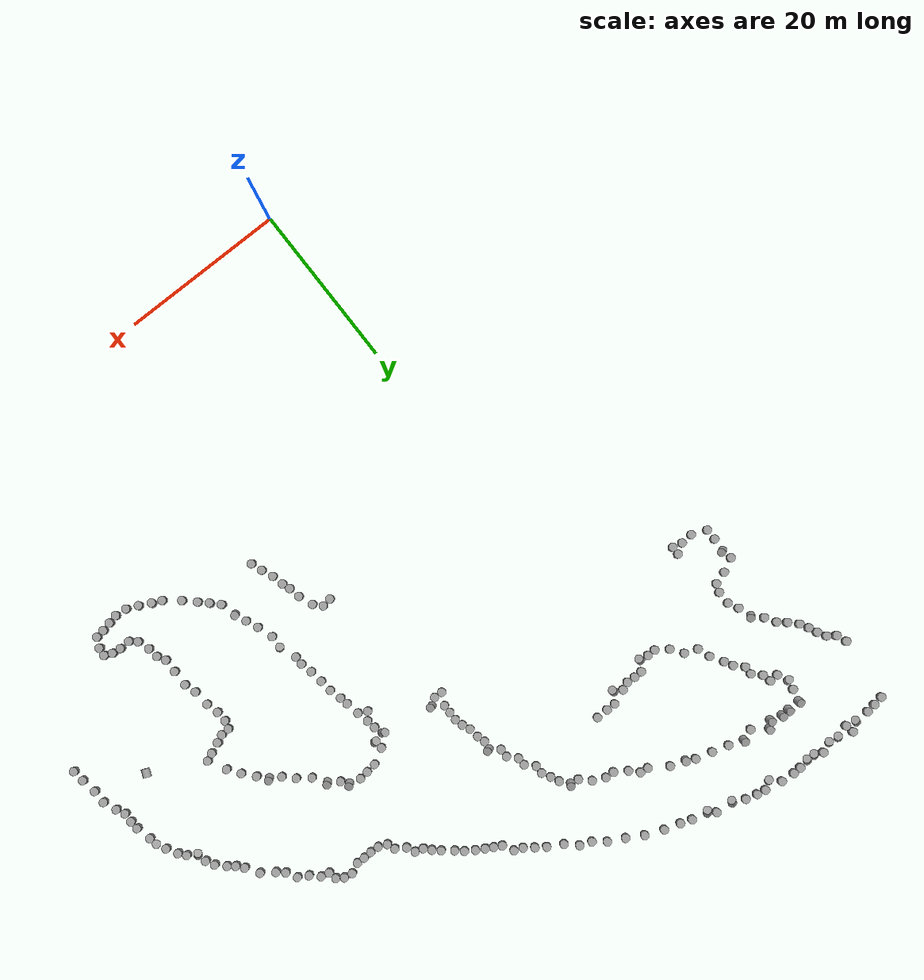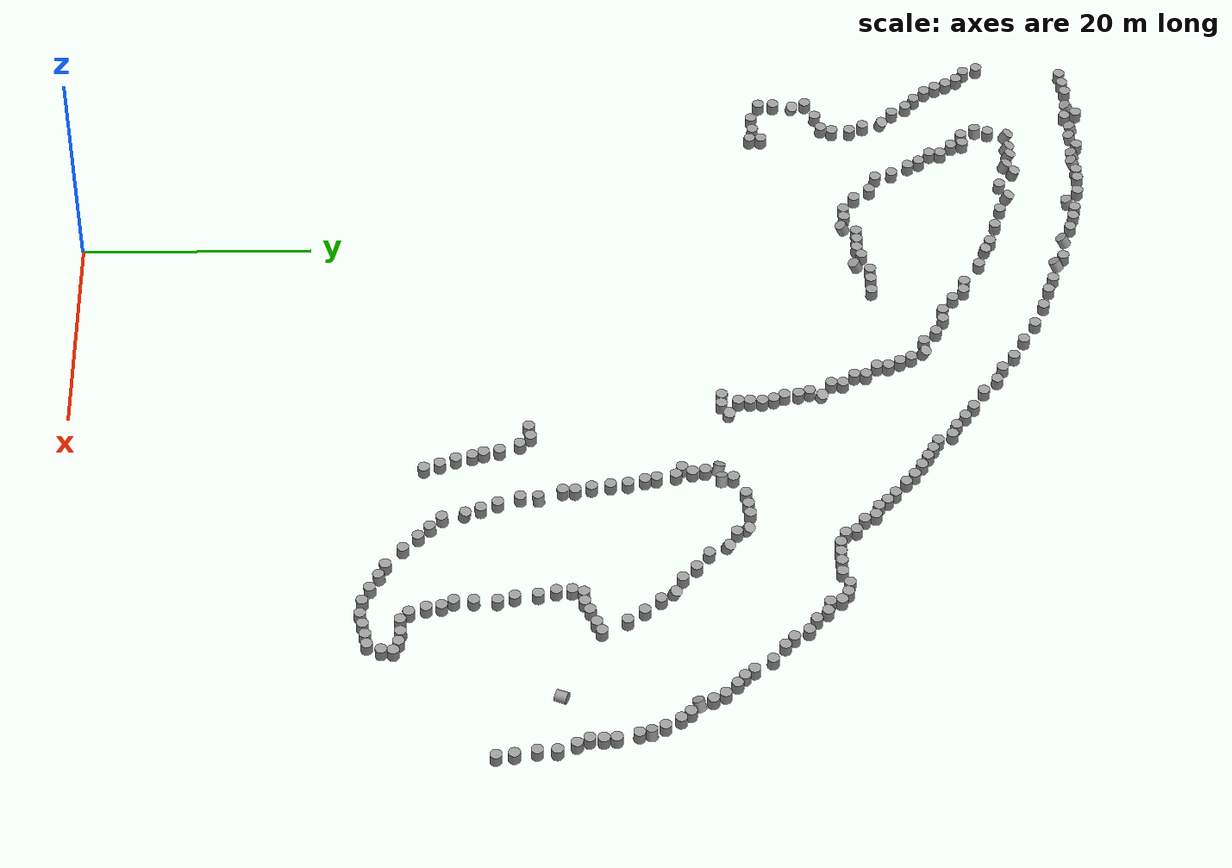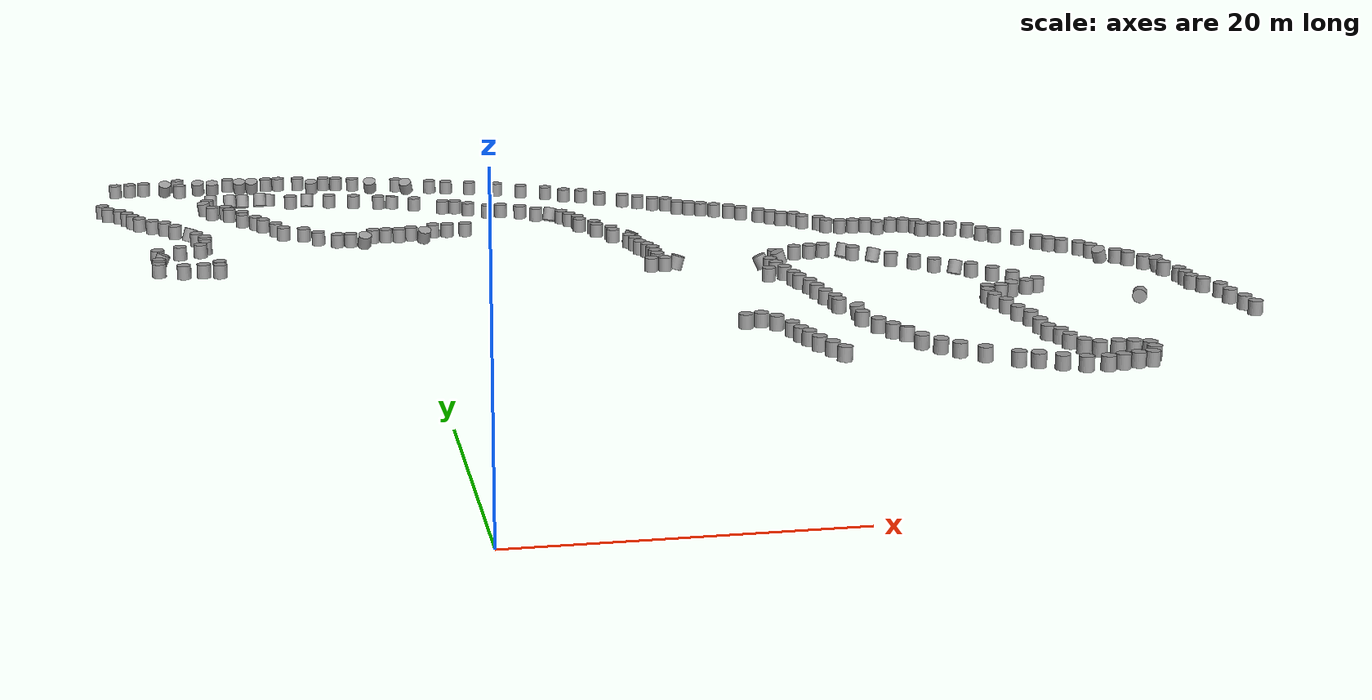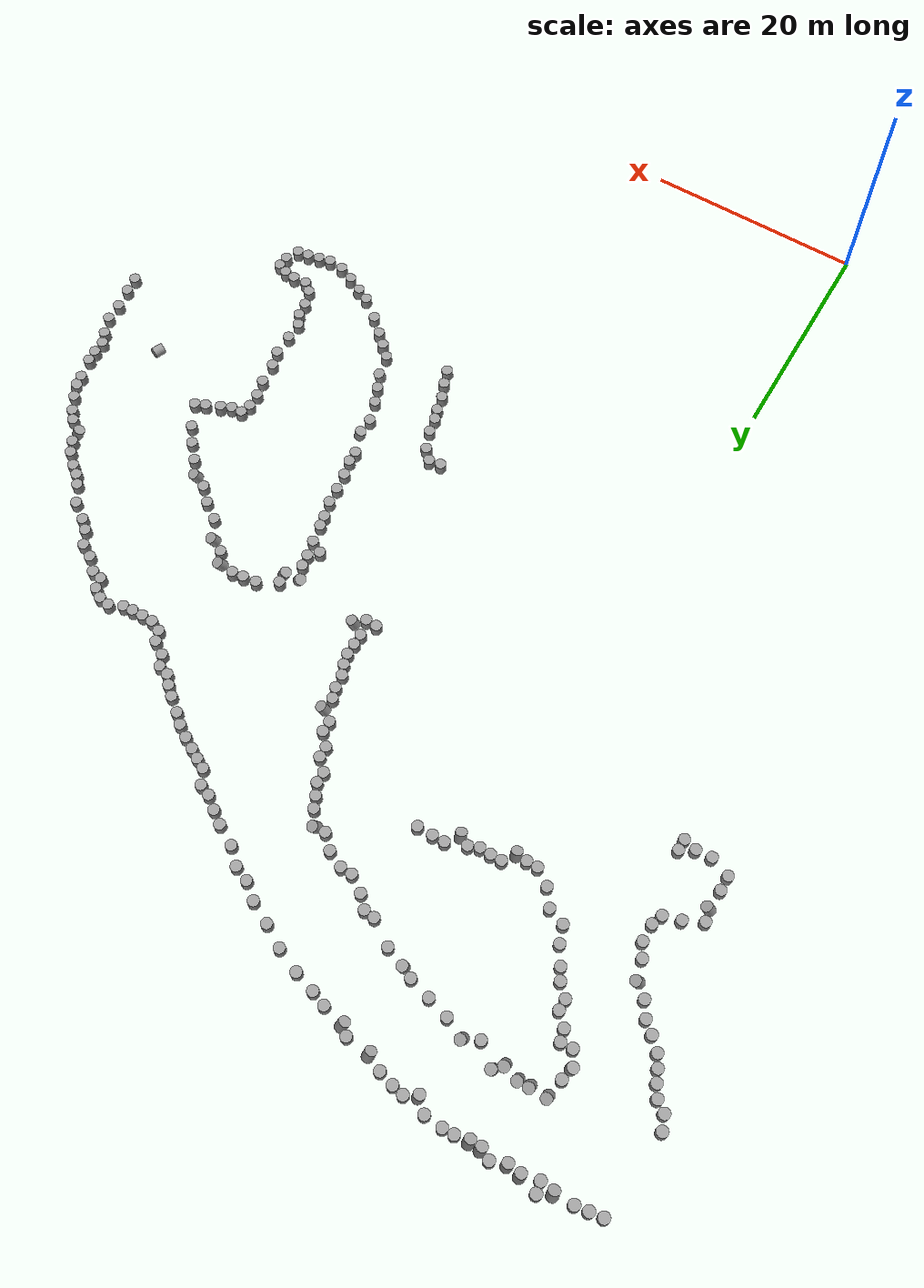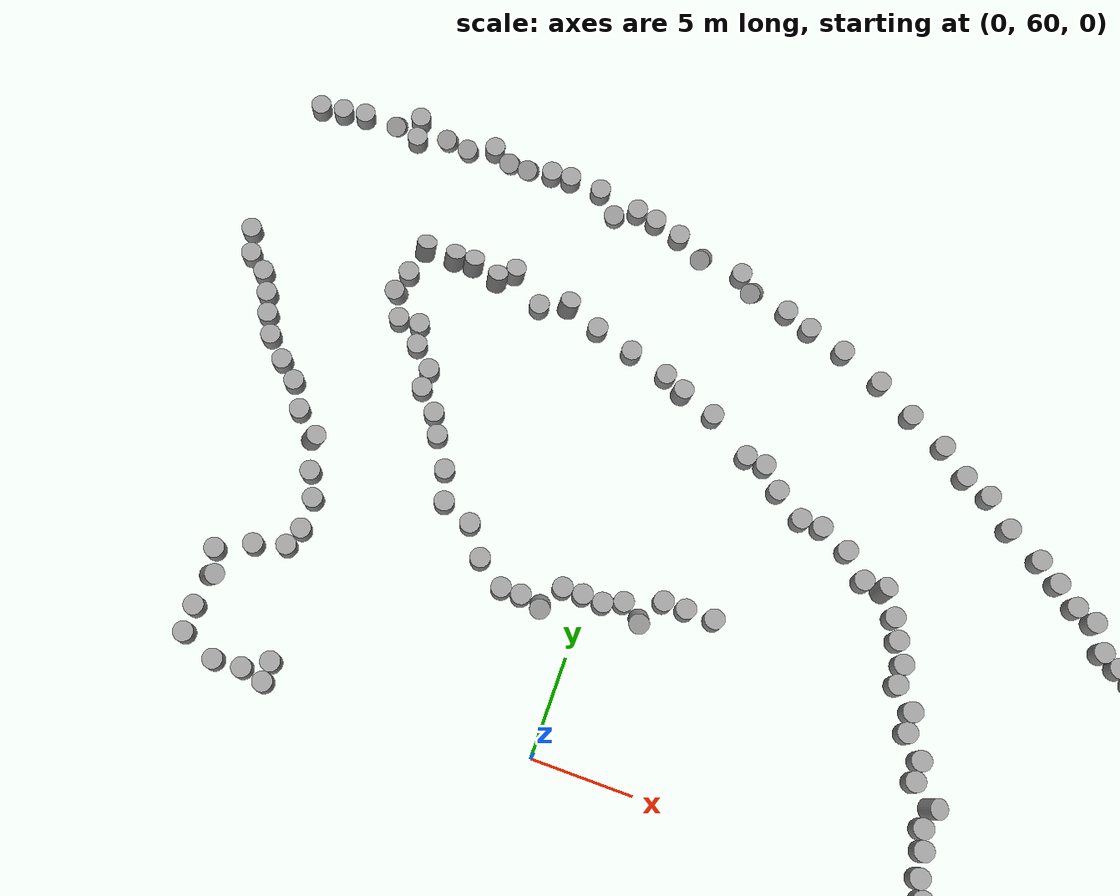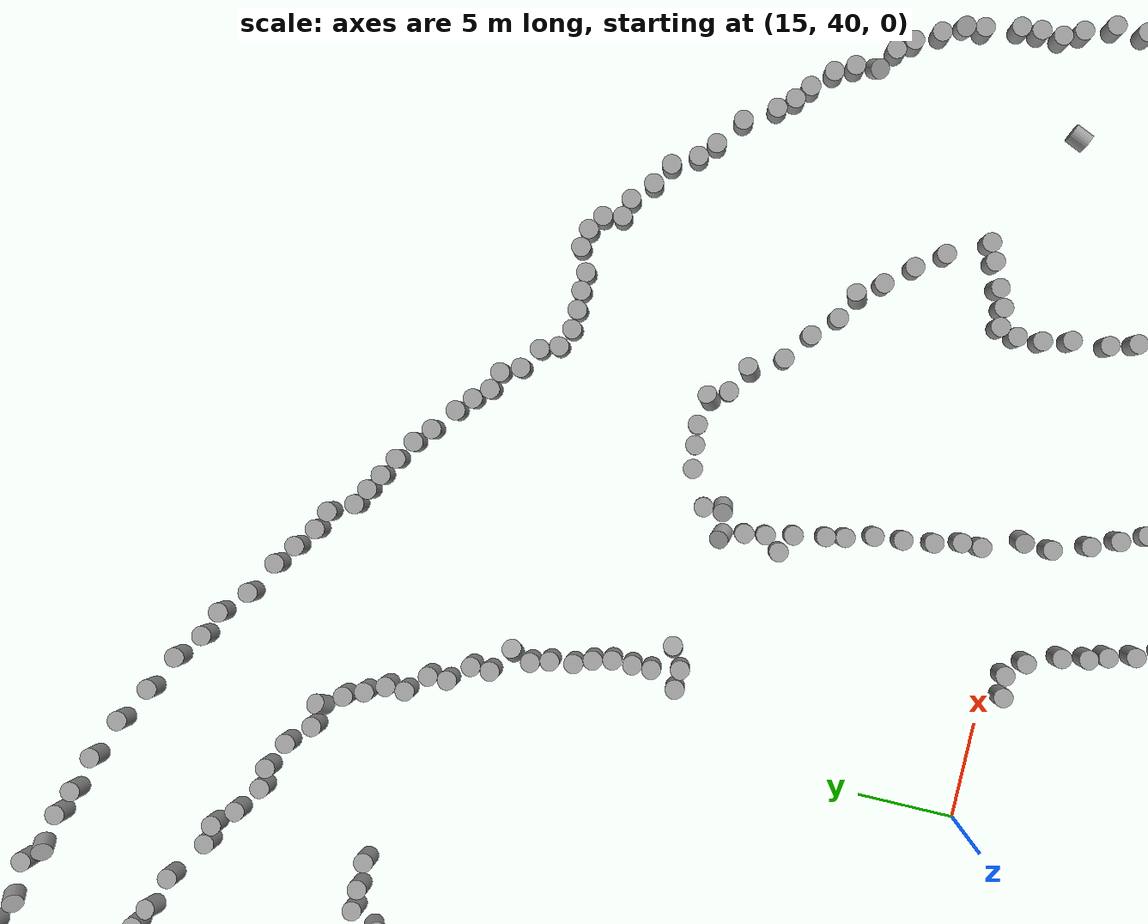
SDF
<sdf version="1.7">
 <world name="default">
  <gravity>0 0 -9.8</gravity>
  <magnetic_field>6e-06 2.3e-05 -4.2e-05</magnetic_field>
  <atmosphere type="adiabatic"/>
  <physics type="ode">
   <max_step_size>0.001</max_step_size>
   <real_time_factor>1</real_time_factor>
   <real_time_update_rate>1000</real_time_update_rate>
  </physics>
  <scene><ambient>0.4 0.4 0.4 1</ambient><background>0.7 0.7 0.7 1</background><shadows>1</shadows></scene>
  <light name="sun" type="directional">
   <pose>0 0 10 0 -0 0</pose>
   <diffuse>0.8 0.8 0.8 1</diffuse>
   <specular>0.2 0.2 0.2 1</specular>
   <attenuation>
    <range>1000</range>
    <constant>0.9</constant>
    <linear>0.01</linear>
    <quadratic>0.001</quadratic>
   </attenuation>
   <direction>-0.5 0.1 -0.9</direction>
   <spot><inner_angle>0</inner_angle><outer_angle>0</outer_angle><falloff>0</falloff></spot>
  </light>
  <spherical_coordinates>
   <surface_model>EARTH_WGS84</surface_model>
   <latitude_deg>0</latitude_deg>
   <longitude_deg>0</longitude_deg>
   <elevation>0</elevation>
   <heading_deg>0</heading_deg>
  </spherical_coordinates>
  <plugin name="gazebo_occupancy_map" filename="libgazebo_2Dmap_plugin.so">
   <map_resolution>0.1</map_resolution>
   <map_height>0.3</map_height>
   <map_size_x>500</map_size_x>
   <map_size_y>500</map_size_y>
   <init_robot_x>0</init_robot_x>
   <init_robot_y>0</init_robot_y>
  </plugin>
  <model name="unit_cylinder">
   <pose>10.9815 74.3057 0.451272 -0.000182 0.00012 -0.00063</pose>
   <link name="link">
    <inertial>
     <mass>1</mass>
     <inertia><ixx>0.145833</ixx><ixy>0</ixy><ixz>0</ixz><iyy>0.145833</iyy><iyz>0</iyz><izz>0.125</izz></inertia>
    </inertial>
    <collision name="collision">
     <geometry><cylinder><radius>0.5</radius><length>1</length></cylinder></geometry>
    </collision>
    <visual name="visual">
     <geometry><cylinder><radius>0.5</radius><length>1</length></cylinder></geometry>
     <material>
      <script><name>Gazebo/Grey</name><uri>file://media/materials/scripts/gazebo.material</uri></script>
     </material>
    </visual>
   </link>
  </model>
  <model name="unit_cylinder_clone_0">
   <pose>12.1286 73.1952 0.453246 -0.005848 0.001541 -0.314889</pose>
   <link name="link">
    <inertial>
     <mass>1</mass>
     <inertia><ixx>0.145833</ixx><ixy>0</ixy><ixz>0</ixz><iyy>0.145833</iyy><iyz>0</iyz><izz>0.125</izz></inertia>
    </inertial>
    <collision name="collision">
     <geometry><cylinder><radius>0.5</radius><length>1</length></cylinder></geometry>
    </collision>
    <visual name="visual">
     <geometry><cylinder><radius>0.5</radius><length>1</length></cylinder></geometry>
     <material>
      <script><name>Gazebo/Grey</name><uri>file://media/materials/scripts/gazebo.material</uri></script>
     </material>
    </visual>
   </link>
  </model>
  <model name="unit_cylinder_clone_1">
   <pose>13.2056 73.1553 0.399914 -0.325351 0.200787 -0.038615</pose>
   <link name="link">
    <inertial>
     <mass>1</mass>
     <inertia><ixx>0.145833</ixx><ixy>0</ixy><ixz>0</ixz><iyy>0.145833</iyy><iyz>0</iyz><izz>0.125</izz></inertia>
    </inertial>
    <collision name="collision">
     <geometry><cylinder><radius>0.5</radius><length>1</length></cylinder></geometry>
    </collision>
    <visual name="visual">
     <geometry><cylinder><radius>0.5</radius><length>1</length></cylinder></geometry>
     <material>
      <script><name>Gazebo/Grey</name><uri>file://media/materials/scripts/gazebo.material</uri></script>
     </material>
    </visual>
   </link>
  </model>
  <model name="unit_cylinder_clone_2">
   <pose>14.0002 72.0002 0.451291 -6.3e-05 0.000114 0.001883</pose>
   <link name="link">
    <inertial>
     <mass>1</mass>
     <inertia><ixx>0.145833</ixx><ixy>0</ixy><ixz>0</ixz><iyy>0.145833</iyy><iyz>0</iyz><izz>0.125</izz></inertia>
    </inertial>
    <collision name="collision">
     <geometry><cylinder><radius>0.5</radius><length>1</length></cylinder></geometry>
    </collision>
    <visual name="visual">
     <geometry><cylinder><radius>0.5</radius><length>1</length></cylinder></geometry>
     <material>
      <script><name>Gazebo/Grey</name><uri>file://media/materials/scripts/gazebo.material</uri></script>
     </material>
    </visual>
   </link>
  </model>
  <model name="unit_cylinder_clone_3">
   <pose>14.4645 70.9999 0.45129 -1e-06 1e-05 -6e-06</pose>
   <link name="link">
    <inertial>
     <mass>1</mass>
     <inertia><ixx>0.145833</ixx><ixy>0</ixy><ixz>0</ixz><iyy>0.145833</iyy><iyz>0</iyz><izz>0.125</izz></inertia>
    </inertial>
    <collision name="collision">
     <geometry><cylinder><radius>0.5</radius><length>1</length></cylinder></geometry>
    </collision>
    <visual name="visual">
     <geometry><cylinder><radius>0.5</radius><length>1</length></cylinder></geometry>
     <material>
      <script><name>Gazebo/Grey</name><uri>file://media/materials/scripts/gazebo.material</uri></script>
     </material>
    </visual>
   </link>
  </model>
  <model name="unit_cylinder_clone_4">
   <pose>14.9998 69.9998 0.451286 -3e-06 -4e-06 -0.000215</pose>
   <link name="link">
    <inertial>
     <mass>1</mass>
     <inertia><ixx>0.145833</ixx><ixy>0</ixy><ixz>0</ixz><iyy>0.145833</iyy><iyz>0</iyz><izz>0.125</izz></inertia>
    </inertial>
    <collision name="collision">
     <geometry><cylinder><radius>0.5</radius><length>1</length></cylinder></geometry>
    </collision>
    <visual name="visual">
     <geometry><cylinder><radius>0.5</radius><length>1</length></cylinder></geometry>
     <material>
      <script><name>Gazebo/Grey</name><uri>file://media/materials/scripts/gazebo.material</uri></script>
     </material>
    </visual>
   </link>
  </model>
  <model name="unit_cylinder_clone_5">
   <pose>15.0001 68.9998 0.451281 1e-06 -7e-06 0.000205</pose>
   <link name="link">
    <inertial>
     <mass>1</mass>
     <inertia><ixx>0.145833</ixx><ixy>0</ixy><ixz>0</ixz><iyy>0.145833</iyy><iyz>0</iyz><izz>0.125</izz></inertia>
    </inertial>
    <collision name="collision">
     <geometry><cylinder><radius>0.5</radius><length>1</length></cylinder></geometry>
    </collision>
    <visual name="visual">
     <geometry><cylinder><radius>0.5</radius><length>1</length></cylinder></geometry>
     <material>
      <script><name>Gazebo/Grey</name><uri>file://media/materials/scripts/gazebo.material</uri></script>
     </material>
    </visual>
   </link>
  </model>
  <model name="unit_cylinder_clone_6">
   <pose>16.0073 68.0187 0.451294 1e-06 -1.5e-05 0.021599</pose>
   <link name="link">
    <inertial>
     <mass>1</mass>
     <inertia><ixx>0.145833</ixx><ixy>0</ixy><ixz>0</ixz><iyy>0.145833</iyy><iyz>0</iyz><izz>0.125</izz></inertia>
    </inertial>
    <collision name="collision">
     <geometry><cylinder><radius>0.5</radius><length>1</length></cylinder></geometry>
    </collision>
    <visual name="visual">
     <geometry><cylinder><radius>0.5</radius><length>1</length></cylinder></geometry>
     <material>
      <script><name>Gazebo/Grey</name><uri>file://media/materials/scripts/gazebo.material</uri></script>
     </material>
    </visual>
   </link>
  </model>
  <model name="unit_cylinder_clone_7">
   <pose>16.0394 67.0187 0.451285 1e-06 -6e-06 0.005178</pose>
   <link name="link">
    <inertial>
     <mass>1</mass>
     <inertia><ixx>0.145833</ixx><ixy>0</ixy><ixz>0</ixz><iyy>0.145833</iyy><iyz>0</iyz><izz>0.125</izz></inertia>
    </inertial>
    <collision name="collision">
     <geometry><cylinder><radius>0.5</radius><length>1</length></cylinder></geometry>
    </collision>
    <visual name="visual">
     <geometry><cylinder><radius>0.5</radius><length>1</length></cylinder></geometry>
     <material>
      <script><name>Gazebo/Grey</name><uri>file://media/materials/scripts/gazebo.material</uri></script>
     </material>
    </visual>
   </link>
  </model>
  <model name="unit_cylinder_clone_8">
   <pose>16.9989 66.0019 0.452892 -0.001909 -0.00089 -0.000228</pose>
   <link name="link">
    <inertial>
     <mass>1</mass>
     <inertia><ixx>0.145833</ixx><ixy>0</ixy><ixz>0</ixz><iyy>0.145833</iyy><iyz>0</iyz><izz>0.125</izz></inertia>
    </inertial>
    <collision name="collision">
     <geometry><cylinder><radius>0.5</radius><length>1</length></cylinder></geometry>
    </collision>
    <visual name="visual">
     <geometry><cylinder><radius>0.5</radius><length>1</length></cylinder></geometry>
     <material>
      <script><name>Gazebo/Grey</name><uri>file://media/materials/scripts/gazebo.material</uri></script>
     </material>
    </visual>
   </link>
  </model>
  <model name="unit_cylinder_clone_11">
   <pose>18.362 60.9371 0.451444 -0.000161 0.00036 -0.029223</pose>
   <link name="link">
    <inertial>
     <mass>1</mass>
     <inertia><ixx>0.145833</ixx><ixy>0</ixy><ixz>0</ixz><iyy>0.145833</iyy><iyz>0</iyz><izz>0.125</izz></inertia>
    </inertial>
    <collision name="collision">
     <geometry><cylinder><radius>0.5</radius><length>1</length></cylinder></geometry>
    </collision>
    <visual name="visual">
     <geometry><cylinder><radius>0.5</radius><length>1</length></cylinder></geometry>
     <material>
      <script><name>Gazebo/Grey</name><uri>file://media/materials/scripts/gazebo.material</uri></script>
     </material>
    </visual>
   </link>
  </model>
  <model name="unit_cylinder_clone_12">
   <pose>18.7639 60.0214 0.451308 3.2e-05 -6.5e-05 0.05836</pose>
   <link name="link">
    <inertial>
     <mass>1</mass>
     <inertia><ixx>0.145833</ixx><ixy>0</ixy><ixz>0</ixz><iyy>0.145833</iyy><iyz>0</iyz><izz>0.125</izz></inertia>
    </inertial>
    <collision name="collision">
     <geometry><cylinder><radius>0.5</radius><length>1</length></cylinder></geometry>
    </collision>
    <visual name="visual">
     <geometry><cylinder><radius>0.5</radius><length>1</length></cylinder></geometry>
     <material>
      <script><name>Gazebo/Grey</name><uri>file://media/materials/scripts/gazebo.material</uri></script>
     </material>
    </visual>
   </link>
  </model>
  <model name="unit_cylinder_clone_13">
   <pose>19.0089 59.0467 0.451293 2.5e-05 -0.000108 0.000934</pose>
   <link name="link">
    <inertial>
     <mass>1</mass>
     <inertia><ixx>0.145833</ixx><ixy>0</ixy><ixz>0</ixz><iyy>0.145833</iyy><iyz>0</iyz><izz>0.125</izz></inertia>
    </inertial>
    <collision name="collision">
     <geometry><cylinder><radius>0.5</radius><length>1</length></cylinder></geometry>
    </collision>
    <visual name="visual">
     <geometry><cylinder><radius>0.5</radius><length>1</length></cylinder></geometry>
     <material>
      <script><name>Gazebo/Grey</name><uri>file://media/materials/scripts/gazebo.material</uri></script>
     </material>
    </visual>
   </link>
  </model>
  <model name="unit_cylinder_clone_14">
   <pose>19.0002 57.9997 0.451442 -6e-06 0.000332 -0.000485</pose>
   <link name="link">
    <inertial>
     <mass>1</mass>
     <inertia><ixx>0.145833</ixx><ixy>0</ixy><ixz>0</ixz><iyy>0.145833</iyy><iyz>0</iyz><izz>0.125</izz></inertia>
    </inertial>
    <collision name="collision">
     <geometry><cylinder><radius>0.5</radius><length>1</length></cylinder></geometry>
    </collision>
    <visual name="visual">
     <geometry><cylinder><radius>0.5</radius><length>1</length></cylinder></geometry>
     <material>
      <script><name>Gazebo/Grey</name><uri>file://media/materials/scripts/gazebo.material</uri></script>
     </material>
    </visual>
   </link>
  </model>
  <model name="unit_cylinder_clone_15">
   <pose>19.0001 56.9993 0.450902 0.000544 0.000122 -0.000184</pose>
   <link name="link">
    <inertial>
     <mass>1</mass>
     <inertia><ixx>0.145833</ixx><ixy>0</ixy><ixz>0</ixz><iyy>0.145833</iyy><iyz>0</iyz><izz>0.125</izz></inertia>
    </inertial>
    <collision name="collision">
     <geometry><cylinder><radius>0.5</radius><length>1</length></cylinder></geometry>
    </collision>
    <visual name="visual">
     <geometry><cylinder><radius>0.5</radius><length>1</length></cylinder></geometry>
     <material>
      <script><name>Gazebo/Grey</name><uri>file://media/materials/scripts/gazebo.material</uri></script>
     </material>
    </visual>
   </link>
  </model>
  <model name="unit_cylinder_clone_16">
   <pose>20.2887 56.1657 0.370309 -0.101618 0.266413 -0.132281</pose>
   <link name="link">
    <inertial>
     <mass>1</mass>
     <inertia><ixx>0.145833</ixx><ixy>0</ixy><ixz>0</ixz><iyy>0.145833</iyy><iyz>0</iyz><izz>0.125</izz></inertia>
    </inertial>
    <collision name="collision">
     <geometry><cylinder><radius>0.5</radius><length>1</length></cylinder></geometry>
    </collision>
    <visual name="visual">
     <geometry><cylinder><radius>0.5</radius><length>1</length></cylinder></geometry>
     <material>
      <script><name>Gazebo/Grey</name><uri>file://media/materials/scripts/gazebo.material</uri></script>
     </material>
    </visual>
   </link>
  </model>
  <model name="unit_cylinder_clone_17">
   <pose>19.3175 55.5652 0.451074 -0.001404 -0.000209 0.07838</pose>
   <link name="link">
    <inertial>
     <mass>1</mass>
     <inertia><ixx>0.145833</ixx><ixy>0</ixy><ixz>0</ixz><iyy>0.145833</iyy><iyz>0</iyz><izz>0.125</izz></inertia>
    </inertial>
    <collision name="collision">
     <geometry><cylinder><radius>0.5</radius><length>1</length></cylinder></geometry>
    </collision>
    <visual name="visual">
     <geometry><cylinder><radius>0.5</radius><length>1</length></cylinder></geometry>
     <material>
      <script><name>Gazebo/Grey</name><uri>file://media/materials/scripts/gazebo.material</uri></script>
     </material>
    </visual>
   </link>
  </model>
  <model name="unit_cylinder_clone_18">
   <pose>18.2992 55.5987 0.450932 -0.000832 -0.000215 -0.020841</pose>
   <link name="link">
    <inertial>
     <mass>1</mass>
     <inertia><ixx>0.145833</ixx><ixy>0</ixy><ixz>0</ixz><iyy>0.145833</iyy><iyz>0</iyz><izz>0.125</izz></inertia>
    </inertial>
    <collision name="collision">
     <geometry><cylinder><radius>0.5</radius><length>1</length></cylinder></geometry>
    </collision>
    <visual name="visual">
     <geometry><cylinder><radius>0.5</radius><length>1</length></cylinder></geometry>
     <material>
      <script><name>Gazebo/Grey</name><uri>file://media/materials/scripts/gazebo.material</uri></script>
     </material>
    </visual>
   </link>
  </model>
  <model name="unit_cylinder_clone">
   <pose>18.2082 62.1497 0.451365 0.000171 1.6e-05 0.137302</pose>
   <link name="link">
    <inertial>
     <mass>1</mass>
     <inertia><ixx>0.145833</ixx><ixy>0</ixy><ixz>0</ixz><iyy>0.145833</iyy><iyz>0</iyz><izz>0.125</izz></inertia>
    </inertial>
    <collision name="collision">
     <geometry><cylinder><radius>0.5</radius><length>1</length></cylinder></geometry>
    </collision>
    <visual name="visual">
     <geometry><cylinder><radius>0.5</radius><length>1</length></cylinder></geometry>
     <material>
      <script><name>Gazebo/Grey</name><uri>file://media/materials/scripts/gazebo.material</uri></script>
     </material>
    </visual>
   </link>
  </model>
  <model name="unit_cylinder_clone_9">
   <pose>17.9166 63.1062 0.452393 0.000739 -0.001652 -0.03629</pose>
   <link name="link">
    <inertial>
     <mass>1</mass>
     <inertia><ixx>0.145833</ixx><ixy>0</ixy><ixz>0</ixz><iyy>0.145833</iyy><iyz>0</iyz><izz>0.125</izz></inertia>
    </inertial>
    <collision name="collision">
     <geometry><cylinder><radius>0.5</radius><length>1</length></cylinder></geometry>
    </collision>
    <visual name="visual">
     <geometry><cylinder><radius>0.5</radius><length>1</length></cylinder></geometry>
     <material>
      <script><name>Gazebo/Grey</name><uri>file://media/materials/scripts/gazebo.material</uri></script>
     </material>
    </visual>
   </link>
  </model>
  <model name="unit_cylinder_clone_10">
   <pose>18.1963 64.147 0.398262 -0.158294 0.340891 -0.163728</pose>
   <link name="link">
    <inertial>
     <mass>1</mass>
     <inertia><ixx>0.145833</ixx><ixy>0</ixy><ixz>0</ixz><iyy>0.145833</iyy><iyz>0</iyz><izz>0.125</izz></inertia>
    </inertial>
    <collision name="collision">
     <geometry><cylinder><radius>0.5</radius><length>1</length></cylinder></geometry>
    </collision>
    <visual name="visual">
     <geometry><cylinder><radius>0.5</radius><length>1</length></cylinder></geometry>
     <material>
      <script><name>Gazebo/Grey</name><uri>file://media/materials/scripts/gazebo.material</uri></script>
     </material>
    </visual>
   </link>
  </model>
  <model name="unit_cylinder_clone_19">
   <pose>16.9993 65.0019 0.45479 -0.001906 -0.000899 0.000167</pose>
   <link name="link">
    <inertial>
     <mass>1</mass>
     <inertia><ixx>0.145833</ixx><ixy>0</ixy><ixz>0</ixz><iyy>0.145833</iyy><iyz>0</iyz><izz>0.125</izz></inertia>
    </inertial>
    <collision name="collision">
     <geometry><cylinder><radius>0.5</radius><length>1</length></cylinder></geometry>
    </collision>
    <visual name="visual">
     <geometry><cylinder><radius>0.5</radius><length>1</length></cylinder></geometry>
     <material>
      <script><name>Gazebo/Grey</name><uri>file://media/materials/scripts/gazebo.material</uri></script>
     </material>
    </visual>
   </link>
  </model>
  <model name="unit_cylinder_clone_20">
   <pose>29.5714 69.8204 0.452522 0.003212 -0.003102 -0.001121</pose>
   <link name="link">
    <inertial>
     <mass>1</mass>
     <inertia><ixx>0.145833</ixx><ixy>0</ixy><ixz>0</ixz><iyy>0.145833</iyy><iyz>0</iyz><izz>0.125</izz></inertia>
    </inertial>
    <collision name="collision">
     <geometry><cylinder><radius>0.5</radius><length>1</length></cylinder></geometry>
    </collision>
    <visual name="visual">
     <geometry><cylinder><radius>0.5</radius><length>1</length></cylinder></geometry>
     <material>
      <script><name>Gazebo/Grey</name><uri>file://media/materials/scripts/gazebo.material</uri></script>
     </material>
    </visual>
   </link>
  </model>
  <model name="unit_cylinder_clone_21">
   <pose>30.3704 69.1072 0.452744 0.003399 -0.003022 -0.042951</pose>
   <link name="link">
    <inertial>
     <mass>1</mass>
     <inertia><ixx>0.145833</ixx><ixy>0</ixy><ixz>0</ixz><iyy>0.145833</iyy><iyz>0</iyz><izz>0.125</izz></inertia>
    </inertial>
    <collision name="collision">
     <geometry><cylinder><radius>0.5</radius><length>1</length></cylinder></geometry>
    </collision>
    <visual name="visual">
     <geometry><cylinder><radius>0.5</radius><length>1</length></cylinder></geometry>
     <material>
      <script><name>Gazebo/Grey</name><uri>file://media/materials/scripts/gazebo.material</uri></script>
     </material>
    </visual>
   </link>
  </model>
  <model name="unit_cylinder_clone_22">
   <pose>31.0426 68.3593 0.452416 0.003112 -0.003236 0.034817</pose>
   <link name="link">
    <inertial>
     <mass>1</mass>
     <inertia><ixx>0.145833</ixx><ixy>0</ixy><ixz>0</ixz><iyy>0.145833</iyy><iyz>0</iyz><izz>0.125</izz></inertia>
    </inertial>
    <collision name="collision">
     <geometry><cylinder><radius>0.5</radius><length>1</length></cylinder></geometry>
    </collision>
    <visual name="visual">
     <geometry><cylinder><radius>0.5</radius><length>1</length></cylinder></geometry>
     <material>
      <script><name>Gazebo/Grey</name><uri>file://media/materials/scripts/gazebo.material</uri></script>
     </material>
    </visual>
   </link>
  </model>
  <model name="unit_cylinder_clone_23">
   <pose>32.0012 68.066 0.454432 0.003884 -0.003444 -0.043961</pose>
   <link name="link">
    <inertial>
     <mass>1</mass>
     <inertia><ixx>0.145833</ixx><ixy>0</ixy><ixz>0</ixz><iyy>0.145833</iyy><iyz>0</iyz><izz>0.125</izz></inertia>
    </inertial>
    <collision name="collision">
     <geometry><cylinder><radius>0.5</radius><length>1</length></cylinder></geometry>
    </collision>
    <visual name="visual">
     <geometry><cylinder><radius>0.5</radius><length>1</length></cylinder></geometry>
     <material>
      <script><name>Gazebo/Grey</name><uri>file://media/materials/scripts/gazebo.material</uri></script>
     </material>
    </visual>
   </link>
  </model>
  <model name="unit_cylinder_clone_24">
   <pose>32.4718 67.0928 0.452826 0.003288 -0.003165 -0.003406</pose>
   <link name="link">
    <inertial>
     <mass>1</mass>
     <inertia><ixx>0.145833</ixx><ixy>0</ixy><ixz>0</ixz><iyy>0.145833</iyy><iyz>0</iyz><izz>0.125</izz></inertia>
    </inertial>
    <collision name="collision">
     <geometry><cylinder><radius>0.5</radius><length>1</length></cylinder></geometry>
    </collision>
    <visual name="visual">
     <geometry><cylinder><radius>0.5</radius><length>1</length></cylinder></geometry>
     <material>
      <script><name>Gazebo/Grey</name><uri>file://media/materials/scripts/gazebo.material</uri></script>
     </material>
    </visual>
   </link>
  </model>
  <model name="unit_cylinder_clone_26">
   <pose>33.9917 65.4361 0.452225 0.003363 -0.002865 0.017191</pose>
   <link name="link">
    <inertial>
     <mass>1</mass>
     <inertia><ixx>0.145833</ixx><ixy>0</ixy><ixz>0</ixz><iyy>0.145833</iyy><iyz>0</iyz><izz>0.125</izz></inertia>
    </inertial>
    <collision name="collision">
     <geometry><cylinder><radius>0.5</radius><length>1</length></cylinder></geometry>
    </collision>
    <visual name="visual">
     <geometry><cylinder><radius>0.5</radius><length>1</length></cylinder></geometry>
     <material>
      <script><name>Gazebo/Grey</name><uri>file://media/materials/scripts/gazebo.material</uri></script>
     </material>
    </visual>
   </link>
  </model>
  <model name="unit_cylinder_clone_27">
   <pose>34.9986 64.9973 0.452847 0.004091 -0.002164 -0.00044</pose>
   <link name="link">
    <inertial>
     <mass>1</mass>
     <inertia><ixx>0.145833</ixx><ixy>0</ixy><ixz>0</ixz><iyy>0.145833</iyy><iyz>0</iyz><izz>0.125</izz></inertia>
    </inertial>
    <collision name="collision">
     <geometry><cylinder><radius>0.5</radius><length>1</length></cylinder></geometry>
    </collision>
    <visual name="visual">
     <geometry><cylinder><radius>0.5</radius><length>1</length></cylinder></geometry>
     <material>
      <script><name>Gazebo/Grey</name><uri>file://media/materials/scripts/gazebo.material</uri></script>
     </material>
    </visual>
   </link>
  </model>
  <model name="unit_cylinder_clone_25">
   <pose>33.6311 66.3688 0.454 0.00369 -0.003657 0.01249</pose>
   <link name="link">
    <inertial>
     <mass>1</mass>
     <inertia><ixx>0.145833</ixx><ixy>0</ixy><ixz>0</ixz><iyy>0.145833</iyy><iyz>0</iyz><izz>0.125</izz></inertia>
    </inertial>
    <collision name="collision">
     <geometry><cylinder><radius>0.5</radius><length>1</length></cylinder></geometry>
    </collision>
    <visual name="visual">
     <geometry><cylinder><radius>0.5</radius><length>1</length></cylinder></geometry>
     <material>
      <script><name>Gazebo/Grey</name><uri>file://media/materials/scripts/gazebo.material</uri></script>
     </material>
    </visual>
   </link>
  </model>
  <model name="unit_cylinder_clone_29">
   <pose>29.4853 57.321 0.450007 1.4e-05 -1e-06 -0.030897</pose>
   <link name="link">
    <inertial>
     <mass>1</mass>
     <inertia><ixx>0.145833</ixx><ixy>0</ixy><ixz>0</ixz><iyy>0.145833</iyy><iyz>0</iyz><izz>0.125</izz></inertia>
    </inertial>
    <collision name="collision">
     <geometry><cylinder><radius>0.5</radius><length>1</length></cylinder></geometry>
    </collision>
    <visual name="visual">
     <geometry><cylinder><radius>0.5</radius><length>1</length></cylinder></geometry>
     <material>
      <script><name>Gazebo/Grey</name><uri>file://media/materials/scripts/gazebo.material</uri></script>
     </material>
    </visual>
   </link>
  </model>
  <model name="unit_cylinder_clone_30">
   <pose>30.6933 57.4847 0.450019 1.7e-05 -1.2e-05 0.04423</pose>
   <link name="link">
    <inertial>
     <mass>1</mass>
     <inertia><ixx>0.145833</ixx><ixy>0</ixy><ixz>0</ixz><iyy>0.145833</iyy><iyz>0</iyz><izz>0.125</izz></inertia>
    </inertial>
    <collision name="collision">
     <geometry><cylinder><radius>0.5</radius><length>1</length></cylinder></geometry>
    </collision>
    <visual name="visual">
     <geometry><cylinder><radius>0.5</radius><length>1</length></cylinder></geometry>
     <material>
      <script><name>Gazebo/Grey</name><uri>file://media/materials/scripts/gazebo.material</uri></script>
     </material>
    </visual>
   </link>
  </model>
  <model name="unit_cylinder_clone_31">
   <pose>31.7457 57.6018 0.450033 1.2e-05 -1.2e-05 0.013076</pose>
   <link name="link">
    <inertial>
     <mass>1</mass>
     <inertia><ixx>0.145833</ixx><ixy>0</ixy><ixz>0</ixz><iyy>0.145833</iyy><iyz>0</iyz><izz>0.125</izz></inertia>
    </inertial>
    <collision name="collision">
     <geometry><cylinder><radius>0.5</radius><length>1</length></cylinder></geometry>
    </collision>
    <visual name="visual">
     <geometry><cylinder><radius>0.5</radius><length>1</length></cylinder></geometry>
     <material>
      <script><name>Gazebo/Grey</name><uri>file://media/materials/scripts/gazebo.material</uri></script>
     </material>
    </visual>
   </link>
  </model>
  <model name="unit_cylinder_clone_33">
   <pose>27.7032 56.3259 0.449997 1.9e-05 1.5e-05 -0.055652</pose>
   <link name="link">
    <inertial>
     <mass>1</mass>
     <inertia><ixx>0.145833</ixx><ixy>0</ixy><ixz>0</ixz><iyy>0.145833</iyy><iyz>0</iyz><izz>0.125</izz></inertia>
    </inertial>
    <collision name="collision">
     <geometry><cylinder><radius>0.5</radius><length>1</length></cylinder></geometry>
    </collision>
    <visual name="visual">
     <geometry><cylinder><radius>0.5</radius><length>1</length></cylinder></geometry>
     <material>
      <script><name>Gazebo/Grey</name><uri>file://media/materials/scripts/gazebo.material</uri></script>
     </material>
    </visual>
   </link>
  </model>
  <model name="unit_cylinder_clone_34">
   <pose>27.8324 55.3338 0.592086 0.034403 -0.351762 0.001319</pose>
   <link name="link">
    <inertial>
     <mass>1</mass>
     <inertia><ixx>0.145833</ixx><ixy>0</ixy><ixz>0</ixz><iyy>0.145833</iyy><iyz>0</iyz><izz>0.125</izz></inertia>
    </inertial>
    <collision name="collision">
     <geometry><cylinder><radius>0.5</radius><length>1</length></cylinder></geometry>
    </collision>
    <visual name="visual">
     <geometry><cylinder><radius>0.5</radius><length>1</length></cylinder></geometry>
     <material>
      <script><name>Gazebo/Grey</name><uri>file://media/materials/scripts/gazebo.material</uri></script>
     </material>
    </visual>
   </link>
  </model>
  <model name="unit_cylinder_clone_35">
   <pose>26.455 55.1006 0.417581 -0.20012 -0.405202 0.030446</pose>
   <link name="link">
    <inertial>
     <mass>1</mass>
     <inertia><ixx>0.145833</ixx><ixy>0</ixy><ixz>0</ixz><iyy>0.145833</iyy><iyz>0</iyz><izz>0.125</izz></inertia>
    </inertial>
    <collision name="collision">
     <geometry><cylinder><radius>0.5</radius><length>1</length></cylinder></geometry>
    </collision>
    <visual name="visual">
     <geometry><cylinder><radius>0.5</radius><length>1</length></cylinder></geometry>
     <material>
      <script><name>Gazebo/Grey</name><uri>file://media/materials/scripts/gazebo.material</uri></script>
     </material>
    </visual>
   </link>
  </model>
  <model name="unit_cylinder_clone_36">
   <pose>26.8684 53.9843 0.449993 8e-06 3.8e-05 0.403169</pose>
   <link name="link">
    <inertial>
     <mass>1</mass>
     <inertia><ixx>0.145833</ixx><ixy>0</ixy><ixz>0</ixz><iyy>0.145833</iyy><iyz>0</iyz><izz>0.125</izz></inertia>
    </inertial>
    <collision name="collision">
     <geometry><cylinder><radius>0.5</radius><length>1</length></cylinder></geometry>
    </collision>
    <visual name="visual">
     <geometry><cylinder><radius>0.5</radius><length>1</length></cylinder></geometry>
     <material>
      <script><name>Gazebo/Grey</name><uri>file://media/materials/scripts/gazebo.material</uri></script>
     </material>
    </visual>
   </link>
  </model>
  <model name="unit_cylinder_clone_37">
   <pose>27.0472 52.9007 0.450003 1.2e-05 -1.4e-05 -0.501799</pose>
   <link name="link">
    <inertial>
     <mass>1</mass>
     <inertia><ixx>0.145833</ixx><ixy>0</ixy><ixz>0</ixz><iyy>0.145833</iyy><iyz>0</iyz><izz>0.125</izz></inertia>
    </inertial>
    <collision name="collision">
     <geometry><cylinder><radius>0.5</radius><length>1</length></cylinder></geometry>
    </collision>
    <visual name="visual">
     <geometry><cylinder><radius>0.5</radius><length>1</length></cylinder></geometry>
     <material>
      <script><name>Gazebo/Grey</name><uri>file://media/materials/scripts/gazebo.material</uri></script>
     </material>
    </visual>
   </link>
  </model>
  <model name="unit_cylinder_clone_28">
   <pose>26.3433 52.0317 0.249998 -5e-06 -4e-06 -0.943686</pose>
   <link name="link">
    <inertial>
     <mass>1</mass>
     <inertia><ixx>0.145833</ixx><ixy>0</ixy><ixz>0</ixz><iyy>0.145833</iyy><iyz>0</iyz><izz>0.125</izz></inertia>
    </inertial>
    <collision name="collision">
     <geometry><cylinder><radius>0.5</radius><length>1</length></cylinder></geometry>
    </collision>
    <visual name="visual">
     <geometry><cylinder><radius>0.5</radius><length>1</length></cylinder></geometry>
     <material>
      <script><name>Gazebo/Grey</name><uri>file://media/materials/scripts/gazebo.material</uri></script>
     </material>
    </visual>
   </link>
  </model>
  <model name="unit_cylinder_clone_32">
   <pose>27.3691 51.5078 0.44999 4e-06 2.6e-05 0.385377</pose>
   <link name="link">
    <inertial>
     <mass>1</mass>
     <inertia><ixx>0.145833</ixx><ixy>0</ixy><ixz>0</ixz><iyy>0.145833</iyy><iyz>0</iyz><izz>0.125</izz></inertia>
    </inertial>
    <collision name="collision">
     <geometry><cylinder><radius>0.5</radius><length>1</length></cylinder></geometry>
    </collision>
    <visual name="visual">
     <geometry><cylinder><radius>0.5</radius><length>1</length></cylinder></geometry>
     <material>
      <script><name>Gazebo/Grey</name><uri>file://media/materials/scripts/gazebo.material</uri></script>
     </material>
    </visual>
   </link>
  </model>
  <model name="unit_cylinder_clone_38">
   <pose>27.6751 49.883 0.449987 -5e-06 2.5e-05 -0.007643</pose>
   <link name="link">
    <inertial>
     <mass>1</mass>
     <inertia><ixx>0.145833</ixx><ixy>0</ixy><ixz>0</ixz><iyy>0.145833</iyy><iyz>0</iyz><izz>0.125</izz></inertia>
    </inertial>
    <collision name="collision">
     <geometry><cylinder><radius>0.5</radius><length>1</length></cylinder></geometry>
    </collision>
    <visual name="visual">
     <geometry><cylinder><radius>0.5</radius><length>1</length></cylinder></geometry>
     <material>
      <script><name>Gazebo/Grey</name><uri>file://media/materials/scripts/gazebo.material</uri></script>
     </material>
    </visual>
   </link>
  </model>
  <model name="unit_cylinder_clone_39">
   <pose>27.8675 48.9006 0.449988 -1.5e-05 1.5e-05 -0.005053</pose>
   <link name="link">
    <inertial>
     <mass>1</mass>
     <inertia><ixx>0.145833</ixx><ixy>0</ixy><ixz>0</ixz><iyy>0.145833</iyy><iyz>0</iyz><izz>0.125</izz></inertia>
    </inertial>
    <collision name="collision">
     <geometry><cylinder><radius>0.5</radius><length>1</length></cylinder></geometry>
    </collision>
    <visual name="visual">
     <geometry><cylinder><radius>0.5</radius><length>1</length></cylinder></geometry>
     <material>
      <script><name>Gazebo/Grey</name><uri>file://media/materials/scripts/gazebo.material</uri></script>
     </material>
    </visual>
   </link>
  </model>
  <model name="unit_cylinder_clone_40">
   <pose>28.2706 47.4767 0.449998 -2e-06 6e-06 -0.000437</pose>
   <link name="link">
    <inertial>
     <mass>1</mass>
     <inertia><ixx>0.145833</ixx><ixy>0</ixy><ixz>0</ixz><iyy>0.145833</iyy><iyz>0</iyz><izz>0.125</izz></inertia>
    </inertial>
    <collision name="collision">
     <geometry><cylinder><radius>0.5</radius><length>1</length></cylinder></geometry>
    </collision>
    <visual name="visual">
     <geometry><cylinder><radius>0.5</radius><length>1</length></cylinder></geometry>
     <material>
      <script><name>Gazebo/Grey</name><uri>file://media/materials/scripts/gazebo.material</uri></script>
     </material>
    </visual>
   </link>
  </model>
  <model name="unit_cylinder_clone_41">
   <pose>28.4209 46.0001 0.449995 -5e-06 6e-06 -0.001146</pose>
   <link name="link">
    <inertial>
     <mass>1</mass>
     <inertia><ixx>0.145833</ixx><ixy>0</ixy><ixz>0</ixz><iyy>0.145833</iyy><iyz>0</iyz><izz>0.125</izz></inertia>
    </inertial>
    <collision name="collision">
     <geometry><cylinder><radius>0.5</radius><length>1</length></cylinder></geometry>
    </collision>
    <visual name="visual">
     <geometry><cylinder><radius>0.5</radius><length>1</length></cylinder></geometry>
     <material>
      <script><name>Gazebo/Grey</name><uri>file://media/materials/scripts/gazebo.material</uri></script>
     </material>
    </visual>
   </link>
  </model>
  <model name="unit_cylinder_clone_42">
   <pose>28.6472 44.4234 0.449998 4e-06 6e-06 -0.002847</pose>
   <link name="link">
    <inertial>
     <mass>1</mass>
     <inertia><ixx>0.145833</ixx><ixy>0</ixy><ixz>0</ixz><iyy>0.145833</iyy><iyz>0</iyz><izz>0.125</izz></inertia>
    </inertial>
    <collision name="collision">
     <geometry><cylinder><radius>0.5</radius><length>1</length></cylinder></geometry>
    </collision>
    <visual name="visual">
     <geometry><cylinder><radius>0.5</radius><length>1</length></cylinder></geometry>
     <material>
      <script><name>Gazebo/Grey</name><uri>file://media/materials/scripts/gazebo.material</uri></script>
     </material>
    </visual>
   </link>
  </model>
  <model name="unit_cylinder_clone_43">
   <pose>28.9953 43.0368 0.449997 2e-06 2e-06 -0.000409</pose>
   <link name="link">
    <inertial>
     <mass>1</mass>
     <inertia><ixx>0.145833</ixx><ixy>0</ixy><ixz>0</ixz><iyy>0.145833</iyy><iyz>0</iyz><izz>0.125</izz></inertia>
    </inertial>
    <collision name="collision">
     <geometry><cylinder><radius>0.5</radius><length>1</length></cylinder></geometry>
    </collision>
    <visual name="visual">
     <geometry><cylinder><radius>0.5</radius><length>1</length></cylinder></geometry>
     <material>
      <script><name>Gazebo/Grey</name><uri>file://media/materials/scripts/gazebo.material</uri></script>
     </material>
    </visual>
   </link>
  </model>
  <model name="unit_cylinder_clone_44">
   <pose>28.9999 41.9999 0.449996 -1e-06 -1e-05 -0.000407</pose>
   <link name="link">
    <inertial>
     <mass>1</mass>
     <inertia><ixx>0.145833</ixx><ixy>0</ixy><ixz>0</ixz><iyy>0.145833</iyy><iyz>0</iyz><izz>0.125</izz></inertia>
    </inertial>
    <collision name="collision">
     <geometry><cylinder><radius>0.5</radius><length>1</length></cylinder></geometry>
    </collision>
    <visual name="visual">
     <geometry><cylinder><radius>0.5</radius><length>1</length></cylinder></geometry>
     <material>
      <script><name>Gazebo/Grey</name><uri>file://media/materials/scripts/gazebo.material</uri></script>
     </material>
    </visual>
   </link>
  </model>
  <model name="unit_cylinder_clone_45">
   <pose>29.7901 39.9739 0.521916 0.043896 -0.150505 0.063909</pose>
   <link name="link">
    <inertial>
     <mass>1</mass>
     <inertia><ixx>0.145833</ixx><ixy>0</ixy><ixz>0</ixz><iyy>0.145833</iyy><iyz>0</iyz><izz>0.125</izz></inertia>
    </inertial>
    <collision name="collision">
     <geometry><cylinder><radius>0.5</radius><length>1</length></cylinder></geometry>
    </collision>
    <visual name="visual">
     <geometry><cylinder><radius>0.5</radius><length>1</length></cylinder></geometry>
     <material>
      <script><name>Gazebo/Grey</name><uri>file://media/materials/scripts/gazebo.material</uri></script>
     </material>
    </visual>
   </link>
  </model>
  <model name="unit_cylinder_clone_46">
   <pose>29.7046 38.4537 0.449997 -3e-06 -1.6e-05 -0.000471</pose>
   <link name="link">
    <inertial>
     <mass>1</mass>
     <inertia><ixx>0.145833</ixx><ixy>0</ixy><ixz>0</ixz><iyy>0.145833</iyy><iyz>0</iyz><izz>0.125</izz></inertia>
    </inertial>
    <collision name="collision">
     <geometry><cylinder><radius>0.5</radius><length>1</length></cylinder></geometry>
    </collision>
    <visual name="visual">
     <geometry><cylinder><radius>0.5</radius><length>1</length></cylinder></geometry>
     <material>
      <script><name>Gazebo/Grey</name><uri>file://media/materials/scripts/gazebo.material</uri></script>
     </material>
    </visual>
   </link>
  </model>
  <model name="unit_cylinder_clone_47">
   <pose>30.3299 36.5776 0.449996 2e-06 -1e-06 -0.000429</pose>
   <link name="link">
    <inertial>
     <mass>1</mass>
     <inertia><ixx>0.145833</ixx><ixy>0</ixy><ixz>0</ixz><iyy>0.145833</iyy><iyz>0</iyz><izz>0.125</izz></inertia>
    </inertial>
    <collision name="collision">
     <geometry><cylinder><radius>0.5</radius><length>1</length></cylinder></geometry>
    </collision>
    <visual name="visual">
     <geometry><cylinder><radius>0.5</radius><length>1</length></cylinder></geometry>
     <material>
      <script><name>Gazebo/Grey</name><uri>file://media/materials/scripts/gazebo.material</uri></script>
     </material>
    </visual>
   </link>
  </model>
  <model name="unit_cylinder_clone_48">
   <pose>30.9384 35.1625 0.4581 -0.014949 0.006573 -0.004222</pose>
   <link name="link">
    <inertial>
     <mass>1</mass>
     <inertia><ixx>0.145833</ixx><ixy>0</ixy><ixz>0</ixz><iyy>0.145833</iyy><iyz>0</iyz><izz>0.125</izz></inertia>
    </inertial>
    <collision name="collision">
     <geometry><cylinder><radius>0.5</radius><length>1</length></cylinder></geometry>
    </collision>
    <visual name="visual">
     <geometry><cylinder><radius>0.5</radius><length>1</length></cylinder></geometry>
     <material>
      <script><name>Gazebo/Grey</name><uri>file://media/materials/scripts/gazebo.material</uri></script>
     </material>
    </visual>
   </link>
  </model>
  <model name="unit_cylinder_clone_49">
   <pose>31.5256 33.8276 0.545893 -0.149557 0.068168 -0.025049</pose>
   <link name="link">
    <inertial>
     <mass>1</mass>
     <inertia><ixx>0.145833</ixx><ixy>0</ixy><ixz>0</ixz><iyy>0.145833</iyy><iyz>0</iyz><izz>0.125</izz></inertia>
    </inertial>
    <collision name="collision">
     <geometry><cylinder><radius>0.5</radius><length>1</length></cylinder></geometry>
    </collision>
    <visual name="visual">
     <geometry><cylinder><radius>0.5</radius><length>1</length></cylinder></geometry>
     <material>
      <script><name>Gazebo/Grey</name><uri>file://media/materials/scripts/gazebo.material</uri></script>
     </material>
    </visual>
   </link>
  </model>
  <model name="unit_cylinder_clone_50">
   <pose>31.9968 31.9487 0.562286 0.066819 -0.002533 -0.000927</pose>
   <link name="link">
    <inertial>
     <mass>1</mass>
     <inertia><ixx>0.145833</ixx><ixy>0</ixy><ixz>0</ixz><iyy>0.145833</iyy><iyz>0</iyz><izz>0.125</izz></inertia>
    </inertial>
    <collision name="collision">
     <geometry><cylinder><radius>0.5</radius><length>1</length></cylinder></geometry>
    </collision>
    <visual name="visual">
     <geometry><cylinder><radius>0.5</radius><length>1</length></cylinder></geometry>
     <material>
      <script><name>Gazebo/Grey</name><uri>file://media/materials/scripts/gazebo.material</uri></script>
     </material>
    </visual>
   </link>
  </model>
  <model name="unit_cylinder_clone_51">
   <pose>32.9965 30.9516 0.496949 0.070173 -0.007378 -0.00225</pose>
   <link name="link">
    <inertial>
     <mass>1</mass>
     <inertia><ixx>0.145833</ixx><ixy>0</ixy><ixz>0</ixz><iyy>0.145833</iyy><iyz>0</iyz><izz>0.125</izz></inertia>
    </inertial>
    <collision name="collision">
     <geometry><cylinder><radius>0.5</radius><length>1</length></cylinder></geometry>
    </collision>
    <visual name="visual">
     <geometry><cylinder><radius>0.5</radius><length>1</length></cylinder></geometry>
     <material>
      <script><name>Gazebo/Grey</name><uri>file://media/materials/scripts/gazebo.material</uri></script>
     </material>
    </visual>
   </link>
  </model>
  <model name="unit_cylinder_clone_52">
   <pose>33.997 29.9847 0.460635 0.021172 -0.003893 0.001574</pose>
   <link name="link">
    <inertial>
     <mass>1</mass>
     <inertia><ixx>0.145833</ixx><ixy>0</ixy><ixz>0</ixz><iyy>0.145833</iyy><iyz>0</iyz><izz>0.125</izz></inertia>
    </inertial>
    <collision name="collision">
     <geometry><cylinder><radius>0.5</radius><length>1</length></cylinder></geometry>
    </collision>
    <visual name="visual">
     <geometry><cylinder><radius>0.5</radius><length>1</length></cylinder></geometry>
     <material>
      <script><name>Gazebo/Grey</name><uri>file://media/materials/scripts/gazebo.material</uri></script>
     </material>
    </visual>
   </link>
  </model>
  <model name="unit_cylinder_clone_53">
   <pose>35.3203 28.7401 0.460367 0.012616 -0.016827 -0.004228</pose>
   <link name="link">
    <inertial>
     <mass>1</mass>
     <inertia><ixx>0.145833</ixx><ixy>0</ixy><ixz>0</ixz><iyy>0.145833</iyy><iyz>0</iyz><izz>0.125</izz></inertia>
    </inertial>
    <collision name="collision">
     <geometry><cylinder><radius>0.5</radius><length>1</length></cylinder></geometry>
    </collision>
    <visual name="visual">
     <geometry><cylinder><radius>0.5</radius><length>1</length></cylinder></geometry>
     <material>
      <script><name>Gazebo/Grey</name><uri>file://media/materials/scripts/gazebo.material</uri></script>
     </material>
    </visual>
   </link>
  </model>
  <model name="unit_cylinder_clone_54">
   <pose>37.0983 27.3236 0.449999 -2.1e-05 3.2e-05 0.083038</pose>
   <link name="link">
    <inertial>
     <mass>1</mass>
     <inertia><ixx>0.145833</ixx><ixy>0</ixy><ixz>0</ixz><iyy>0.145833</iyy><iyz>0</iyz><izz>0.125</izz></inertia>
    </inertial>
    <collision name="collision">
     <geometry><cylinder><radius>0.5</radius><length>1</length></cylinder></geometry>
    </collision>
    <visual name="visual">
     <geometry><cylinder><radius>0.5</radius><length>1</length></cylinder></geometry>
     <material>
      <script><name>Gazebo/Grey</name><uri>file://media/materials/scripts/gazebo.material</uri></script>
     </material>
    </visual>
   </link>
  </model>
  <model name="unit_cylinder_clone_55">
   <pose>38.2509 26.8191 0.479731 0.075918 -0.03911 -0.014282</pose>
   <link name="link">
    <inertial>
     <mass>1</mass>
     <inertia><ixx>0.145833</ixx><ixy>0</ixy><ixz>0</ixz><iyy>0.145833</iyy><iyz>0</iyz><izz>0.125</izz></inertia>
    </inertial>
    <collision name="collision">
     <geometry><cylinder><radius>0.5</radius><length>1</length></cylinder></geometry>
    </collision>
    <visual name="visual">
     <geometry><cylinder><radius>0.5</radius><length>1</length></cylinder></geometry>
     <material>
      <script><name>Gazebo/Grey</name><uri>file://media/materials/scripts/gazebo.material</uri></script>
     </material>
    </visual>
   </link>
  </model>
  <model name="unit_cylinder_clone_56">
   <pose>39.6128 26.1087 0.47015 0.05068 -0.026128 -0.01348</pose>
   <link name="link">
    <inertial>
     <mass>1</mass>
     <inertia><ixx>0.145833</ixx><ixy>0</ixy><ixz>0</ixz><iyy>0.145833</iyy><iyz>0</iyz><izz>0.125</izz></inertia>
    </inertial>
    <collision name="collision">
     <geometry><cylinder><radius>0.5</radius><length>1</length></cylinder></geometry>
    </collision>
    <visual name="visual">
     <geometry><cylinder><radius>0.5</radius><length>1</length></cylinder></geometry>
     <material>
      <script><name>Gazebo/Grey</name><uri>file://media/materials/scripts/gazebo.material</uri></script>
     </material>
    </visual>
   </link>
  </model>
  <model name="unit_cylinder_clone_57">
   <pose>40.9835 25.5019 0.45185 -0.001512 -0.003464 0.144389</pose>
   <link name="link">
    <inertial>
     <mass>1</mass>
     <inertia><ixx>0.145833</ixx><ixy>0</ixy><ixz>0</ixz><iyy>0.145833</iyy><iyz>0</iyz><izz>0.125</izz></inertia>
    </inertial>
    <collision name="collision">
     <geometry><cylinder><radius>0.5</radius><length>1</length></cylinder></geometry>
    </collision>
    <visual name="visual">
     <geometry><cylinder><radius>0.5</radius><length>1</length></cylinder></geometry>
     <material>
      <script><name>Gazebo/Grey</name><uri>file://media/materials/scripts/gazebo.material</uri></script>
     </material>
    </visual>
   </link>
  </model>
  <model name="unit_cylinder_clone_58">
   <pose>42.3932 25.3653 0.461981 -0.006801 -0.006234 0.55232</pose>
   <link name="link">
    <inertial>
     <mass>1</mass>
     <inertia><ixx>0.145833</ixx><ixy>0</ixy><ixz>0</ixz><iyy>0.145833</iyy><iyz>0</iyz><izz>0.125</izz></inertia>
    </inertial>
    <collision name="collision">
     <geometry><cylinder><radius>0.5</radius><length>1</length></cylinder></geometry>
    </collision>
    <visual name="visual">
     <geometry><cylinder><radius>0.5</radius><length>1</length></cylinder></geometry>
     <material>
      <script><name>Gazebo/Grey</name><uri>file://media/materials/scripts/gazebo.material</uri></script>
     </material>
    </visual>
   </link>
  </model>
  <model name="unit_cylinder_clone_59">
   <pose>43.4737 25.5985 0.459168 -0.006183 0.006722 -0.012795</pose>
   <link name="link">
    <inertial>
     <mass>1</mass>
     <inertia><ixx>0.145833</ixx><ixy>0</ixy><ixz>0</ixz><iyy>0.145833</iyy><iyz>0</iyz><izz>0.125</izz></inertia>
    </inertial>
    <collision name="collision">
     <geometry><cylinder><radius>0.5</radius><length>1</length></cylinder></geometry>
    </collision>
    <visual name="visual">
     <geometry><cylinder><radius>0.5</radius><length>1</length></cylinder></geometry>
     <material>
      <script><name>Gazebo/Grey</name><uri>file://media/materials/scripts/gazebo.material</uri></script>
     </material>
    </visual>
   </link>
  </model>
  <model name="unit_cylinder_clone_60">
   <pose>44.5677 25.8286 0.451107 -0.007543 0.004491 -0.016894</pose>
   <link name="link">
    <inertial>
     <mass>1</mass>
     <inertia><ixx>0.145833</ixx><ixy>0</ixy><ixz>0</ixz><iyy>0.145833</iyy><iyz>0</iyz><izz>0.125</izz></inertia>
    </inertial>
    <collision name="collision">
     <geometry><cylinder><radius>0.5</radius><length>1</length></cylinder></geometry>
    </collision>
    <visual name="visual">
     <geometry><cylinder><radius>0.5</radius><length>1</length></cylinder></geometry>
     <material>
      <script><name>Gazebo/Grey</name><uri>file://media/materials/scripts/gazebo.material</uri></script>
     </material>
    </visual>
   </link>
  </model>
  <model name="unit_cylinder_clone_61">
   <pose>45.5954 25.9902 0.435513 0.004527 0.028084 0.01941</pose>
   <link name="link">
    <inertial>
     <mass>1</mass>
     <inertia><ixx>0.145833</ixx><ixy>0</ixy><ixz>0</ixz><iyy>0.145833</iyy><iyz>0</iyz><izz>0.125</izz></inertia>
    </inertial>
    <collision name="collision">
     <geometry><cylinder><radius>0.5</radius><length>1</length></cylinder></geometry>
    </collision>
    <visual name="visual">
     <geometry><cylinder><radius>0.5</radius><length>1</length></cylinder></geometry>
     <material>
      <script><name>Gazebo/Grey</name><uri>file://media/materials/scripts/gazebo.material</uri></script>
     </material>
    </visual>
   </link>
  </model>
  <model name="unit_cylinder_clone_62">
   <pose>46.1691 27.1614 0.422465 -0.003016 0.018332 -0.064298</pose>
   <link name="link">
    <inertial>
     <mass>1</mass>
     <inertia><ixx>0.145833</ixx><ixy>0</ixy><ixz>0</ixz><iyy>0.145833</iyy><iyz>0</iyz><izz>0.125</izz></inertia>
    </inertial>
    <collision name="collision">
     <geometry><cylinder><radius>0.5</radius><length>1</length></cylinder></geometry>
    </collision>
    <visual name="visual">
     <geometry><cylinder><radius>0.5</radius><length>1</length></cylinder></geometry>
     <material>
      <script><name>Gazebo/Grey</name><uri>file://media/materials/scripts/gazebo.material</uri></script>
     </material>
    </visual>
   </link>
  </model>
  <model name="unit_cylinder_clone_63">
   <pose>46.2578 28.164 0.418753 -0.002547 0.01705 -0.02722</pose>
   <link name="link">
    <inertial>
     <mass>1</mass>
     <inertia><ixx>0.145833</ixx><ixy>0</ixy><ixz>0</ixz><iyy>0.145833</iyy><iyz>0</iyz><izz>0.125</izz></inertia>
    </inertial>
    <collision name="collision">
     <geometry><cylinder><radius>0.5</radius><length>1</length></cylinder></geometry>
    </collision>
    <visual name="visual">
     <geometry><cylinder><radius>0.5</radius><length>1</length></cylinder></geometry>
     <material>
      <script><name>Gazebo/Grey</name><uri>file://media/materials/scripts/gazebo.material</uri></script>
     </material>
    </visual>
   </link>
  </model>
  <model name="unit_cylinder_clone_64">
   <pose>45.3182 28.57 0.428564 -0.005621 0.007208 0.045716</pose>
   <link name="link">
    <inertial>
     <mass>1</mass>
     <inertia><ixx>0.145833</ixx><ixy>0</ixy><ixz>0</ixz><iyy>0.145833</iyy><iyz>0</iyz><izz>0.125</izz></inertia>
    </inertial>
    <collision name="collision">
     <geometry><cylinder><radius>0.5</radius><length>1</length></cylinder></geometry>
    </collision>
    <visual name="visual">
     <geometry><cylinder><radius>0.5</radius><length>1</length></cylinder></geometry>
     <material>
      <script><name>Gazebo/Grey</name><uri>file://media/materials/scripts/gazebo.material</uri></script>
     </material>
    </visual>
   </link>
  </model>
  <model name="unit_cylinder_clone_65">
   <pose>44.2873 28.7141 0.435556 -0.004921 0.008388 0.028474</pose>
   <link name="link">
    <inertial>
     <mass>1</mass>
     <inertia><ixx>0.145833</ixx><ixy>0</ixy><ixz>0</ixz><iyy>0.145833</iyy><iyz>0</iyz><izz>0.125</izz></inertia>
    </inertial>
    <collision name="collision">
     <geometry><cylinder><radius>0.5</radius><length>1</length></cylinder></geometry>
    </collision>
    <visual name="visual">
     <geometry><cylinder><radius>0.5</radius><length>1</length></cylinder></geometry>
     <material>
      <script><name>Gazebo/Grey</name><uri>file://media/materials/scripts/gazebo.material</uri></script>
     </material>
    </visual>
   </link>
  </model>
  <model name="unit_cylinder_clone_66">
   <pose>43.0154 28.6533 0.446354 -0.005135 0.008249 0.001852</pose>
   <link name="link">
    <inertial>
     <mass>1</mass>
     <inertia><ixx>0.145833</ixx><ixy>0</ixy><ixz>0</ixz><iyy>0.145833</iyy><iyz>0</iyz><izz>0.125</izz></inertia>
    </inertial>
    <collision name="collision">
     <geometry><cylinder><radius>0.5</radius><length>1</length></cylinder></geometry>
    </collision>
    <visual name="visual">
     <geometry><cylinder><radius>0.5</radius><length>1</length></cylinder></geometry>
     <material>
      <script><name>Gazebo/Grey</name><uri>file://media/materials/scripts/gazebo.material</uri></script>
     </material>
    </visual>
   </link>
  </model>
  <model name="unit_cylinder_clone_67">
   <pose>42.2027 29.3361 0.452303 -0.001311 0.012247 -0.000434</pose>
   <link name="link">
    <inertial>
     <mass>1</mass>
     <inertia><ixx>0.145833</ixx><ixy>0</ixy><ixz>0</ixz><iyy>0.145833</iyy><iyz>0</iyz><izz>0.125</izz></inertia>
    </inertial>
    <collision name="collision">
     <geometry><cylinder><radius>0.5</radius><length>1</length></cylinder></geometry>
    </collision>
    <visual name="visual">
     <geometry><cylinder><radius>0.5</radius><length>1</length></cylinder></geometry>
     <material>
      <script><name>Gazebo/Grey</name><uri>file://media/materials/scripts/gazebo.material</uri></script>
     </material>
    </visual>
   </link>
  </model>
  <model name="unit_cylinder_clone_68">
   <pose>41.7172 30.7624 0.45005 -7e-06 7e-06 -0.000466</pose>
   <link name="link">
    <inertial>
     <mass>1</mass>
     <inertia><ixx>0.145833</ixx><ixy>0</ixy><ixz>0</ixz><iyy>0.145833</iyy><iyz>0</iyz><izz>0.125</izz></inertia>
    </inertial>
    <collision name="collision">
     <geometry><cylinder><radius>0.5</radius><length>1</length></cylinder></geometry>
    </collision>
    <visual name="visual">
     <geometry><cylinder><radius>0.5</radius><length>1</length></cylinder></geometry>
     <material>
      <script><name>Gazebo/Grey</name><uri>file://media/materials/scripts/gazebo.material</uri></script>
     </material>
    </visual>
   </link>
  </model>
  <model name="unit_cylinder_clone_69">
   <pose>41.5393 32.028 0.450051 -0 5e-06 -0.00044</pose>
   <link name="link">
    <inertial>
     <mass>1</mass>
     <inertia><ixx>0.145833</ixx><ixy>0</ixy><ixz>0</ixz><iyy>0.145833</iyy><iyz>0</iyz><izz>0.125</izz></inertia>
    </inertial>
    <collision name="collision">
     <geometry><cylinder><radius>0.5</radius><length>1</length></cylinder></geometry>
    </collision>
    <visual name="visual">
     <geometry><cylinder><radius>0.5</radius><length>1</length></cylinder></geometry>
     <material>
      <script><name>Gazebo/Grey</name><uri>file://media/materials/scripts/gazebo.material</uri></script>
     </material>
    </visual>
   </link>
  </model>
  <model name="unit_cylinder_clone_70">
   <pose>40.9999 33 0.450049 -0 -3e-06 -0.000337</pose>
   <link name="link">
    <inertial>
     <mass>1</mass>
     <inertia><ixx>0.145833</ixx><ixy>0</ixy><ixz>0</ixz><iyy>0.145833</iyy><iyz>0</iyz><izz>0.125</izz></inertia>
    </inertial>
    <collision name="collision">
     <geometry><cylinder><radius>0.5</radius><length>1</length></cylinder></geometry>
    </collision>
    <visual name="visual">
     <geometry><cylinder><radius>0.5</radius><length>1</length></cylinder></geometry>
     <material>
      <script><name>Gazebo/Grey</name><uri>file://media/materials/scripts/gazebo.material</uri></script>
     </material>
    </visual>
   </link>
  </model>
  <model name="unit_cylinder_clone_71">
   <pose>41.0036 34.6529 0.450043 0 -0 -0.000463</pose>
   <link name="link">
    <inertial>
     <mass>1</mass>
     <inertia><ixx>0.145833</ixx><ixy>0</ixy><ixz>0</ixz><iyy>0.145833</iyy><iyz>0</iyz><izz>0.125</izz></inertia>
    </inertial>
    <collision name="collision">
     <geometry><cylinder><radius>0.5</radius><length>1</length></cylinder></geometry>
    </collision>
    <visual name="visual">
     <geometry><cylinder><radius>0.5</radius><length>1</length></cylinder></geometry>
     <material>
      <script><name>Gazebo/Grey</name><uri>file://media/materials/scripts/gazebo.material</uri></script>
     </material>
    </visual>
   </link>
  </model>
  <model name="unit_cylinder_clone_72">
   <pose>41.0001 36.5959 0.450031 -3.6e-05 0.000243 -0.000418</pose>
   <link name="link">
    <inertial>
     <mass>1</mass>
     <inertia><ixx>0.145833</ixx><ixy>0</ixy><ixz>0</ixz><iyy>0.145833</iyy><iyz>0</iyz><izz>0.125</izz></inertia>
    </inertial>
    <collision name="collision">
     <geometry><cylinder><radius>0.5</radius><length>1</length></cylinder></geometry>
    </collision>
    <visual name="visual">
     <geometry><cylinder><radius>0.5</radius><length>1</length></cylinder></geometry>
     <material>
      <script><name>Gazebo/Grey</name><uri>file://media/materials/scripts/gazebo.material</uri></script>
     </material>
    </visual>
   </link>
  </model>
  <model name="unit_cylinder_clone_73">
   <pose>40.5703 37.9999 0.450035 -2e-06 -1e-06 -0.000477</pose>
   <link name="link">
    <inertial>
     <mass>1</mass>
     <inertia><ixx>0.145833</ixx><ixy>0</ixy><ixz>0</ixz><iyy>0.145833</iyy><iyz>0</iyz><izz>0.125</izz></inertia>
    </inertial>
    <collision name="collision">
     <geometry><cylinder><radius>0.5</radius><length>1</length></cylinder></geometry>
    </collision>
    <visual name="visual">
     <geometry><cylinder><radius>0.5</radius><length>1</length></cylinder></geometry>
     <material>
      <script><name>Gazebo/Grey</name><uri>file://media/materials/scripts/gazebo.material</uri></script>
     </material>
    </visual>
   </link>
  </model>
  <model name="unit_cylinder_clone_74">
   <pose>40.3791 39.9405 0.450032 3e-06 -0 -0.000429</pose>
   <link name="link">
    <inertial>
     <mass>1</mass>
     <inertia><ixx>0.145833</ixx><ixy>0</ixy><ixz>0</ixz><iyy>0.145833</iyy><iyz>0</iyz><izz>0.125</izz></inertia>
    </inertial>
    <collision name="collision">
     <geometry><cylinder><radius>0.5</radius><length>1</length></cylinder></geometry>
    </collision>
    <visual name="visual">
     <geometry><cylinder><radius>0.5</radius><length>1</length></cylinder></geometry>
     <material>
      <script><name>Gazebo/Grey</name><uri>file://media/materials/scripts/gazebo.material</uri></script>
     </material>
    </visual>
   </link>
  </model>
  <model name="unit_cylinder_clone_75">
   <pose>39.9999 41.4197 0.450027 -7e-06 -1e-06 -0.000478</pose>
   <link name="link">
    <inertial>
     <mass>1</mass>
     <inertia><ixx>0.145833</ixx><ixy>0</ixy><ixz>0</ixz><iyy>0.145833</iyy><iyz>0</iyz><izz>0.125</izz></inertia>
    </inertial>
    <collision name="collision">
     <geometry><cylinder><radius>0.5</radius><length>1</length></cylinder></geometry>
    </collision>
    <visual name="visual">
     <geometry><cylinder><radius>0.5</radius><length>1</length></cylinder></geometry>
     <material>
      <script><name>Gazebo/Grey</name><uri>file://media/materials/scripts/gazebo.material</uri></script>
     </material>
    </visual>
   </link>
  </model>
  <model name="unit_cylinder_clone_76">
   <pose>39.9277 42.7244 0.45264 0.004986 -0.002018 0.104061</pose>
   <link name="link">
    <inertial>
     <mass>1</mass>
     <inertia><ixx>0.145833</ixx><ixy>0</ixy><ixz>0</ixz><iyy>0.145833</iyy><iyz>0</iyz><izz>0.125</izz></inertia>
    </inertial>
    <collision name="collision">
     <geometry><cylinder><radius>0.5</radius><length>1</length></cylinder></geometry>
    </collision>
    <visual name="visual">
     <geometry><cylinder><radius>0.5</radius><length>1</length></cylinder></geometry>
     <material>
      <script><name>Gazebo/Grey</name><uri>file://media/materials/scripts/gazebo.material</uri></script>
     </material>
    </visual>
   </link>
  </model>
  <model name="unit_cylinder_clone_77">
   <pose>40.2066 43.6847 0.452386 0.005693 0.000655 -0.052563</pose>
   <link name="link">
    <inertial>
     <mass>1</mass>
     <inertia><ixx>0.145833</ixx><ixy>0</ixy><ixz>0</ixz><iyy>0.145833</iyy><iyz>0</iyz><izz>0.125</izz></inertia>
    </inertial>
    <collision name="collision">
     <geometry><cylinder><radius>0.5</radius><length>1</length></cylinder></geometry>
    </collision>
    <visual name="visual">
     <geometry><cylinder><radius>0.5</radius><length>1</length></cylinder></geometry>
     <material>
      <script><name>Gazebo/Grey</name><uri>file://media/materials/scripts/gazebo.material</uri></script>
     </material>
    </visual>
   </link>
  </model>
  <model name="unit_cylinder_clone_78">
   <pose>41.205 43.7422 0.45002 0.000207 4e-06 0.209943</pose>
   <link name="link">
    <inertial>
     <mass>1</mass>
     <inertia><ixx>0.145833</ixx><ixy>0</ixy><ixz>0</ixz><iyy>0.145833</iyy><iyz>0</iyz><izz>0.125</izz></inertia>
    </inertial>
    <collision name="collision">
     <geometry><cylinder><radius>0.5</radius><length>1</length></cylinder></geometry>
    </collision>
    <visual name="visual">
     <geometry><cylinder><radius>0.5</radius><length>1</length></cylinder></geometry>
     <material>
      <script><name>Gazebo/Grey</name><uri>file://media/materials/scripts/gazebo.material</uri></script>
     </material>
    </visual>
   </link>
  </model>
  <model name="unit_cylinder_clone_79">
   <pose>42.1436 44.1959 0.483941 0.0876 0.001315 0.15433</pose>
   <link name="link">
    <inertial>
     <mass>1</mass>
     <inertia><ixx>0.145833</ixx><ixy>0</ixy><ixz>0</ixz><iyy>0.145833</iyy><iyz>0</iyz><izz>0.125</izz></inertia>
    </inertial>
    <collision name="collision">
     <geometry><cylinder><radius>0.5</radius><length>1</length></cylinder></geometry>
    </collision>
    <visual name="visual">
     <geometry><cylinder><radius>0.5</radius><length>1</length></cylinder></geometry>
     <material>
      <script><name>Gazebo/Grey</name><uri>file://media/materials/scripts/gazebo.material</uri></script>
     </material>
    </visual>
   </link>
  </model>
  <model name="unit_cylinder_clone_80">
   <pose>43.4154 44.709 0.45003 9e-06 -0 0.075707</pose>
   <link name="link">
    <inertial>
     <mass>1</mass>
     <inertia><ixx>0.145833</ixx><ixy>0</ixy><ixz>0</ixz><iyy>0.145833</iyy><iyz>0</iyz><izz>0.125</izz></inertia>
    </inertial>
    <collision name="collision">
     <geometry><cylinder><radius>0.5</radius><length>1</length></cylinder></geometry>
    </collision>
    <visual name="visual">
     <geometry><cylinder><radius>0.5</radius><length>1</length></cylinder></geometry>
     <material>
      <script><name>Gazebo/Grey</name><uri>file://media/materials/scripts/gazebo.material</uri></script>
     </material>
    </visual>
   </link>
  </model>
  <model name="unit_cylinder_clone_81">
   <pose>44.3345 45.1166 0.450037 2.4e-05 -6e-06 0.080504</pose>
   <link name="link">
    <inertial>
     <mass>1</mass>
     <inertia><ixx>0.145833</ixx><ixy>0</ixy><ixz>0</ixz><iyy>0.145833</iyy><iyz>0</iyz><izz>0.125</izz></inertia>
    </inertial>
    <collision name="collision">
     <geometry><cylinder><radius>0.5</radius><length>1</length></cylinder></geometry>
    </collision>
    <visual name="visual">
     <geometry><cylinder><radius>0.5</radius><length>1</length></cylinder></geometry>
     <material>
      <script><name>Gazebo/Grey</name><uri>file://media/materials/scripts/gazebo.material</uri></script>
     </material>
    </visual>
   </link>
  </model>
  <model name="unit_cylinder_clone_82">
   <pose>43.2149 47.2322 0.450042 1e-06 3e-06 -0.000541</pose>
   <link name="link">
    <inertial>
     <mass>1</mass>
     <inertia><ixx>0.145833</ixx><ixy>0</ixy><ixz>0</ixz><iyy>0.145833</iyy><iyz>0</iyz><izz>0.125</izz></inertia>
    </inertial>
    <collision name="collision">
     <geometry><cylinder><radius>0.5</radius><length>1</length></cylinder></geometry>
    </collision>
    <visual name="visual">
     <geometry><cylinder><radius>0.5</radius><length>1</length></cylinder></geometry>
     <material>
      <script><name>Gazebo/Grey</name><uri>file://media/materials/scripts/gazebo.material</uri></script>
     </material>
    </visual>
   </link>
  </model>
  <model name="unit_cylinder_clone_83">
   <pose>42.1803 48.649 0.450042 -1e-06 5e-06 -0.000509</pose>
   <link name="link">
    <inertial>
     <mass>1</mass>
     <inertia><ixx>0.145833</ixx><ixy>0</ixy><ixz>0</ixz><iyy>0.145833</iyy><iyz>0</iyz><izz>0.125</izz></inertia>
    </inertial>
    <collision name="collision">
     <geometry><cylinder><radius>0.5</radius><length>1</length></cylinder></geometry>
    </collision>
    <visual name="visual">
     <geometry><cylinder><radius>0.5</radius><length>1</length></cylinder></geometry>
     <material>
      <script><name>Gazebo/Grey</name><uri>file://media/materials/scripts/gazebo.material</uri></script>
     </material>
    </visual>
   </link>
  </model>
  <model name="unit_cylinder_clone_84">
   <pose>41.0003 50.0003 0.449998 -0.00039 0.00037 -0.000646</pose>
   <link name="link">
    <inertial>
     <mass>1</mass>
     <inertia><ixx>0.145833</ixx><ixy>0</ixy><ixz>0</ixz><iyy>0.145833</iyy><iyz>0</iyz><izz>0.125</izz></inertia>
    </inertial>
    <collision name="collision">
     <geometry><cylinder><radius>0.5</radius><length>1</length></cylinder></geometry>
    </collision>
    <visual name="visual">
     <geometry><cylinder><radius>0.5</radius><length>1</length></cylinder></geometry>
     <material>
      <script><name>Gazebo/Grey</name><uri>file://media/materials/scripts/gazebo.material</uri></script>
     </material>
    </visual>
   </link>
  </model>
  <model name="unit_cylinder_clone_85">
   <pose>40.1174 51.1351 0.394031 -0.273971 0.236251 -0.044214</pose>
   <link name="link">
    <inertial>
     <mass>1</mass>
     <inertia><ixx>0.145833</ixx><ixy>0</ixy><ixz>0</ixz><iyy>0.145833</iyy><iyz>0</iyz><izz>0.125</izz></inertia>
    </inertial>
    <collision name="collision">
     <geometry><cylinder><radius>0.5</radius><length>1</length></cylinder></geometry>
    </collision>
    <visual name="visual">
     <geometry><cylinder><radius>0.5</radius><length>1</length></cylinder></geometry>
     <material>
      <script><name>Gazebo/Grey</name><uri>file://media/materials/scripts/gazebo.material</uri></script>
     </material>
    </visual>
   </link>
  </model>
  <model name="unit_cylinder_clone_86">
   <pose>38.7336 51.8321 0.450043 0 4e-06 -0.000504</pose>
   <link name="link">
    <inertial>
     <mass>1</mass>
     <inertia><ixx>0.145833</ixx><ixy>0</ixy><ixz>0</ixz><iyy>0.145833</iyy><iyz>0</iyz><izz>0.125</izz></inertia>
    </inertial>
    <collision name="collision">
     <geometry><cylinder><radius>0.5</radius><length>1</length></cylinder></geometry>
    </collision>
    <visual name="visual">
     <geometry><cylinder><radius>0.5</radius><length>1</length></cylinder></geometry>
     <material>
      <script><name>Gazebo/Grey</name><uri>file://media/materials/scripts/gazebo.material</uri></script>
     </material>
    </visual>
   </link>
  </model>
  <model name="unit_cylinder_clone_87">
   <pose>37.5515 52.9999 0.450043 -1.6e-05 4e-06 -0.000531</pose>
   <link name="link">
    <inertial>
     <mass>1</mass>
     <inertia><ixx>0.145833</ixx><ixy>0</ixy><ixz>0</ixz><iyy>0.145833</iyy><iyz>0</iyz><izz>0.125</izz></inertia>
    </inertial>
    <collision name="collision">
     <geometry><cylinder><radius>0.5</radius><length>1</length></cylinder></geometry>
    </collision>
    <visual name="visual">
     <geometry><cylinder><radius>0.5</radius><length>1</length></cylinder></geometry>
     <material>
      <script><name>Gazebo/Grey</name><uri>file://media/materials/scripts/gazebo.material</uri></script>
     </material>
    </visual>
   </link>
  </model>
  <model name="unit_cylinder_clone_88">
   <pose>36.068 54.0709 0.453509 -0.008133 0.007411 0.000344</pose>
   <link name="link">
    <inertial>
     <mass>1</mass>
     <inertia><ixx>0.145833</ixx><ixy>0</ixy><ixz>0</ixz><iyy>0.145833</iyy><iyz>0</iyz><izz>0.125</izz></inertia>
    </inertial>
    <collision name="collision">
     <geometry><cylinder><radius>0.5</radius><length>1</length></cylinder></geometry>
    </collision>
    <visual name="visual">
     <geometry><cylinder><radius>0.5</radius><length>1</length></cylinder></geometry>
     <material>
      <script><name>Gazebo/Grey</name><uri>file://media/materials/scripts/gazebo.material</uri></script>
     </material>
    </visual>
   </link>
  </model>
  <model name="unit_cylinder_clone_89">
   <pose>35.1248 55.6598 0.39922 -0.288234 0.248014 -0.04712</pose>
   <link name="link">
    <inertial>
     <mass>1</mass>
     <inertia><ixx>0.145833</ixx><ixy>0</ixy><ixz>0</ixz><iyy>0.145833</iyy><iyz>0</iyz><izz>0.125</izz></inertia>
    </inertial>
    <collision name="collision">
     <geometry><cylinder><radius>0.5</radius><length>1</length></cylinder></geometry>
    </collision>
    <visual name="visual">
     <geometry><cylinder><radius>0.5</radius><length>1</length></cylinder></geometry>
     <material>
      <script><name>Gazebo/Grey</name><uri>file://media/materials/scripts/gazebo.material</uri></script>
     </material>
    </visual>
   </link>
  </model>
  <model name="unit_cylinder_clone_90">
   <pose>33.2296 57.3401 0.41302 -0.332784 0.278226 -0.06722</pose>
   <link name="link">
    <inertial>
     <mass>1</mass>
     <inertia><ixx>0.145833</ixx><ixy>0</ixy><ixz>0</ixz><iyy>0.145833</iyy><iyz>0</iyz><izz>0.125</izz></inertia>
    </inertial>
    <collision name="collision">
     <geometry><cylinder><radius>0.5</radius><length>1</length></cylinder></geometry>
    </collision>
    <visual name="visual">
     <geometry><cylinder><radius>0.5</radius><length>1</length></cylinder></geometry>
     <material>
      <script><name>Gazebo/Grey</name><uri>file://media/materials/scripts/gazebo.material</uri></script>
     </material>
    </visual>
   </link>
  </model>
  <model name="unit_cylinder_clone_91">
   <pose>33.7656 56.4373 0.450038 0 0 -0.008697</pose>
   <link name="link">
    <inertial>
     <mass>1</mass>
     <inertia><ixx>0.145833</ixx><ixy>0</ixy><ixz>0</ixz><iyy>0.145833</iyy><iyz>0</iyz><izz>0.125</izz></inertia>
    </inertial>
    <collision name="collision">
     <geometry><cylinder><radius>0.5</radius><length>1</length></cylinder></geometry>
    </collision>
    <visual name="visual">
     <geometry><cylinder><radius>0.5</radius><length>1</length></cylinder></geometry>
     <material>
      <script><name>Gazebo/Grey</name><uri>file://media/materials/scripts/gazebo.material</uri></script>
     </material>
    </visual>
   </link>
  </model>
  <model name="unit_cylinder_clone_92">
   <pose>21.7916 39.1642 0.449993 6e-06 -0 -0.000432</pose>
   <link name="link">
    <inertial>
     <mass>1</mass>
     <inertia><ixx>0.145833</ixx><ixy>0</ixy><ixz>0</ixz><iyy>0.145833</iyy><iyz>0</iyz><izz>0.125</izz></inertia>
    </inertial>
    <collision name="collision">
     <geometry><cylinder><radius>0.5</radius><length>1</length></cylinder></geometry>
    </collision>
    <visual name="visual">
     <geometry><cylinder><radius>0.5</radius><length>1</length></cylinder></geometry>
     <material>
      <script><name>Gazebo/Grey</name><uri>file://media/materials/scripts/gazebo.material</uri></script>
     </material>
    </visual>
   </link>
  </model>
  <model name="unit_cylinder_clone_93">
   <pose>22.8906 39.3241 0.450002 3e-06 -3e-06 -0.00018</pose>
   <link name="link">
    <inertial>
     <mass>1</mass>
     <inertia><ixx>0.145833</ixx><ixy>0</ixy><ixz>0</ixz><iyy>0.145833</iyy><iyz>0</iyz><izz>0.125</izz></inertia>
    </inertial>
    <collision name="collision">
     <geometry><cylinder><radius>0.5</radius><length>1</length></cylinder></geometry>
    </collision>
    <visual name="visual">
     <geometry><cylinder><radius>0.5</radius><length>1</length></cylinder></geometry>
     <material>
      <script><name>Gazebo/Grey</name><uri>file://media/materials/scripts/gazebo.material</uri></script>
     </material>
    </visual>
   </link>
  </model>
  <model name="unit_cylinder_clone_94">
   <pose>23.7497 38.4095 0.449996 -3e-06 3e-06 -0.000497</pose>
   <link name="link">
    <inertial>
     <mass>1</mass>
     <inertia><ixx>0.145833</ixx><ixy>0</ixy><ixz>0</ixz><iyy>0.145833</iyy><iyz>0</iyz><izz>0.125</izz></inertia>
    </inertial>
    <collision name="collision">
     <geometry><cylinder><radius>0.5</radius><length>1</length></cylinder></geometry>
    </collision>
    <visual name="visual">
     <geometry><cylinder><radius>0.5</radius><length>1</length></cylinder></geometry>
     <material>
      <script><name>Gazebo/Grey</name><uri>file://media/materials/scripts/gazebo.material</uri></script>
     </material>
    </visual>
   </link>
  </model>
  <model name="unit_cylinder_clone_95">
   <pose>24.4286 36.7079 0.449999 -1e-06 7e-06 -0.000513</pose>
   <link name="link">
    <inertial>
     <mass>1</mass>
     <inertia><ixx>0.145833</ixx><ixy>0</ixy><ixz>0</ixz><iyy>0.145833</iyy><iyz>0</iyz><izz>0.125</izz></inertia>
    </inertial>
    <collision name="collision">
     <geometry><cylinder><radius>0.5</radius><length>1</length></cylinder></geometry>
    </collision>
    <visual name="visual">
     <geometry><cylinder><radius>0.5</radius><length>1</length></cylinder></geometry>
     <material>
      <script><name>Gazebo/Grey</name><uri>file://media/materials/scripts/gazebo.material</uri></script>
     </material>
    </visual>
   </link>
  </model>
  <model name="unit_cylinder_clone_96">
   <pose>25.0196 34.4065 0.45 -1e-05 1.5e-05 0.005449</pose>
   <link name="link">
    <inertial>
     <mass>1</mass>
     <inertia><ixx>0.145833</ixx><ixy>0</ixy><ixz>0</ixz><iyy>0.145833</iyy><iyz>0</iyz><izz>0.125</izz></inertia>
    </inertial>
    <collision name="collision">
     <geometry><cylinder><radius>0.5</radius><length>1</length></cylinder></geometry>
    </collision>
    <visual name="visual">
     <geometry><cylinder><radius>0.5</radius><length>1</length></cylinder></geometry>
     <material>
      <script><name>Gazebo/Grey</name><uri>file://media/materials/scripts/gazebo.material</uri></script>
     </material>
    </visual>
   </link>
  </model>
  <model name="unit_cylinder_clone_97">
   <pose>24.6897 35.3593 0.449991 0 -0 0.002307</pose>
   <link name="link">
    <inertial>
     <mass>1</mass>
     <inertia><ixx>0.145833</ixx><ixy>0</ixy><ixz>0</ixz><iyy>0.145833</iyy><iyz>0</iyz><izz>0.125</izz></inertia>
    </inertial>
    <collision name="collision">
     <geometry><cylinder><radius>0.5</radius><length>1</length></cylinder></geometry>
    </collision>
    <visual name="visual">
     <geometry><cylinder><radius>0.5</radius><length>1</length></cylinder></geometry>
     <material>
      <script><name>Gazebo/Grey</name><uri>file://media/materials/scripts/gazebo.material</uri></script>
     </material>
    </visual>
   </link>
  </model>
  <model name="unit_cylinder_clone_98">
   <pose>25.3601 33.0223 0.449999 -2e-06 3e-06 -0.000514</pose>
   <link name="link">
    <inertial>
     <mass>1</mass>
     <inertia><ixx>0.145833</ixx><ixy>0</ixy><ixz>0</ixz><iyy>0.145833</iyy><iyz>0</iyz><izz>0.125</izz></inertia>
    </inertial>
    <collision name="collision">
     <geometry><cylinder><radius>0.5</radius><length>1</length></cylinder></geometry>
    </collision>
    <visual name="visual">
     <geometry><cylinder><radius>0.5</radius><length>1</length></cylinder></geometry>
     <material>
      <script><name>Gazebo/Grey</name><uri>file://media/materials/scripts/gazebo.material</uri></script>
     </material>
    </visual>
   </link>
  </model>
  <model name="unit_cylinder_clone_99">
   <pose>25.927 31.6697 0.450325 -0.001543 0.005261 -0.000528</pose>
   <link name="link">
    <inertial>
     <mass>1</mass>
     <inertia><ixx>0.145833</ixx><ixy>0</ixy><ixz>0</ixz><iyy>0.145833</iyy><iyz>0</iyz><izz>0.125</izz></inertia>
    </inertial>
    <collision name="collision">
     <geometry><cylinder><radius>0.5</radius><length>1</length></cylinder></geometry>
    </collision>
    <visual name="visual">
     <geometry><cylinder><radius>0.5</radius><length>1</length></cylinder></geometry>
     <material>
      <script><name>Gazebo/Grey</name><uri>file://media/materials/scripts/gazebo.material</uri></script>
     </material>
    </visual>
   </link>
  </model>
  <model name="unit_cylinder_clone_100">
   <pose>26.3921 30.3493 0.452785 -0.018319 0.040729 -0.000865</pose>
   <link name="link">
    <inertial>
     <mass>1</mass>
     <inertia><ixx>0.145833</ixx><ixy>0</ixy><ixz>0</ixz><iyy>0.145833</iyy><iyz>0</iyz><izz>0.125</izz></inertia>
    </inertial>
    <collision name="collision">
     <geometry><cylinder><radius>0.5</radius><length>1</length></cylinder></geometry>
    </collision>
    <visual name="visual">
     <geometry><cylinder><radius>0.5</radius><length>1</length></cylinder></geometry>
     <material>
      <script><name>Gazebo/Grey</name><uri>file://media/materials/scripts/gazebo.material</uri></script>
     </material>
    </visual>
   </link>
  </model>
  <model name="unit_cylinder_clone_101">
   <pose>28.3472 70.7907 0.452419 0.003703 -0.002369 -0.001269</pose>
   <link name="link">
    <inertial>
     <mass>1</mass>
     <inertia><ixx>0.145833</ixx><ixy>0</ixy><ixz>0</ixz><iyy>0.145833</iyy><iyz>0</iyz><izz>0.125</izz></inertia>
    </inertial>
    <collision name="collision">
     <geometry><cylinder><radius>0.5</radius><length>1</length></cylinder></geometry>
    </collision>
    <visual name="visual">
     <geometry><cylinder><radius>0.5</radius><length>1</length></cylinder></geometry>
     <material>
      <script><name>Gazebo/Grey</name><uri>file://media/materials/scripts/gazebo.material</uri></script>
     </material>
    </visual>
   </link>
  </model>
  <model name="unit_cylinder_clone_102">
   <pose>27.5018 71.5377 0.453227 0.003804 -0.00243 -0.00196</pose>
   <link name="link">
    <inertial>
     <mass>1</mass>
     <inertia><ixx>0.145833</ixx><ixy>0</ixy><ixz>0</ixz><iyy>0.145833</iyy><iyz>0</iyz><izz>0.125</izz></inertia>
    </inertial>
    <collision name="collision">
     <geometry><cylinder><radius>0.5</radius><length>1</length></cylinder></geometry>
    </collision>
    <visual name="visual">
     <geometry><cylinder><radius>0.5</radius><length>1</length></cylinder></geometry>
     <material>
      <script><name>Gazebo/Grey</name><uri>file://media/materials/scripts/gazebo.material</uri></script>
     </material>
    </visual>
   </link>
  </model>
  <model name="unit_cylinder_clone_103">
   <pose>26.4496 72.2174 0.453242 0.003814 -0.002434 -0.001864</pose>
   <link name="link">
    <inertial>
     <mass>1</mass>
     <inertia><ixx>0.145833</ixx><ixy>0</ixy><ixz>0</ixz><iyy>0.145833</iyy><iyz>0</iyz><izz>0.125</izz></inertia>
    </inertial>
    <collision name="collision">
     <geometry><cylinder><radius>0.5</radius><length>1</length></cylinder></geometry>
    </collision>
    <visual name="visual">
     <geometry><cylinder><radius>0.5</radius><length>1</length></cylinder></geometry>
     <material>
      <script><name>Gazebo/Grey</name><uri>file://media/materials/scripts/gazebo.material</uri></script>
     </material>
    </visual>
   </link>
  </model>
  <model name="unit_cylinder_clone_104">
   <pose>25.4528 72.7759 0.452923 0.003682 -0.002552 0.035584</pose>
   <link name="link">
    <inertial>
     <mass>1</mass>
     <inertia><ixx>0.145833</ixx><ixy>0</ixy><ixz>0</ixz><iyy>0.145833</iyy><iyz>0</iyz><izz>0.125</izz></inertia>
    </inertial>
    <collision name="collision">
     <geometry><cylinder><radius>0.5</radius><length>1</length></cylinder></geometry>
    </collision>
    <visual name="visual">
     <geometry><cylinder><radius>0.5</radius><length>1</length></cylinder></geometry>
     <material>
      <script><name>Gazebo/Grey</name><uri>file://media/materials/scripts/gazebo.material</uri></script>
     </material>
    </visual>
   </link>
  </model>
  <model name="unit_cylinder_clone_105">
   <pose>24.5832 73.2699 0.452668 0.003693 -0.002472 0.019302</pose>
   <link name="link">
    <inertial>
     <mass>1</mass>
     <inertia><ixx>0.145833</ixx><ixy>0</ixy><ixz>0</ixz><iyy>0.145833</iyy><iyz>0</iyz><izz>0.125</izz></inertia>
    </inertial>
    <collision name="collision">
     <geometry><cylinder><radius>0.5</radius><length>1</length></cylinder></geometry>
    </collision>
    <visual name="visual">
     <geometry><cylinder><radius>0.5</radius><length>1</length></cylinder></geometry>
     <material>
      <script><name>Gazebo/Grey</name><uri>file://media/materials/scripts/gazebo.material</uri></script>
     </material>
    </visual>
   </link>
  </model>
  <model name="unit_cylinder_clone_106">
   <pose>23.698 73.7361 0.452273 0.00368 -0.00235 -0.002224</pose>
   <link name="link">
    <inertial>
     <mass>1</mass>
     <inertia><ixx>0.145833</ixx><ixy>0</ixy><ixz>0</ixz><iyy>0.145833</iyy><iyz>0</iyz><izz>0.125</izz></inertia>
    </inertial>
    <collision name="collision">
     <geometry><cylinder><radius>0.5</radius><length>1</length></cylinder></geometry>
    </collision>
    <visual name="visual">
     <geometry><cylinder><radius>0.5</radius><length>1</length></cylinder></geometry>
     <material>
      <script><name>Gazebo/Grey</name><uri>file://media/materials/scripts/gazebo.material</uri></script>
     </material>
    </visual>
   </link>
  </model>
  <model name="unit_cylinder_clone_107">
   <pose>22.9983 74.9972 0.455386 0.004281 -0.002741 -0.000547</pose>
   <link name="link">
    <inertial>
     <mass>1</mass>
     <inertia><ixx>0.145833</ixx><ixy>0</ixy><ixz>0</ixz><iyy>0.145833</iyy><iyz>0</iyz><izz>0.125</izz></inertia>
    </inertial>
    <collision name="collision">
     <geometry><cylinder><radius>0.5</radius><length>1</length></cylinder></geometry>
    </collision>
    <visual name="visual">
     <geometry><cylinder><radius>0.5</radius><length>1</length></cylinder></geometry>
     <material>
      <script><name>Gazebo/Grey</name><uri>file://media/materials/scripts/gazebo.material</uri></script>
     </material>
    </visual>
   </link>
  </model>
  <model name="unit_cylinder_clone_108">
   <pose>21.981 75.3969 0.454309 0.00428 -0.002742 -0.000518</pose>
   <link name="link">
    <inertial>
     <mass>1</mass>
     <inertia><ixx>0.145833</ixx><ixy>0</ixy><ixz>0</ixz><iyy>0.145833</iyy><iyz>0</iyz><izz>0.125</izz></inertia>
    </inertial>
    <collision name="collision">
     <geometry><cylinder><radius>0.5</radius><length>1</length></cylinder></geometry>
    </collision>
    <visual name="visual">
     <geometry><cylinder><radius>0.5</radius><length>1</length></cylinder></geometry>
     <material>
      <script><name>Gazebo/Grey</name><uri>file://media/materials/scripts/gazebo.material</uri></script>
     </material>
    </visual>
   </link>
  </model>
  <model name="unit_cylinder_clone_109">
   <pose>20.9005 76.2129 0.454841 0.004279 -0.002742 -0.000491</pose>
   <link name="link">
    <inertial>
     <mass>1</mass>
     <inertia><ixx>0.145833</ixx><ixy>0</ixy><ixz>0</ixz><iyy>0.145833</iyy><iyz>0</iyz><izz>0.125</izz></inertia>
    </inertial>
    <collision name="collision">
     <geometry><cylinder><radius>0.5</radius><length>1</length></cylinder></geometry>
    </collision>
    <visual name="visual">
     <geometry><cylinder><radius>0.5</radius><length>1</length></cylinder></geometry>
     <material>
      <script><name>Gazebo/Grey</name><uri>file://media/materials/scripts/gazebo.material</uri></script>
     </material>
    </visual>
   </link>
  </model>
  <model name="unit_cylinder_clone_110">
   <pose>19.7918 76.9983 0.455156 0.004291 -0.002747 -0.000468</pose>
   <link name="link">
    <inertial>
     <mass>1</mass>
     <inertia><ixx>0.145833</ixx><ixy>0</ixy><ixz>0</ixz><iyy>0.145833</iyy><iyz>0</iyz><izz>0.125</izz></inertia>
    </inertial>
    <collision name="collision">
     <geometry><cylinder><radius>0.5</radius><length>1</length></cylinder></geometry>
    </collision>
    <visual name="visual">
     <geometry><cylinder><radius>0.5</radius><length>1</length></cylinder></geometry>
     <material>
      <script><name>Gazebo/Grey</name><uri>file://media/materials/scripts/gazebo.material</uri></script>
     </material>
    </visual>
   </link>
  </model>
  <model name="unit_cylinder_clone_111">
   <pose>18.025 77.9763 0.454441 0.004261 -0.002794 -0.000531</pose>
   <link name="link">
    <inertial>
     <mass>1</mass>
     <inertia><ixx>0.145833</ixx><ixy>0</ixy><ixz>0</ixz><iyy>0.145833</iyy><iyz>0</iyz><izz>0.125</izz></inertia>
    </inertial>
    <collision name="collision">
     <geometry><cylinder><radius>0.5</radius><length>1</length></cylinder></geometry>
    </collision>
    <visual name="visual">
     <geometry><cylinder><radius>0.5</radius><length>1</length></cylinder></geometry>
     <material>
      <script><name>Gazebo/Grey</name><uri>file://media/materials/scripts/gazebo.material</uri></script>
     </material>
    </visual>
   </link>
  </model>
  <model name="unit_cylinder_clone_112">
   <pose>16.696 79.2107 0.455997 0.004258 -0.002788 -0.000549</pose>
   <link name="link">
    <inertial>
     <mass>1</mass>
     <inertia><ixx>0.145833</ixx><ixy>0</ixy><ixz>0</ixz><iyy>0.145833</iyy><iyz>0</iyz><izz>0.125</izz></inertia>
    </inertial>
    <collision name="collision">
     <geometry><cylinder><radius>0.5</radius><length>1</length></cylinder></geometry>
    </collision>
    <visual name="visual">
     <geometry><cylinder><radius>0.5</radius><length>1</length></cylinder></geometry>
     <material>
      <script><name>Gazebo/Grey</name><uri>file://media/materials/scripts/gazebo.material</uri></script>
     </material>
    </visual>
   </link>
  </model>
  <model name="unit_cylinder_clone_113">
   <pose>15.3365 79.7585 0.454518 0.004262 -0.002793 -0.000598</pose>
   <link name="link">
    <inertial>
     <mass>1</mass>
     <inertia><ixx>0.145833</ixx><ixy>0</ixy><ixz>0</ixz><iyy>0.145833</iyy><iyz>0</iyz><izz>0.125</izz></inertia>
    </inertial>
    <collision name="collision">
     <geometry><cylinder><radius>0.5</radius><length>1</length></cylinder></geometry>
    </collision>
    <visual name="visual">
     <geometry><cylinder><radius>0.5</radius><length>1</length></cylinder></geometry>
     <material>
      <script><name>Gazebo/Grey</name><uri>file://media/materials/scripts/gazebo.material</uri></script>
     </material>
    </visual>
   </link>
  </model>
  <model name="unit_cylinder_clone_114">
   <pose>13.9497 80.8535 0.464947 0.02121 -0.012268 0.06693</pose>
   <link name="link">
    <inertial>
     <mass>1</mass>
     <inertia><ixx>0.145833</ixx><ixy>0</ixy><ixz>0</ixz><iyy>0.145833</iyy><iyz>0</iyz><izz>0.125</izz></inertia>
    </inertial>
    <collision name="collision">
     <geometry><cylinder><radius>0.5</radius><length>1</length></cylinder></geometry>
    </collision>
    <visual name="visual">
     <geometry><cylinder><radius>0.5</radius><length>1</length></cylinder></geometry>
     <material>
      <script><name>Gazebo/Grey</name><uri>file://media/materials/scripts/gazebo.material</uri></script>
     </material>
    </visual>
   </link>
  </model>
  <model name="unit_cylinder_clone_115">
   <pose>12.0349 81.8268 0.454119 0.004292 -0.002805 -0.000335</pose>
   <link name="link">
    <inertial>
     <mass>1</mass>
     <inertia><ixx>0.145833</ixx><ixy>0</ixy><ixz>0</ixz><iyy>0.145833</iyy><iyz>0</iyz><izz>0.125</izz></inertia>
    </inertial>
    <collision name="collision">
     <geometry><cylinder><radius>0.5</radius><length>1</length></cylinder></geometry>
    </collision>
    <visual name="visual">
     <geometry><cylinder><radius>0.5</radius><length>1</length></cylinder></geometry>
     <material>
      <script><name>Gazebo/Grey</name><uri>file://media/materials/scripts/gazebo.material</uri></script>
     </material>
    </visual>
   </link>
  </model>
  <model name="unit_cylinder_clone_116">
   <pose>10.1111 82.934 0.453853 0.00467 -0.002143 0.001131</pose>
   <link name="link">
    <inertial>
     <mass>1</mass>
     <inertia><ixx>0.145833</ixx><ixy>0</ixy><ixz>0</ixz><iyy>0.145833</iyy><iyz>0</iyz><izz>0.125</izz></inertia>
    </inertial>
    <collision name="collision">
     <geometry><cylinder><radius>0.5</radius><length>1</length></cylinder></geometry>
    </collision>
    <visual name="visual">
     <geometry><cylinder><radius>0.5</radius><length>1</length></cylinder></geometry>
     <material>
      <script><name>Gazebo/Grey</name><uri>file://media/materials/scripts/gazebo.material</uri></script>
     </material>
    </visual>
   </link>
  </model>
  <model name="unit_cylinder_clone_117">
   <pose>7.95155 83.8398 0.453717 0.00449 -0.001961 -0.00254</pose>
   <link name="link">
    <inertial>
     <mass>1</mass>
     <inertia><ixx>0.145833</ixx><ixy>0</ixy><ixz>0</ixz><iyy>0.145833</iyy><iyz>0</iyz><izz>0.125</izz></inertia>
    </inertial>
    <collision name="collision">
     <geometry><cylinder><radius>0.5</radius><length>1</length></cylinder></geometry>
    </collision>
    <visual name="visual">
     <geometry><cylinder><radius>0.5</radius><length>1</length></cylinder></geometry>
     <material>
      <script><name>Gazebo/Grey</name><uri>file://media/materials/scripts/gazebo.material</uri></script>
     </material>
    </visual>
   </link>
  </model>
  <model name="unit_cylinder_clone_118">
   <pose>6.045 84.4184 0.452686 0.004187 -0.001657 -0.037985</pose>
   <link name="link">
    <inertial>
     <mass>1</mass>
     <inertia><ixx>0.145833</ixx><ixy>0</ixy><ixz>0</ixz><iyy>0.145833</iyy><iyz>0</iyz><izz>0.125</izz></inertia>
    </inertial>
    <collision name="collision">
     <geometry><cylinder><radius>0.5</radius><length>1</length></cylinder></geometry>
    </collision>
    <visual name="visual">
     <geometry><cylinder><radius>0.5</radius><length>1</length></cylinder></geometry>
     <material>
      <script><name>Gazebo/Grey</name><uri>file://media/materials/scripts/gazebo.material</uri></script>
     </material>
    </visual>
   </link>
  </model>
  <model name="unit_cylinder_clone_119">
   <pose>4.71415 84.9047 0.452257 0.00407 -0.001759 -0.007313</pose>
   <link name="link">
    <inertial>
     <mass>1</mass>
     <inertia><ixx>0.145833</ixx><ixy>0</ixy><ixz>0</ixz><iyy>0.145833</iyy><iyz>0</iyz><izz>0.125</izz></inertia>
    </inertial>
    <collision name="collision">
     <geometry><cylinder><radius>0.5</radius><length>1</length></cylinder></geometry>
    </collision>
    <visual name="visual">
     <geometry><cylinder><radius>0.5</radius><length>1</length></cylinder></geometry>
     <material>
      <script><name>Gazebo/Grey</name><uri>file://media/materials/scripts/gazebo.material</uri></script>
     </material>
    </visual>
   </link>
  </model>
  <model name="unit_cylinder_clone_120">
   <pose>2.77753 85.333 0.428937 0.468622 -0.187616 -0.062156</pose>
   <link name="link">
    <inertial>
     <mass>1</mass>
     <inertia><ixx>0.145833</ixx><ixy>0</ixy><ixz>0</ixz><iyy>0.145833</iyy><iyz>0</iyz><izz>0.125</izz></inertia>
    </inertial>
    <collision name="collision">
     <geometry><cylinder><radius>0.5</radius><length>1</length></cylinder></geometry>
    </collision>
    <visual name="visual">
     <geometry><cylinder><radius>0.5</radius><length>1</length></cylinder></geometry>
     <material>
      <script><name>Gazebo/Grey</name><uri>file://media/materials/scripts/gazebo.material</uri></script>
     </material>
    </visual>
   </link>
  </model>
  <model name="unit_cylinder_clone_121">
   <pose>1.98412 86.009 0.45199 0.003957 -0.001317 -0.007707</pose>
   <link name="link">
    <inertial>
     <mass>1</mass>
     <inertia><ixx>0.145833</ixx><ixy>0</ixy><ixz>0</ixz><iyy>0.145833</iyy><iyz>0</iyz><izz>0.125</izz></inertia>
    </inertial>
    <collision name="collision">
     <geometry><cylinder><radius>0.5</radius><length>1</length></cylinder></geometry>
    </collision>
    <visual name="visual">
     <geometry><cylinder><radius>0.5</radius><length>1</length></cylinder></geometry>
     <material>
      <script><name>Gazebo/Grey</name><uri>file://media/materials/scripts/gazebo.material</uri></script>
     </material>
    </visual>
   </link>
  </model>
  <model name="unit_cylinder_clone_122">
   <pose>-0.166714 86.1896 0.432368 0.5197 0.021411 -0.252502</pose>
   <link name="link">
    <inertial>
     <mass>1</mass>
     <inertia><ixx>0.145833</ixx><ixy>0</ixy><ixz>0</ixz><iyy>0.145833</iyy><iyz>0</iyz><izz>0.125</izz></inertia>
    </inertial>
    <collision name="collision">
     <geometry><cylinder><radius>0.5</radius><length>1</length></cylinder></geometry>
    </collision>
    <visual name="visual">
     <geometry><cylinder><radius>0.5</radius><length>1</length></cylinder></geometry>
     <material>
      <script><name>Gazebo/Grey</name><uri>file://media/materials/scripts/gazebo.material</uri></script>
     </material>
    </visual>
   </link>
  </model>
  <model name="unit_cylinder_clone_123">
   <pose>-1.58955 86.8966 0.45227 0.004388 -0.000964 -0.000424</pose>
   <link name="link">
    <inertial>
     <mass>1</mass>
     <inertia><ixx>0.145833</ixx><ixy>0</ixy><ixz>0</ixz><iyy>0.145833</iyy><iyz>0</iyz><izz>0.125</izz></inertia>
    </inertial>
    <collision name="collision">
     <geometry><cylinder><radius>0.5</radius><length>1</length></cylinder></geometry>
    </collision>
    <visual name="visual">
     <geometry><cylinder><radius>0.5</radius><length>1</length></cylinder></geometry>
     <material>
      <script><name>Gazebo/Grey</name><uri>file://media/materials/scripts/gazebo.material</uri></script>
     </material>
    </visual>
   </link>
  </model>
  <model name="unit_cylinder_clone_124">
   <pose>2.88555 78.5504 0.451269 0 1e-06 -0.000547</pose>
   <link name="link">
    <inertial>
     <mass>1</mass>
     <inertia><ixx>0.145833</ixx><ixy>0</ixy><ixz>0</ixz><iyy>0.145833</iyy><iyz>0</iyz><izz>0.125</izz></inertia>
    </inertial>
    <collision name="collision">
     <geometry><cylinder><radius>0.5</radius><length>1</length></cylinder></geometry>
    </collision>
    <visual name="visual">
     <geometry><cylinder><radius>0.5</radius><length>1</length></cylinder></geometry>
     <material>
      <script><name>Gazebo/Grey</name><uri>file://media/materials/scripts/gazebo.material</uri></script>
     </material>
    </visual>
   </link>
  </model>
  <model name="unit_cylinder_clone_125">
   <pose>5.03777 77.1231 0.451276 -3e-06 -2e-06 -0.012129</pose>
   <link name="link">
    <inertial>
     <mass>1</mass>
     <inertia><ixx>0.145833</ixx><ixy>0</ixy><ixz>0</ixz><iyy>0.145833</iyy><iyz>0</iyz><izz>0.125</izz></inertia>
    </inertial>
    <collision name="collision">
     <geometry><cylinder><radius>0.5</radius><length>1</length></cylinder></geometry>
    </collision>
    <visual name="visual">
     <geometry><cylinder><radius>0.5</radius><length>1</length></cylinder></geometry>
     <material>
      <script><name>Gazebo/Grey</name><uri>file://media/materials/scripts/gazebo.material</uri></script>
     </material>
    </visual>
   </link>
  </model>
  <model name="unit_cylinder_clone_126">
   <pose>6.03053 76.9959 0.451275 4e-06 -5e-06 -0.000135</pose>
   <link name="link">
    <inertial>
     <mass>1</mass>
     <inertia><ixx>0.145833</ixx><ixy>0</ixy><ixz>0</ixz><iyy>0.145833</iyy><iyz>0</iyz><izz>0.125</izz></inertia>
    </inertial>
    <collision name="collision">
     <geometry><cylinder><radius>0.5</radius><length>1</length></cylinder></geometry>
    </collision>
    <visual name="visual">
     <geometry><cylinder><radius>0.5</radius><length>1</length></cylinder></geometry>
     <material>
      <script><name>Gazebo/Grey</name><uri>file://media/materials/scripts/gazebo.material</uri></script>
     </material>
    </visual>
   </link>
  </model>
  <model name="unit_cylinder_clone_127">
   <pose>6.99996 76 0.451269 5e-06 -5e-06 -0.000493</pose>
   <link name="link">
    <inertial>
     <mass>1</mass>
     <inertia><ixx>0.145833</ixx><ixy>0</ixy><ixz>0</ixz><iyy>0.145833</iyy><iyz>0</iyz><izz>0.125</izz></inertia>
    </inertial>
    <collision name="collision">
     <geometry><cylinder><radius>0.5</radius><length>1</length></cylinder></geometry>
    </collision>
    <visual name="visual">
     <geometry><cylinder><radius>0.5</radius><length>1</length></cylinder></geometry>
     <material>
      <script><name>Gazebo/Grey</name><uri>file://media/materials/scripts/gazebo.material</uri></script>
     </material>
    </visual>
   </link>
  </model>
  <model name="unit_cylinder_clone_128">
   <pose>8.44142 75.039 0.451269 1e-06 -3e-06 -0.000391</pose>
   <link name="link">
    <inertial>
     <mass>1</mass>
     <inertia><ixx>0.145833</ixx><ixy>0</ixy><ixz>0</ixz><iyy>0.145833</iyy><iyz>0</iyz><izz>0.125</izz></inertia>
    </inertial>
    <collision name="collision">
     <geometry><cylinder><radius>0.5</radius><length>1</length></cylinder></geometry>
    </collision>
    <visual name="visual">
     <geometry><cylinder><radius>0.5</radius><length>1</length></cylinder></geometry>
     <material>
      <script><name>Gazebo/Grey</name><uri>file://media/materials/scripts/gazebo.material</uri></script>
     </material>
    </visual>
   </link>
  </model>
  <model name="unit_cylinder_clone_129">
   <pose>9.51213 74.9999 0.451281 -0 1e-06 -0.000548</pose>
   <link name="link">
    <inertial>
     <mass>1</mass>
     <inertia><ixx>0.145833</ixx><ixy>0</ixy><ixz>0</ixz><iyy>0.145833</iyy><iyz>0</iyz><izz>0.125</izz></inertia>
    </inertial>
    <collision name="collision">
     <geometry><cylinder><radius>0.5</radius><length>1</length></cylinder></geometry>
    </collision>
    <visual name="visual">
     <geometry><cylinder><radius>0.5</radius><length>1</length></cylinder></geometry>
     <material>
      <script><name>Gazebo/Grey</name><uri>file://media/materials/scripts/gazebo.material</uri></script>
     </material>
    </visual>
   </link>
  </model>
  <model name="unit_cylinder_clone_130">
   <pose>1.10319 79.1853 0.504434 -0.127055 0.067012 0.082036</pose>
   <link name="link">
    <inertial>
     <mass>1</mass>
     <inertia><ixx>0.145833</ixx><ixy>0</ixy><ixz>0</ixz><iyy>0.145833</iyy><iyz>0</iyz><izz>0.125</izz></inertia>
    </inertial>
    <collision name="collision">
     <geometry><cylinder><radius>0.5</radius><length>1</length></cylinder></geometry>
    </collision>
    <visual name="visual">
     <geometry><cylinder><radius>0.5</radius><length>1</length></cylinder></geometry>
     <material>
      <script><name>Gazebo/Grey</name><uri>file://media/materials/scripts/gazebo.material</uri></script>
     </material>
    </visual>
   </link>
  </model>
  <model name="unit_cylinder_clone_131">
   <pose>0.07034 79.7101 0.451268 -9e-06 1e-06 -0.42865</pose>
   <link name="link">
    <inertial>
     <mass>1</mass>
     <inertia><ixx>0.145833</ixx><ixy>0</ixy><ixz>0</ixz><iyy>0.145833</iyy><iyz>0</iyz><izz>0.125</izz></inertia>
    </inertial>
    <collision name="collision">
     <geometry><cylinder><radius>0.5</radius><length>1</length></cylinder></geometry>
    </collision>
    <visual name="visual">
     <geometry><cylinder><radius>0.5</radius><length>1</length></cylinder></geometry>
     <material>
      <script><name>Gazebo/Grey</name><uri>file://media/materials/scripts/gazebo.material</uri></script>
     </material>
    </visual>
   </link>
  </model>
  <model name="unit_cylinder_clone_132">
   <pose>-1.91471 80.2839 0.451275 3.1e-05 1.5e-05 4.9e-05</pose>
   <link name="link">
    <inertial>
     <mass>1</mass>
     <inertia><ixx>0.145833</ixx><ixy>0</ixy><ixz>0</ixz><iyy>0.145833</iyy><iyz>0</iyz><izz>0.125</izz></inertia>
    </inertial>
    <collision name="collision">
     <geometry><cylinder><radius>0.5</radius><length>1</length></cylinder></geometry>
    </collision>
    <visual name="visual">
     <geometry><cylinder><radius>0.5</radius><length>1</length></cylinder></geometry>
     <material>
      <script><name>Gazebo/Grey</name><uri>file://media/materials/scripts/gazebo.material</uri></script>
     </material>
    </visual>
   </link>
  </model>
  <model name="unit_cylinder_clone_133">
   <pose>-3.87423 80.8473 0.451267 1.7e-05 -9e-06 -0.000427</pose>
   <link name="link">
    <inertial>
     <mass>1</mass>
     <inertia><ixx>0.145833</ixx><ixy>0</ixy><ixz>0</ixz><iyy>0.145833</iyy><iyz>0</iyz><izz>0.125</izz></inertia>
    </inertial>
    <collision name="collision">
     <geometry><cylinder><radius>0.5</radius><length>1</length></cylinder></geometry>
    </collision>
    <visual name="visual">
     <geometry><cylinder><radius>0.5</radius><length>1</length></cylinder></geometry>
     <material>
      <script><name>Gazebo/Grey</name><uri>file://media/materials/scripts/gazebo.material</uri></script>
     </material>
    </visual>
   </link>
  </model>
  <model name="unit_cylinder_clone_134">
   <pose>-5.6357 81.6036 0.39246 -0.347333 0.0722 0.023567</pose>
   <link name="link">
    <inertial>
     <mass>1</mass>
     <inertia><ixx>0.145833</ixx><ixy>0</ixy><ixz>0</ixz><iyy>0.145833</iyy><iyz>0</iyz><izz>0.125</izz></inertia>
    </inertial>
    <collision name="collision">
     <geometry><cylinder><radius>0.5</radius><length>1</length></cylinder></geometry>
    </collision>
    <visual name="visual">
     <geometry><cylinder><radius>0.5</radius><length>1</length></cylinder></geometry>
     <material>
      <script><name>Gazebo/Grey</name><uri>file://media/materials/scripts/gazebo.material</uri></script>
     </material>
    </visual>
   </link>
  </model>
  <model name="unit_cylinder_clone_135">
   <pose>-7.00006 80.9999 0.451264 5e-06 -2e-06 -0.000535</pose>
   <link name="link">
    <inertial>
     <mass>1</mass>
     <inertia><ixx>0.145833</ixx><ixy>0</ixy><ixz>0</ixz><iyy>0.145833</iyy><iyz>0</iyz><izz>0.125</izz></inertia>
    </inertial>
    <collision name="collision">
     <geometry><cylinder><radius>0.5</radius><length>1</length></cylinder></geometry>
    </collision>
    <visual name="visual">
     <geometry><cylinder><radius>0.5</radius><length>1</length></cylinder></geometry>
     <material>
      <script><name>Gazebo/Grey</name><uri>file://media/materials/scripts/gazebo.material</uri></script>
     </material>
    </visual>
   </link>
  </model>
  <model name="unit_cylinder_clone_136">
   <pose>-8.75362 82.3632 0.348646 -0.220726 0.039599 -0.027355</pose>
   <link name="link">
    <inertial>
     <mass>1</mass>
     <inertia><ixx>0.145833</ixx><ixy>0</ixy><ixz>0</ixz><iyy>0.145833</iyy><iyz>0</iyz><izz>0.125</izz></inertia>
    </inertial>
    <collision name="collision">
     <geometry><cylinder><radius>0.5</radius><length>1</length></cylinder></geometry>
    </collision>
    <visual name="visual">
     <geometry><cylinder><radius>0.5</radius><length>1</length></cylinder></geometry>
     <material>
      <script><name>Gazebo/Grey</name><uri>file://media/materials/scripts/gazebo.material</uri></script>
     </material>
    </visual>
   </link>
  </model>
  <model name="unit_cylinder_clone_137">
   <pose>-10.8686 82.0655 0.393117 -0.342404 -0.101969 -0.282925</pose>
   <link name="link">
    <inertial>
     <mass>1</mass>
     <inertia><ixx>0.145833</ixx><ixy>0</ixy><ixz>0</ixz><iyy>0.145833</iyy><iyz>0</iyz><izz>0.125</izz></inertia>
    </inertial>
    <collision name="collision">
     <geometry><cylinder><radius>0.5</radius><length>1</length></cylinder></geometry>
    </collision>
    <visual name="visual">
     <geometry><cylinder><radius>0.5</radius><length>1</length></cylinder></geometry>
     <material>
      <script><name>Gazebo/Grey</name><uri>file://media/materials/scripts/gazebo.material</uri></script>
     </material>
    </visual>
   </link>
  </model>
  <model name="unit_cylinder_clone_139">
   <pose>-13.7209 80.4212 0.451242 5e-06 -1e-06 -0.000553</pose>
   <link name="link">
    <inertial>
     <mass>1</mass>
     <inertia><ixx>0.145833</ixx><ixy>0</ixy><ixz>0</ixz><iyy>0.145833</iyy><iyz>0</iyz><izz>0.125</izz></inertia>
    </inertial>
    <collision name="collision">
     <geometry><cylinder><radius>0.5</radius><length>1</length></cylinder></geometry>
    </collision>
    <visual name="visual">
     <geometry><cylinder><radius>0.5</radius><length>1</length></cylinder></geometry>
     <material>
      <script><name>Gazebo/Grey</name><uri>file://media/materials/scripts/gazebo.material</uri></script>
     </material>
    </visual>
   </link>
  </model>
  <model name="unit_cylinder_clone_140">
   <pose>-13.9643 79.273 0.523849 0.099768 -0.12323 -0.127763</pose>
   <link name="link">
    <inertial>
     <mass>1</mass>
     <inertia><ixx>0.145833</ixx><ixy>0</ixy><ixz>0</ixz><iyy>0.145833</iyy><iyz>0</iyz><izz>0.125</izz></inertia>
    </inertial>
    <collision name="collision">
     <geometry><cylinder><radius>0.5</radius><length>1</length></cylinder></geometry>
    </collision>
    <visual name="visual">
     <geometry><cylinder><radius>0.5</radius><length>1</length></cylinder></geometry>
     <material>
      <script><name>Gazebo/Grey</name><uri>file://media/materials/scripts/gazebo.material</uri></script>
     </material>
    </visual>
   </link>
  </model>
  <model name="unit_cylinder_clone_141">
   <pose>-13.3304 77.9868 0.451244 -6e-06 6e-06 -0.009984</pose>
   <link name="link">
    <inertial>
     <mass>1</mass>
     <inertia><ixx>0.145833</ixx><ixy>0</ixy><ixz>0</ixz><iyy>0.145833</iyy><iyz>0</iyz><izz>0.125</izz></inertia>
    </inertial>
    <collision name="collision">
     <geometry><cylinder><radius>0.5</radius><length>1</length></cylinder></geometry>
    </collision>
    <visual name="visual">
     <geometry><cylinder><radius>0.5</radius><length>1</length></cylinder></geometry>
     <material>
      <script><name>Gazebo/Grey</name><uri>file://media/materials/scripts/gazebo.material</uri></script>
     </material>
    </visual>
   </link>
  </model>
  <model name="unit_cylinder_clone_142">
   <pose>-12.2668 78.0379 0.45124 3e-06 -4e-06 0.233675</pose>
   <link name="link">
    <inertial>
     <mass>1</mass>
     <inertia><ixx>0.145833</ixx><ixy>0</ixy><ixz>0</ixz><iyy>0.145833</iyy><iyz>0</iyz><izz>0.125</izz></inertia>
    </inertial>
    <collision name="collision">
     <geometry><cylinder><radius>0.5</radius><length>1</length></cylinder></geometry>
    </collision>
    <visual name="visual">
     <geometry><cylinder><radius>0.5</radius><length>1</length></cylinder></geometry>
     <material>
      <script><name>Gazebo/Grey</name><uri>file://media/materials/scripts/gazebo.material</uri></script>
     </material>
    </visual>
   </link>
  </model>
  <model name="unit_cylinder_clone_143">
   <pose>-12 76.9999 0.451238 1e-06 -3e-06 -0.000454</pose>
   <link name="link">
    <inertial>
     <mass>1</mass>
     <inertia><ixx>0.145833</ixx><ixy>0</ixy><ixz>0</ixz><iyy>0.145833</iyy><iyz>0</iyz><izz>0.125</izz></inertia>
    </inertial>
    <collision name="collision">
     <geometry><cylinder><radius>0.5</radius><length>1</length></cylinder></geometry>
    </collision>
    <visual name="visual">
     <geometry><cylinder><radius>0.5</radius><length>1</length></cylinder></geometry>
     <material>
      <script><name>Gazebo/Grey</name><uri>file://media/materials/scripts/gazebo.material</uri></script>
     </material>
    </visual>
   </link>
  </model>
  <model name="unit_cylinder_clone_144">
   <pose>-11 75.9998 0.451252 4e-06 -3e-06 -0.00038</pose>
   <link name="link">
    <inertial>
     <mass>1</mass>
     <inertia><ixx>0.145833</ixx><ixy>0</ixy><ixz>0</ixz><iyy>0.145833</iyy><iyz>0</iyz><izz>0.125</izz></inertia>
    </inertial>
    <collision name="collision">
     <geometry><cylinder><radius>0.5</radius><length>1</length></cylinder></geometry>
    </collision>
    <visual name="visual">
     <geometry><cylinder><radius>0.5</radius><length>1</length></cylinder></geometry>
     <material>
      <script><name>Gazebo/Grey</name><uri>file://media/materials/scripts/gazebo.material</uri></script>
     </material>
    </visual>
   </link>
  </model>
  <model name="unit_cylinder_clone_145">
   <pose>-11.0001 74.9998 0.451251 -2e-06 -5e-06 -0.000303</pose>
   <link name="link">
    <inertial>
     <mass>1</mass>
     <inertia><ixx>0.145833</ixx><ixy>0</ixy><ixz>0</ixz><iyy>0.145833</iyy><iyz>0</iyz><izz>0.125</izz></inertia>
    </inertial>
    <collision name="collision">
     <geometry><cylinder><radius>0.5</radius><length>1</length></cylinder></geometry>
    </collision>
    <visual name="visual">
     <geometry><cylinder><radius>0.5</radius><length>1</length></cylinder></geometry>
     <material>
      <script><name>Gazebo/Grey</name><uri>file://media/materials/scripts/gazebo.material</uri></script>
     </material>
    </visual>
   </link>
  </model>
  <model name="unit_cylinder_clone_146">
   <pose>-10 73.9999 0.451252 1e-06 -3e-06 -0.000502</pose>
   <link name="link">
    <inertial>
     <mass>1</mass>
     <inertia><ixx>0.145833</ixx><ixy>0</ixy><ixz>0</ixz><iyy>0.145833</iyy><iyz>0</iyz><izz>0.125</izz></inertia>
    </inertial>
    <collision name="collision">
     <geometry><cylinder><radius>0.5</radius><length>1</length></cylinder></geometry>
    </collision>
    <visual name="visual">
     <geometry><cylinder><radius>0.5</radius><length>1</length></cylinder></geometry>
     <material>
      <script><name>Gazebo/Grey</name><uri>file://media/materials/scripts/gazebo.material</uri></script>
     </material>
    </visual>
   </link>
  </model>
  <model name="unit_cylinder_clone_147">
   <pose>-9.45611 73 0.451244 1e-06 -3e-06 -0.000458</pose>
   <link name="link">
    <inertial>
     <mass>1</mass>
     <inertia><ixx>0.145833</ixx><ixy>0</ixy><ixz>0</ixz><iyy>0.145833</iyy><iyz>0</iyz><izz>0.125</izz></inertia>
    </inertial>
    <collision name="collision">
     <geometry><cylinder><radius>0.5</radius><length>1</length></cylinder></geometry>
    </collision>
    <visual name="visual">
     <geometry><cylinder><radius>0.5</radius><length>1</length></cylinder></geometry>
     <material>
      <script><name>Gazebo/Grey</name><uri>file://media/materials/scripts/gazebo.material</uri></script>
     </material>
    </visual>
   </link>
  </model>
  <model name="unit_cylinder_clone_148">
   <pose>-8.52054 71.4923 0.451254 1e-06 -6e-06 -0.000559</pose>
   <link name="link">
    <inertial>
     <mass>1</mass>
     <inertia><ixx>0.145833</ixx><ixy>0</ixy><ixz>0</ixz><iyy>0.145833</iyy><iyz>0</iyz><izz>0.125</izz></inertia>
    </inertial>
    <collision name="collision">
     <geometry><cylinder><radius>0.5</radius><length>1</length></cylinder></geometry>
    </collision>
    <visual name="visual">
     <geometry><cylinder><radius>0.5</radius><length>1</length></cylinder></geometry>
     <material>
      <script><name>Gazebo/Grey</name><uri>file://media/materials/scripts/gazebo.material</uri></script>
     </material>
    </visual>
   </link>
  </model>
  <model name="unit_cylinder_clone_149">
   <pose>-7.99459 69.9999 0.447981 6.9e-05 0.009447 -0.000524</pose>
   <link name="link">
    <inertial>
     <mass>1</mass>
     <inertia><ixx>0.145833</ixx><ixy>0</ixy><ixz>0</ixz><iyy>0.145833</iyy><iyz>0</iyz><izz>0.125</izz></inertia>
    </inertial>
    <collision name="collision">
     <geometry><cylinder><radius>0.5</radius><length>1</length></cylinder></geometry>
    </collision>
    <visual name="visual">
     <geometry><cylinder><radius>0.5</radius><length>1</length></cylinder></geometry>
     <material>
      <script><name>Gazebo/Grey</name><uri>file://media/materials/scripts/gazebo.material</uri></script>
     </material>
    </visual>
   </link>
  </model>
  <model name="unit_cylinder_clone_150">
   <pose>-6.4589 69.4197 0.440175 0.002913 -0.003846 -0.001682</pose>
   <link name="link">
    <inertial>
     <mass>1</mass>
     <inertia><ixx>0.145833</ixx><ixy>0</ixy><ixz>0</ixz><iyy>0.145833</iyy><iyz>0</iyz><izz>0.125</izz></inertia>
    </inertial>
    <collision name="collision">
     <geometry><cylinder><radius>0.5</radius><length>1</length></cylinder></geometry>
    </collision>
    <visual name="visual">
     <geometry><cylinder><radius>0.5</radius><length>1</length></cylinder></geometry>
     <material>
      <script><name>Gazebo/Grey</name><uri>file://media/materials/scripts/gazebo.material</uri></script>
     </material>
    </visual>
   </link>
  </model>
  <model name="unit_cylinder_clone_151">
   <pose>-5.4186 67.9976 0.443384 0.001729 -0.007276 -0.003815</pose>
   <link name="link">
    <inertial>
     <mass>1</mass>
     <inertia><ixx>0.145833</ixx><ixy>0</ixy><ixz>0</ixz><iyy>0.145833</iyy><iyz>0</iyz><izz>0.125</izz></inertia>
    </inertial>
    <collision name="collision">
     <geometry><cylinder><radius>0.5</radius><length>1</length></cylinder></geometry>
    </collision>
    <visual name="visual">
     <geometry><cylinder><radius>0.5</radius><length>1</length></cylinder></geometry>
     <material>
      <script><name>Gazebo/Grey</name><uri>file://media/materials/scripts/gazebo.material</uri></script>
     </material>
    </visual>
   </link>
  </model>
  <model name="unit_cylinder_clone_152">
   <pose>-4.00009 66.9999 0.451281 -3e-06 -1.3e-05 -0.000576</pose>
   <link name="link">
    <inertial>
     <mass>1</mass>
     <inertia><ixx>0.145833</ixx><ixy>0</ixy><ixz>0</ixz><iyy>0.145833</iyy><iyz>0</iyz><izz>0.125</izz></inertia>
    </inertial>
    <collision name="collision">
     <geometry><cylinder><radius>0.5</radius><length>1</length></cylinder></geometry>
    </collision>
    <visual name="visual">
     <geometry><cylinder><radius>0.5</radius><length>1</length></cylinder></geometry>
     <material>
      <script><name>Gazebo/Grey</name><uri>file://media/materials/scripts/gazebo.material</uri></script>
     </material>
    </visual>
   </link>
  </model>
  <model name="unit_cylinder_clone_138">
   <pose>-13.4113 82.0123 0.41957 -0.452542 -0.073767 -0.155194</pose>
   <link name="link">
    <inertial>
     <mass>1</mass>
     <inertia><ixx>0.145833</ixx><ixy>0</ixy><ixz>0</ixz><iyy>0.145833</iyy><iyz>0</iyz><izz>0.125</izz></inertia>
    </inertial>
    <collision name="collision">
     <geometry><cylinder><radius>0.5</radius><length>1</length></cylinder></geometry>
    </collision>
    <visual name="visual">
     <geometry><cylinder><radius>0.5</radius><length>1</length></cylinder></geometry>
     <material>
      <script><name>Gazebo/Grey</name><uri>file://media/materials/scripts/gazebo.material</uri></script>
     </material>
    </visual>
   </link>
  </model>
  <model name="unit_cylinder_clone_153">
   <pose>-11.871 82.0284 0.407661 -0.409185 -0.004929 -0.016119</pose>
   <link name="link">
    <inertial>
     <mass>1</mass>
     <inertia><ixx>0.145833</ixx><ixy>0</ixy><ixz>0</ixz><iyy>0.145833</iyy><iyz>0</iyz><izz>0.125</izz></inertia>
    </inertial>
    <collision name="collision">
     <geometry><cylinder><radius>0.5</radius><length>1</length></cylinder></geometry>
    </collision>
    <visual name="visual">
     <geometry><cylinder><radius>0.5</radius><length>1</length></cylinder></geometry>
     <material>
      <script><name>Gazebo/Grey</name><uri>file://media/materials/scripts/gazebo.material</uri></script>
     </material>
    </visual>
   </link>
  </model>
  <model name="unit_cylinder_clone_154">
   <pose>-9.46814 81.6514 0.561346 -0.356889 0.131077 0.393239</pose>
   <link name="link">
    <inertial>
     <mass>1</mass>
     <inertia><ixx>0.145833</ixx><ixy>0</ixy><ixz>0</ixz><iyy>0.145833</iyy><iyz>0</iyz><izz>0.125</izz></inertia>
    </inertial>
    <collision name="collision">
     <geometry><cylinder><radius>0.5</radius><length>1</length></cylinder></geometry>
    </collision>
    <visual name="visual">
     <geometry><cylinder><radius>0.5</radius><length>1</length></cylinder></geometry>
     <material>
      <script><name>Gazebo/Grey</name><uri>file://media/materials/scripts/gazebo.material</uri></script>
     </material>
    </visual>
   </link>
  </model>
  <model name="unit_cylinder_clone_155">
   <pose>-2.95789 87.2776 0.452656 0.004462 -0.000973 -0.000426</pose>
   <link name="link">
    <inertial>
     <mass>1</mass>
     <inertia><ixx>0.145833</ixx><ixy>0</ixy><ixz>0</ixz><iyy>0.145833</iyy><iyz>0</iyz><izz>0.125</izz></inertia>
    </inertial>
    <collision name="collision">
     <geometry><cylinder><radius>0.5</radius><length>1</length></cylinder></geometry>
    </collision>
    <visual name="visual">
     <geometry><cylinder><radius>0.5</radius><length>1</length></cylinder></geometry>
     <material>
      <script><name>Gazebo/Grey</name><uri>file://media/materials/scripts/gazebo.material</uri></script>
     </material>
    </visual>
   </link>
  </model>
  <model name="unit_cylinder_clone_156">
   <pose>-4.00049 87.486 0.45256 0.004454 -0.000976 -0.000419</pose>
   <link name="link">
    <inertial>
     <mass>1</mass>
     <inertia><ixx>0.145833</ixx><ixy>0</ixy><ixz>0</ixz><iyy>0.145833</iyy><iyz>0</iyz><izz>0.125</izz></inertia>
    </inertial>
    <collision name="collision">
     <geometry><cylinder><radius>0.5</radius><length>1</length></cylinder></geometry>
    </collision>
    <visual name="visual">
     <geometry><cylinder><radius>0.5</radius><length>1</length></cylinder></geometry>
     <material>
      <script><name>Gazebo/Grey</name><uri>file://media/materials/scripts/gazebo.material</uri></script>
     </material>
    </visual>
   </link>
  </model>
  <model name="unit_cylinder_clone_157">
   <pose>-5.02602 86.9019 0.348529 0.218478 -0.049286 0.003265</pose>
   <link name="link">
    <inertial>
     <mass>1</mass>
     <inertia><ixx>0.145833</ixx><ixy>0</ixy><ixz>0</ixz><iyy>0.145833</iyy><iyz>0</iyz><izz>0.125</izz></inertia>
    </inertial>
    <collision name="collision">
     <geometry><cylinder><radius>0.5</radius><length>1</length></cylinder></geometry>
    </collision>
    <visual name="visual">
     <geometry><cylinder><radius>0.5</radius><length>1</length></cylinder></geometry>
     <material>
      <script><name>Gazebo/Grey</name><uri>file://media/materials/scripts/gazebo.material</uri></script>
     </material>
    </visual>
   </link>
  </model>
  <model name="unit_cylinder_clone_158">
   <pose>-6.11928 87.8881 0.452291 0.004442 -0.000976 -0.000482</pose>
   <link name="link">
    <inertial>
     <mass>1</mass>
     <inertia><ixx>0.145833</ixx><ixy>0</ixy><ixz>0</ixz><iyy>0.145833</iyy><iyz>0</iyz><izz>0.125</izz></inertia>
    </inertial>
    <collision name="collision">
     <geometry><cylinder><radius>0.5</radius><length>1</length></cylinder></geometry>
    </collision>
    <visual name="visual">
     <geometry><cylinder><radius>0.5</radius><length>1</length></cylinder></geometry>
     <material>
      <script><name>Gazebo/Grey</name><uri>file://media/materials/scripts/gazebo.material</uri></script>
     </material>
    </visual>
   </link>
  </model>
  <model name="unit_cylinder_clone_159">
   <pose>-7.76381 88.0127 0.451893 0.004468 -0.000262 -0.000462</pose>
   <link name="link">
    <inertial>
     <mass>1</mass>
     <inertia><ixx>0.145833</ixx><ixy>0</ixy><ixz>0</ixz><iyy>0.145833</iyy><iyz>0</iyz><izz>0.125</izz></inertia>
    </inertial>
    <collision name="collision">
     <geometry><cylinder><radius>0.5</radius><length>1</length></cylinder></geometry>
    </collision>
    <visual name="visual">
     <geometry><cylinder><radius>0.5</radius><length>1</length></cylinder></geometry>
     <material>
      <script><name>Gazebo/Grey</name><uri>file://media/materials/scripts/gazebo.material</uri></script>
     </material>
    </visual>
   </link>
  </model>
  <model name="unit_cylinder_clone_160">
   <pose>-8.76554 87.9709 0.451433 0.004329 -0.00026 -0.00048</pose>
   <link name="link">
    <inertial>
     <mass>1</mass>
     <inertia><ixx>0.145833</ixx><ixy>0</ixy><ixz>0</ixz><iyy>0.145833</iyy><iyz>0</iyz><izz>0.125</izz></inertia>
    </inertial>
    <collision name="collision">
     <geometry><cylinder><radius>0.5</radius><length>1</length></cylinder></geometry>
    </collision>
    <visual name="visual">
     <geometry><cylinder><radius>0.5</radius><length>1</length></cylinder></geometry>
     <material>
      <script><name>Gazebo/Grey</name><uri>file://media/materials/scripts/gazebo.material</uri></script>
     </material>
    </visual>
   </link>
  </model>
  <model name="unit_cylinder_clone_161">
   <pose>-9.96098 87.7868 0.402139 0.388003 -0.020731 -0.00842</pose>
   <link name="link">
    <inertial>
     <mass>1</mass>
     <inertia><ixx>0.145833</ixx><ixy>0</ixy><ixz>0</ixz><iyy>0.145833</iyy><iyz>0</iyz><izz>0.125</izz></inertia>
    </inertial>
    <collision name="collision">
     <geometry><cylinder><radius>0.5</radius><length>1</length></cylinder></geometry>
    </collision>
    <visual name="visual">
     <geometry><cylinder><radius>0.5</radius><length>1</length></cylinder></geometry>
     <material>
      <script><name>Gazebo/Grey</name><uri>file://media/materials/scripts/gazebo.material</uri></script>
     </material>
    </visual>
   </link>
  </model>
  <model name="unit_cylinder_clone_162">
   <pose>-10.9671 87.8101 0.390746 0.348569 -0.009558 -0.0328</pose>
   <link name="link">
    <inertial>
     <mass>1</mass>
     <inertia><ixx>0.145833</ixx><ixy>0</ixy><ixz>0</ixz><iyy>0.145833</iyy><iyz>0</iyz><izz>0.125</izz></inertia>
    </inertial>
    <collision name="collision">
     <geometry><cylinder><radius>0.5</radius><length>1</length></cylinder></geometry>
    </collision>
    <visual name="visual">
     <geometry><cylinder><radius>0.5</radius><length>1</length></cylinder></geometry>
     <material>
      <script><name>Gazebo/Grey</name><uri>file://media/materials/scripts/gazebo.material</uri></script>
     </material>
    </visual>
   </link>
  </model>
  <model name="unit_cylinder_clone_163">
   <pose>-11.9362 88.247 0.451835 0.004468 -0.000115 -0.034428</pose>
   <link name="link">
    <inertial>
     <mass>1</mass>
     <inertia><ixx>0.145833</ixx><ixy>0</ixy><ixz>0</ixz><iyy>0.145833</iyy><iyz>0</iyz><izz>0.125</izz></inertia>
    </inertial>
    <collision name="collision">
     <geometry><cylinder><radius>0.5</radius><length>1</length></cylinder></geometry>
    </collision>
    <visual name="visual">
     <geometry><cylinder><radius>0.5</radius><length>1</length></cylinder></geometry>
     <material>
      <script><name>Gazebo/Grey</name><uri>file://media/materials/scripts/gazebo.material</uri></script>
     </material>
    </visual>
   </link>
  </model>
  <model name="unit_cylinder_clone_164">
   <pose>-13.2319 87.7697 0.357997 0.249253 -0.012705 -0.009226</pose>
   <link name="link">
    <inertial>
     <mass>1</mass>
     <inertia><ixx>0.145833</ixx><ixy>0</ixy><ixz>0</ixz><iyy>0.145833</iyy><iyz>0</iyz><izz>0.125</izz></inertia>
    </inertial>
    <collision name="collision">
     <geometry><cylinder><radius>0.5</radius><length>1</length></cylinder></geometry>
    </collision>
    <visual name="visual">
     <geometry><cylinder><radius>0.5</radius><length>1</length></cylinder></geometry>
     <material>
      <script><name>Gazebo/Grey</name><uri>file://media/materials/scripts/gazebo.material</uri></script>
     </material>
    </visual>
   </link>
  </model>
  <model name="unit_cylinder_clone_165">
   <pose>-14.4017 87.9382 0.373736 0.294352 -0.018377 0.001447</pose>
   <link name="link">
    <inertial>
     <mass>1</mass>
     <inertia><ixx>0.145833</ixx><ixy>0</ixy><ixz>0</ixz><iyy>0.145833</iyy><iyz>0</iyz><izz>0.125</izz></inertia>
    </inertial>
    <collision name="collision">
     <geometry><cylinder><radius>0.5</radius><length>1</length></cylinder></geometry>
    </collision>
    <visual name="visual">
     <geometry><cylinder><radius>0.5</radius><length>1</length></cylinder></geometry>
     <material>
      <script><name>Gazebo/Grey</name><uri>file://media/materials/scripts/gazebo.material</uri></script>
     </material>
    </visual>
   </link>
  </model>
  <model name="unit_cylinder_clone_166">
   <pose>-15.9155 87.5071 0.249992 -2e-06 -2e-06 -5e-05</pose>
   <link name="link">
    <inertial>
     <mass>1</mass>
     <inertia><ixx>0.145833</ixx><ixy>0</ixy><ixz>0</ixz><iyy>0.145833</iyy><iyz>0</iyz><izz>0.125</izz></inertia>
    </inertial>
    <collision name="collision">
     <geometry><cylinder><radius>0.5</radius><length>1</length></cylinder></geometry>
    </collision>
    <visual name="visual">
     <geometry><cylinder><radius>0.5</radius><length>1</length></cylinder></geometry>
     <material>
      <script><name>Gazebo/Grey</name><uri>file://media/materials/scripts/gazebo.material</uri></script>
     </material>
    </visual>
   </link>
  </model>
  <model name="unit_cylinder_clone_167">
   <pose>-16.0857 88.5015 0.452867 0.004679 0.000817 -0.000255</pose>
   <link name="link">
    <inertial>
     <mass>1</mass>
     <inertia><ixx>0.145833</ixx><ixy>0</ixy><ixz>0</ixz><iyy>0.145833</iyy><iyz>0</iyz><izz>0.125</izz></inertia>
    </inertial>
    <collision name="collision">
     <geometry><cylinder><radius>0.5</radius><length>1</length></cylinder></geometry>
    </collision>
    <visual name="visual">
     <geometry><cylinder><radius>0.5</radius><length>1</length></cylinder></geometry>
     <material>
      <script><name>Gazebo/Grey</name><uri>file://media/materials/scripts/gazebo.material</uri></script>
     </material>
    </visual>
   </link>
  </model>
  <model name="unit_cylinder_clone_168">
   <pose>-17.1392 87.7839 0.413868 0.428777 0.068521 0.023955</pose>
   <link name="link">
    <inertial>
     <mass>1</mass>
     <inertia><ixx>0.145833</ixx><ixy>0</ixy><ixz>0</ixz><iyy>0.145833</iyy><iyz>0</iyz><izz>0.125</izz></inertia>
    </inertial>
    <collision name="collision">
     <geometry><cylinder><radius>0.5</radius><length>1</length></cylinder></geometry>
    </collision>
    <visual name="visual">
     <geometry><cylinder><radius>0.5</radius><length>1</length></cylinder></geometry>
     <material>
      <script><name>Gazebo/Grey</name><uri>file://media/materials/scripts/gazebo.material</uri></script>
     </material>
    </visual>
   </link>
  </model>
  <model name="unit_cylinder_clone_169">
   <pose>-18.8593 87.7475 0.451588 0.004388 0.000769 -0.000608</pose>
   <link name="link">
    <inertial>
     <mass>1</mass>
     <inertia><ixx>0.145833</ixx><ixy>0</ixy><ixz>0</ixz><iyy>0.145833</iyy><iyz>0</iyz><izz>0.125</izz></inertia>
    </inertial>
    <collision name="collision">
     <geometry><cylinder><radius>0.5</radius><length>1</length></cylinder></geometry>
    </collision>
    <visual name="visual">
     <geometry><cylinder><radius>0.5</radius><length>1</length></cylinder></geometry>
     <material>
      <script><name>Gazebo/Grey</name><uri>file://media/materials/scripts/gazebo.material</uri></script>
     </material>
    </visual>
   </link>
  </model>
  <model name="unit_cylinder_clone_170">
   <pose>-19.9997 87.5879 0.451766 0.004449 0.000777 -0.000563</pose>
   <link name="link">
    <inertial>
     <mass>1</mass>
     <inertia><ixx>0.145833</ixx><ixy>0</ixy><ixz>0</ixz><iyy>0.145833</iyy><iyz>0</iyz><izz>0.125</izz></inertia>
    </inertial>
    <collision name="collision">
     <geometry><cylinder><radius>0.5</radius><length>1</length></cylinder></geometry>
    </collision>
    <visual name="visual">
     <geometry><cylinder><radius>0.5</radius><length>1</length></cylinder></geometry>
     <material>
      <script><name>Gazebo/Grey</name><uri>file://media/materials/scripts/gazebo.material</uri></script>
     </material>
    </visual>
   </link>
  </model>
  <model name="unit_cylinder_clone_171">
   <pose>-21.1597 87.4123 0.451886 0.004482 0.00079 -0.000567</pose>
   <link name="link">
    <inertial>
     <mass>1</mass>
     <inertia><ixx>0.145833</ixx><ixy>0</ixy><ixz>0</ixz><iyy>0.145833</iyy><iyz>0</iyz><izz>0.125</izz></inertia>
    </inertial>
    <collision name="collision">
     <geometry><cylinder><radius>0.5</radius><length>1</length></cylinder></geometry>
    </collision>
    <visual name="visual">
     <geometry><cylinder><radius>0.5</radius><length>1</length></cylinder></geometry>
     <material>
      <script><name>Gazebo/Grey</name><uri>file://media/materials/scripts/gazebo.material</uri></script>
     </material>
    </visual>
   </link>
  </model>
  <model name="unit_cylinder_clone_172">
   <pose>-21.994 79.9041 0.45128 -2.2e-05 -1e-05 -0.000767</pose>
   <link name="link">
    <inertial>
     <mass>1</mass>
     <inertia><ixx>0.145833</ixx><ixy>0</ixy><ixz>0</ixz><iyy>0.145833</iyy><iyz>0</iyz><izz>0.125</izz></inertia>
    </inertial>
    <collision name="collision">
     <geometry><cylinder><radius>0.5</radius><length>1</length></cylinder></geometry>
    </collision>
    <visual name="visual">
     <geometry><cylinder><radius>0.5</radius><length>1</length></cylinder></geometry>
     <material>
      <script><name>Gazebo/Grey</name><uri>file://media/materials/scripts/gazebo.material</uri></script>
     </material>
    </visual>
   </link>
  </model>
  <model name="unit_cylinder_clone_173">
   <pose>-21.5141 78.684 0.451285 -2e-06 -2e-05 -0.000582</pose>
   <link name="link">
    <inertial>
     <mass>1</mass>
     <inertia><ixx>0.145833</ixx><ixy>0</ixy><ixz>0</ixz><iyy>0.145833</iyy><iyz>0</iyz><izz>0.125</izz></inertia>
    </inertial>
    <collision name="collision">
     <geometry><cylinder><radius>0.5</radius><length>1</length></cylinder></geometry>
    </collision>
    <visual name="visual">
     <geometry><cylinder><radius>0.5</radius><length>1</length></cylinder></geometry>
     <material>
      <script><name>Gazebo/Grey</name><uri>file://media/materials/scripts/gazebo.material</uri></script>
     </material>
    </visual>
   </link>
  </model>
  <model name="unit_cylinder_clone_174">
   <pose>-20.5851 77.9998 0.451298 1.1e-05 -5e-06 -0.000787</pose>
   <link name="link">
    <inertial>
     <mass>1</mass>
     <inertia><ixx>0.145833</ixx><ixy>0</ixy><ixz>0</ixz><iyy>0.145833</iyy><iyz>0</iyz><izz>0.125</izz></inertia>
    </inertial>
    <collision name="collision">
     <geometry><cylinder><radius>0.5</radius><length>1</length></cylinder></geometry>
    </collision>
    <visual name="visual">
     <geometry><cylinder><radius>0.5</radius><length>1</length></cylinder></geometry>
     <material>
      <script><name>Gazebo/Grey</name><uri>file://media/materials/scripts/gazebo.material</uri></script>
     </material>
    </visual>
   </link>
  </model>
  <model name="unit_cylinder_clone_175">
   <pose>-20 76.9999 0.451303 -1.2e-05 1.1e-05 -0.000714</pose>
   <link name="link">
    <inertial>
     <mass>1</mass>
     <inertia><ixx>0.145833</ixx><ixy>0</ixy><ixz>0</ixz><iyy>0.145833</iyy><iyz>0</iyz><izz>0.125</izz></inertia>
    </inertial>
    <collision name="collision">
     <geometry><cylinder><radius>0.5</radius><length>1</length></cylinder></geometry>
    </collision>
    <visual name="visual">
     <geometry><cylinder><radius>0.5</radius><length>1</length></cylinder></geometry>
     <material>
      <script><name>Gazebo/Grey</name><uri>file://media/materials/scripts/gazebo.material</uri></script>
     </material>
    </visual>
   </link>
  </model>
  <model name="unit_cylinder_clone_176">
   <pose>-19.561 75.9999 0.451303 7e-06 7e-06 -0.000867</pose>
   <link name="link">
    <inertial>
     <mass>1</mass>
     <inertia><ixx>0.145833</ixx><ixy>0</ixy><ixz>0</ixz><iyy>0.145833</iyy><iyz>0</iyz><izz>0.125</izz></inertia>
    </inertial>
    <collision name="collision">
     <geometry><cylinder><radius>0.5</radius><length>1</length></cylinder></geometry>
    </collision>
    <visual name="visual">
     <geometry><cylinder><radius>0.5</radius><length>1</length></cylinder></geometry>
     <material>
      <script><name>Gazebo/Grey</name><uri>file://media/materials/scripts/gazebo.material</uri></script>
     </material>
    </visual>
   </link>
  </model>
  <model name="unit_cylinder_clone_177">
   <pose>-19.0003 74.9994 0.451286 -2.4e-05 3.5e-05 0.000251</pose>
   <link name="link">
    <inertial>
     <mass>1</mass>
     <inertia><ixx>0.145833</ixx><ixy>0</ixy><ixz>0</ixz><iyy>0.145833</iyy><iyz>0</iyz><izz>0.125</izz></inertia>
    </inertial>
    <collision name="collision">
     <geometry><cylinder><radius>0.5</radius><length>1</length></cylinder></geometry>
    </collision>
    <visual name="visual">
     <geometry><cylinder><radius>0.5</radius><length>1</length></cylinder></geometry>
     <material>
      <script><name>Gazebo/Grey</name><uri>file://media/materials/scripts/gazebo.material</uri></script>
     </material>
    </visual>
   </link>
  </model>
  <model name="unit_cylinder_clone_178">
   <pose>-18.0005 73.9996 0.450978 0.000747 -0.001088 -0.00053</pose>
   <link name="link">
    <inertial>
     <mass>1</mass>
     <inertia><ixx>0.145833</ixx><ixy>0</ixy><ixz>0</ixz><iyy>0.145833</iyy><iyz>0</iyz><izz>0.125</izz></inertia>
    </inertial>
    <collision name="collision">
     <geometry><cylinder><radius>0.5</radius><length>1</length></cylinder></geometry>
    </collision>
    <visual name="visual">
     <geometry><cylinder><radius>0.5</radius><length>1</length></cylinder></geometry>
     <material>
      <script><name>Gazebo/Grey</name><uri>file://media/materials/scripts/gazebo.material</uri></script>
     </material>
    </visual>
   </link>
  </model>
  <model name="unit_cylinder_clone_179">
   <pose>-17.047 73.1949 0.451294 -0.000171 0.000254 -0.000489</pose>
   <link name="link">
    <inertial>
     <mass>1</mass>
     <inertia><ixx>0.145833</ixx><ixy>0</ixy><ixz>0</ixz><iyy>0.145833</iyy><iyz>0</iyz><izz>0.125</izz></inertia>
    </inertial>
    <collision name="collision">
     <geometry><cylinder><radius>0.5</radius><length>1</length></cylinder></geometry>
    </collision>
    <visual name="visual">
     <geometry><cylinder><radius>0.5</radius><length>1</length></cylinder></geometry>
     <material>
      <script><name>Gazebo/Grey</name><uri>file://media/materials/scripts/gazebo.material</uri></script>
     </material>
    </visual>
   </link>
  </model>
  <model name="unit_cylinder_clone_180">
   <pose>-16.2501 71.9194 0.451302 5.8e-05 -7.9e-05 -0.000584</pose>
   <link name="link">
    <inertial>
     <mass>1</mass>
     <inertia><ixx>0.145833</ixx><ixy>0</ixy><ixz>0</ixz><iyy>0.145833</iyy><iyz>0</iyz><izz>0.125</izz></inertia>
    </inertial>
    <collision name="collision">
     <geometry><cylinder><radius>0.5</radius><length>1</length></cylinder></geometry>
    </collision>
    <visual name="visual">
     <geometry><cylinder><radius>0.5</radius><length>1</length></cylinder></geometry>
     <material>
      <script><name>Gazebo/Grey</name><uri>file://media/materials/scripts/gazebo.material</uri></script>
     </material>
    </visual>
   </link>
  </model>
  <model name="unit_cylinder_clone_181">
   <pose>-15.1344 70.8805 0.396621 -0.211316 0.304521 -0.028066</pose>
   <link name="link">
    <inertial>
     <mass>1</mass>
     <inertia><ixx>0.145833</ixx><ixy>0</ixy><ixz>0</ixz><iyy>0.145833</iyy><iyz>0</iyz><izz>0.125</izz></inertia>
    </inertial>
    <collision name="collision">
     <geometry><cylinder><radius>0.5</radius><length>1</length></cylinder></geometry>
    </collision>
    <visual name="visual">
     <geometry><cylinder><radius>0.5</radius><length>1</length></cylinder></geometry>
     <material>
      <script><name>Gazebo/Grey</name><uri>file://media/materials/scripts/gazebo.material</uri></script>
     </material>
    </visual>
   </link>
  </model>
  <model name="unit_cylinder_clone_182">
   <pose>-14.6129 69.218 0.448766 0.009925 -0.014471 -0.000805</pose>
   <link name="link">
    <inertial>
     <mass>1</mass>
     <inertia><ixx>0.145833</ixx><ixy>0</ixy><ixz>0</ixz><iyy>0.145833</iyy><iyz>0</iyz><izz>0.125</izz></inertia>
    </inertial>
    <collision name="collision">
     <geometry><cylinder><radius>0.5</radius><length>1</length></cylinder></geometry>
    </collision>
    <visual name="visual">
     <geometry><cylinder><radius>0.5</radius><length>1</length></cylinder></geometry>
     <material>
      <script><name>Gazebo/Grey</name><uri>file://media/materials/scripts/gazebo.material</uri></script>
     </material>
    </visual>
   </link>
  </model>
  <model name="unit_cylinder_clone_183">
   <pose>-14.0054 67.9961 0.446916 0.007415 -0.010811 -0.000772</pose>
   <link name="link">
    <inertial>
     <mass>1</mass>
     <inertia><ixx>0.145833</ixx><ixy>0</ixy><ixz>0</ixz><iyy>0.145833</iyy><iyz>0</iyz><izz>0.125</izz></inertia>
    </inertial>
    <collision name="collision">
     <geometry><cylinder><radius>0.5</radius><length>1</length></cylinder></geometry>
    </collision>
    <visual name="visual">
     <geometry><cylinder><radius>0.5</radius><length>1</length></cylinder></geometry>
     <material>
      <script><name>Gazebo/Grey</name><uri>file://media/materials/scripts/gazebo.material</uri></script>
     </material>
    </visual>
   </link>
  </model>
  <model name="unit_cylinder_clone_184">
   <pose>-13.994 66.4136 0.443321 -0.00583 0.011209 -0.000483</pose>
   <link name="link">
    <inertial>
     <mass>1</mass>
     <inertia><ixx>0.145833</ixx><ixy>0</ixy><ixz>0</ixz><iyy>0.145833</iyy><iyz>0</iyz><izz>0.125</izz></inertia>
    </inertial>
    <collision name="collision">
     <geometry><cylinder><radius>0.5</radius><length>1</length></cylinder></geometry>
    </collision>
    <visual name="visual">
     <geometry><cylinder><radius>0.5</radius><length>1</length></cylinder></geometry>
     <material>
      <script><name>Gazebo/Grey</name><uri>file://media/materials/scripts/gazebo.material</uri></script>
     </material>
    </visual>
   </link>
  </model>
  <model name="unit_cylinder_clone_185">
   <pose>-14.3575 65.4257 0.451315 -6e-06 3e-06 -0.000586</pose>
   <link name="link">
    <inertial>
     <mass>1</mass>
     <inertia><ixx>0.145833</ixx><ixy>0</ixy><ixz>0</ixz><iyy>0.145833</iyy><iyz>0</iyz><izz>0.125</izz></inertia>
    </inertial>
    <collision name="collision">
     <geometry><cylinder><radius>0.5</radius><length>1</length></cylinder></geometry>
    </collision>
    <visual name="visual">
     <geometry><cylinder><radius>0.5</radius><length>1</length></cylinder></geometry>
     <material>
      <script><name>Gazebo/Grey</name><uri>file://media/materials/scripts/gazebo.material</uri></script>
     </material>
    </visual>
   </link>
  </model>
  <model name="unit_cylinder_clone_186">
   <pose>-15.8777 64.9526 0.451313 -3e-06 1e-06 -0.000544</pose>
   <link name="link">
    <inertial>
     <mass>1</mass>
     <inertia><ixx>0.145833</ixx><ixy>0</ixy><ixz>0</ixz><iyy>0.145833</iyy><iyz>0</iyz><izz>0.125</izz></inertia>
    </inertial>
    <collision name="collision">
     <geometry><cylinder><radius>0.5</radius><length>1</length></cylinder></geometry>
    </collision>
    <visual name="visual">
     <geometry><cylinder><radius>0.5</radius><length>1</length></cylinder></geometry>
     <material>
      <script><name>Gazebo/Grey</name><uri>file://media/materials/scripts/gazebo.material</uri></script>
     </material>
    </visual>
   </link>
  </model>
  <model name="unit_cylinder_clone_187">
   <pose>-17.5325 64.1209 0.451321 -2e-06 -4e-06 -0.000598</pose>
   <link name="link">
    <inertial>
     <mass>1</mass>
     <inertia><ixx>0.145833</ixx><ixy>0</ixy><ixz>0</ixz><iyy>0.145833</iyy><iyz>0</iyz><izz>0.125</izz></inertia>
    </inertial>
    <collision name="collision">
     <geometry><cylinder><radius>0.5</radius><length>1</length></cylinder></geometry>
    </collision>
    <visual name="visual">
     <geometry><cylinder><radius>0.5</radius><length>1</length></cylinder></geometry>
     <material>
      <script><name>Gazebo/Grey</name><uri>file://media/materials/scripts/gazebo.material</uri></script>
     </material>
    </visual>
   </link>
  </model>
  <model name="unit_cylinder_clone_188">
   <pose>-17.2351 62.9248 0.407861 -0.07244 0.403889 -0.010173</pose>
   <link name="link">
    <inertial>
     <mass>1</mass>
     <inertia><ixx>0.145833</ixx><ixy>0</ixy><ixz>0</ixz><iyy>0.145833</iyy><iyz>0</iyz><izz>0.125</izz></inertia>
    </inertial>
    <collision name="collision">
     <geometry><cylinder><radius>0.5</radius><length>1</length></cylinder></geometry>
    </collision>
    <visual name="visual">
     <geometry><cylinder><radius>0.5</radius><length>1</length></cylinder></geometry>
     <material>
      <script><name>Gazebo/Grey</name><uri>file://media/materials/scripts/gazebo.material</uri></script>
     </material>
    </visual>
   </link>
  </model>
  <model name="unit_cylinder_clone_189">
   <pose>-17.4041 61.2449 0.451278 3.5e-05 -0.000123 -0.000587</pose>
   <link name="link">
    <inertial>
     <mass>1</mass>
     <inertia><ixx>0.145833</ixx><ixy>0</ixy><ixz>0</ixz><iyy>0.145833</iyy><iyz>0</iyz><izz>0.125</izz></inertia>
    </inertial>
    <collision name="collision">
     <geometry><cylinder><radius>0.5</radius><length>1</length></cylinder></geometry>
    </collision>
    <visual name="visual">
     <geometry><cylinder><radius>0.5</radius><length>1</length></cylinder></geometry>
     <material>
      <script><name>Gazebo/Grey</name><uri>file://media/materials/scripts/gazebo.material</uri></script>
     </material>
    </visual>
   </link>
  </model>
  <model name="unit_cylinder_clone_190">
   <pose>-17.3833 59.9142 0.451232 3.6e-05 -0.000118 -0.000594</pose>
   <link name="link">
    <inertial>
     <mass>1</mass>
     <inertia><ixx>0.145833</ixx><ixy>0</ixy><ixz>0</ixz><iyy>0.145833</iyy><iyz>0</iyz><izz>0.125</izz></inertia>
    </inertial>
    <collision name="collision">
     <geometry><cylinder><radius>0.5</radius><length>1</length></cylinder></geometry>
    </collision>
    <visual name="visual">
     <geometry><cylinder><radius>0.5</radius><length>1</length></cylinder></geometry>
     <material>
      <script><name>Gazebo/Grey</name><uri>file://media/materials/scripts/gazebo.material</uri></script>
     </material>
    </visual>
   </link>
  </model>
  <model name="unit_cylinder_clone_191">
   <pose>-15.5936 59.1934 0.450966 0.000666 0.000127 -0.000635</pose>
   <link name="link">
    <inertial>
     <mass>1</mass>
     <inertia><ixx>0.145833</ixx><ixy>0</ixy><ixz>0</ixz><iyy>0.145833</iyy><iyz>0</iyz><izz>0.125</izz></inertia>
    </inertial>
    <collision name="collision">
     <geometry><cylinder><radius>0.5</radius><length>1</length></cylinder></geometry>
    </collision>
    <visual name="visual">
     <geometry><cylinder><radius>0.5</radius><length>1</length></cylinder></geometry>
     <material>
      <script><name>Gazebo/Grey</name><uri>file://media/materials/scripts/gazebo.material</uri></script>
     </material>
    </visual>
   </link>
  </model>
  <model name="unit_cylinder_clone_192">
   <pose>-14.1729 59.2835 0.450847 0.000683 0.000122 -0.000542</pose>
   <link name="link">
    <inertial>
     <mass>1</mass>
     <inertia><ixx>0.145833</ixx><ixy>0</ixy><ixz>0</ixz><iyy>0.145833</iyy><iyz>0</iyz><izz>0.125</izz></inertia>
    </inertial>
    <collision name="collision">
     <geometry><cylinder><radius>0.5</radius><length>1</length></cylinder></geometry>
    </collision>
    <visual name="visual">
     <geometry><cylinder><radius>0.5</radius><length>1</length></cylinder></geometry>
     <material>
      <script><name>Gazebo/Grey</name><uri>file://media/materials/scripts/gazebo.material</uri></script>
     </material>
    </visual>
   </link>
  </model>
  <model name="unit_cylinder_clone_193">
   <pose>-13 59.9995 0.451184 0.000681 0.00012 -0.000578</pose>
   <link name="link">
    <inertial>
     <mass>1</mass>
     <inertia><ixx>0.145833</ixx><ixy>0</ixy><ixz>0</ixz><iyy>0.145833</iyy><iyz>0</iyz><izz>0.125</izz></inertia>
    </inertial>
    <collision name="collision">
     <geometry><cylinder><radius>0.5</radius><length>1</length></cylinder></geometry>
    </collision>
    <visual name="visual">
     <geometry><cylinder><radius>0.5</radius><length>1</length></cylinder></geometry>
     <material>
      <script><name>Gazebo/Grey</name><uri>file://media/materials/scripts/gazebo.material</uri></script>
     </material>
    </visual>
   </link>
  </model>
  <model name="unit_cylinder_clone_194">
   <pose>-13 58.9995 0.450514 0.000678 0.000118 -0.000575</pose>
   <link name="link">
    <inertial>
     <mass>1</mass>
     <inertia><ixx>0.145833</ixx><ixy>0</ixy><ixz>0</ixz><iyy>0.145833</iyy><iyz>0</iyz><izz>0.125</izz></inertia>
    </inertial>
    <collision name="collision">
     <geometry><cylinder><radius>0.5</radius><length>1</length></cylinder></geometry>
    </collision>
    <visual name="visual">
     <geometry><cylinder><radius>0.5</radius><length>1</length></cylinder></geometry>
     <material>
      <script><name>Gazebo/Grey</name><uri>file://media/materials/scripts/gazebo.material</uri></script>
     </material>
    </visual>
   </link>
  </model>
  <model name="unit_cylinder_clone_195">
   <pose>-3.00009 66.9999 0.451281 1.2e-05 -3e-06 -0.000586</pose>
   <link name="link">
    <inertial>
     <mass>1</mass>
     <inertia><ixx>0.145833</ixx><ixy>0</ixy><ixz>0</ixz><iyy>0.145833</iyy><iyz>0</iyz><izz>0.125</izz></inertia>
    </inertial>
    <collision name="collision">
     <geometry><cylinder><radius>0.5</radius><length>1</length></cylinder></geometry>
    </collision>
    <visual name="visual">
     <geometry><cylinder><radius>0.5</radius><length>1</length></cylinder></geometry>
     <material>
      <script><name>Gazebo/Grey</name><uri>file://media/materials/scripts/gazebo.material</uri></script>
     </material>
    </visual>
   </link>
  </model>
  <model name="unit_cylinder_clone_196">
   <pose>-1.95962 66.819 0.397743 0.365891 0.072633 0.010014</pose>
   <link name="link">
    <inertial>
     <mass>1</mass>
     <inertia><ixx>0.145833</ixx><ixy>0</ixy><ixz>0</ixz><iyy>0.145833</iyy><iyz>0</iyz><izz>0.125</izz></inertia>
    </inertial>
    <collision name="collision">
     <geometry><cylinder><radius>0.5</radius><length>1</length></cylinder></geometry>
    </collision>
    <visual name="visual">
     <geometry><cylinder><radius>0.5</radius><length>1</length></cylinder></geometry>
     <material>
      <script><name>Gazebo/Grey</name><uri>file://media/materials/scripts/gazebo.material</uri></script>
     </material>
    </visual>
   </link>
  </model>
  <model name="unit_cylinder_clone_197">
   <pose>-1.24049 67.9942 0.451281 1e-06 2e-06 0.066011</pose>
   <link name="link">
    <inertial>
     <mass>1</mass>
     <inertia><ixx>0.145833</ixx><ixy>0</ixy><ixz>0</ixz><iyy>0.145833</iyy><iyz>0</iyz><izz>0.125</izz></inertia>
    </inertial>
    <collision name="collision">
     <geometry><cylinder><radius>0.5</radius><length>1</length></cylinder></geometry>
    </collision>
    <visual name="visual">
     <geometry><cylinder><radius>0.5</radius><length>1</length></cylinder></geometry>
     <material>
      <script><name>Gazebo/Grey</name><uri>file://media/materials/scripts/gazebo.material</uri></script>
     </material>
    </visual>
   </link>
  </model>
  <model name="unit_cylinder_clone_198">
   <pose>-0.239406 68.01 0.451278 1e-06 2e-06 -0.007439</pose>
   <link name="link">
    <inertial>
     <mass>1</mass>
     <inertia><ixx>0.145833</ixx><ixy>0</ixy><ixz>0</ixz><iyy>0.145833</iyy><iyz>0</iyz><izz>0.125</izz></inertia>
    </inertial>
    <collision name="collision">
     <geometry><cylinder><radius>0.5</radius><length>1</length></cylinder></geometry>
    </collision>
    <visual name="visual">
     <geometry><cylinder><radius>0.5</radius><length>1</length></cylinder></geometry>
     <material>
      <script><name>Gazebo/Grey</name><uri>file://media/materials/scripts/gazebo.material</uri></script>
     </material>
    </visual>
   </link>
  </model>
  <model name="unit_cylinder_clone_199">
   <pose>0.775611 67.9542 0.451274 6e-06 2e-06 0.089356</pose>
   <link name="link">
    <inertial>
     <mass>1</mass>
     <inertia><ixx>0.145833</ixx><ixy>0</ixy><ixz>0</ixz><iyy>0.145833</iyy><iyz>0</iyz><izz>0.125</izz></inertia>
    </inertial>
    <collision name="collision">
     <geometry><cylinder><radius>0.5</radius><length>1</length></cylinder></geometry>
    </collision>
    <visual name="visual">
     <geometry><cylinder><radius>0.5</radius><length>1</length></cylinder></geometry>
     <material>
      <script><name>Gazebo/Grey</name><uri>file://media/materials/scripts/gazebo.material</uri></script>
     </material>
    </visual>
   </link>
  </model>
  <model name="unit_cylinder_clone_200">
   <pose>1.7081 68.3264 0.451273 6e-06 2e-06 0.115005</pose>
   <link name="link">
    <inertial>
     <mass>1</mass>
     <inertia><ixx>0.145833</ixx><ixy>0</ixy><ixz>0</ixz><iyy>0.145833</iyy><iyz>0</iyz><izz>0.125</izz></inertia>
    </inertial>
    <collision name="collision">
     <geometry><cylinder><radius>0.5</radius><length>1</length></cylinder></geometry>
    </collision>
    <visual name="visual">
     <geometry><cylinder><radius>0.5</radius><length>1</length></cylinder></geometry>
     <material>
      <script><name>Gazebo/Grey</name><uri>file://media/materials/scripts/gazebo.material</uri></script>
     </material>
    </visual>
   </link>
  </model>
  <model name="unit_cylinder_clone_201">
   <pose>2.68086 67.7579 0.401682 0.37935 0.077746 0.004789</pose>
   <link name="link">
    <inertial>
     <mass>1</mass>
     <inertia><ixx>0.145833</ixx><ixy>0</ixy><ixz>0</ixz><iyy>0.145833</iyy><iyz>0</iyz><izz>0.125</izz></inertia>
    </inertial>
    <collision name="collision">
     <geometry><cylinder><radius>0.5</radius><length>1</length></cylinder></geometry>
    </collision>
    <visual name="visual">
     <geometry><cylinder><radius>0.5</radius><length>1</length></cylinder></geometry>
     <material>
      <script><name>Gazebo/Grey</name><uri>file://media/materials/scripts/gazebo.material</uri></script>
     </material>
    </visual>
   </link>
  </model>
  <model name="unit_cylinder_clone_202">
   <pose>3.47792 68.9999 0.451272 1e-06 2e-06 -0.000565</pose>
   <link name="link">
    <inertial>
     <mass>1</mass>
     <inertia><ixx>0.145833</ixx><ixy>0</ixy><ixz>0</ixz><iyy>0.145833</iyy><iyz>0</iyz><izz>0.125</izz></inertia>
    </inertial>
    <collision name="collision">
     <geometry><cylinder><radius>0.5</radius><length>1</length></cylinder></geometry>
    </collision>
    <visual name="visual">
     <geometry><cylinder><radius>0.5</radius><length>1</length></cylinder></geometry>
     <material>
      <script><name>Gazebo/Grey</name><uri>file://media/materials/scripts/gazebo.material</uri></script>
     </material>
    </visual>
   </link>
  </model>
  <model name="unit_cylinder_clone_203">
   <pose>4.59026 68.9999 0.451259 1e-06 2e-06 -0.000601</pose>
   <link name="link">
    <inertial>
     <mass>1</mass>
     <inertia><ixx>0.145833</ixx><ixy>0</ixy><ixz>0</ixz><iyy>0.145833</iyy><iyz>0</iyz><izz>0.125</izz></inertia>
    </inertial>
    <collision name="collision">
     <geometry><cylinder><radius>0.5</radius><length>1</length></cylinder></geometry>
    </collision>
    <visual name="visual">
     <geometry><cylinder><radius>0.5</radius><length>1</length></cylinder></geometry>
     <material>
      <script><name>Gazebo/Grey</name><uri>file://media/materials/scripts/gazebo.material</uri></script>
     </material>
    </visual>
   </link>
  </model>
  <model name="unit_cylinder_clone_204">
   <pose>5.99991 68.9999 0.45127 -1.6e-05 -2e-06 -0.000597</pose>
   <link name="link">
    <inertial>
     <mass>1</mass>
     <inertia><ixx>0.145833</ixx><ixy>0</ixy><ixz>0</ixz><iyy>0.145833</iyy><iyz>0</iyz><izz>0.125</izz></inertia>
    </inertial>
    <collision name="collision">
     <geometry><cylinder><radius>0.5</radius><length>1</length></cylinder></geometry>
    </collision>
    <visual name="visual">
     <geometry><cylinder><radius>0.5</radius><length>1</length></cylinder></geometry>
     <material>
      <script><name>Gazebo/Grey</name><uri>file://media/materials/scripts/gazebo.material</uri></script>
     </material>
    </visual>
   </link>
  </model>
  <model name="unit_cylinder_clone_205">
   <pose>43.2455 62.6598 0.452208 0.002345 -0.002445 -0.000655</pose>
   <link name="link">
    <inertial>
     <mass>1</mass>
     <inertia><ixx>0.145833</ixx><ixy>0</ixy><ixz>0</ixz><iyy>0.145833</iyy><iyz>0</iyz><izz>0.125</izz></inertia>
    </inertial>
    <collision name="collision">
     <geometry><cylinder><radius>0.5</radius><length>1</length></cylinder></geometry>
    </collision>
    <visual name="visual">
     <geometry><cylinder><radius>0.5</radius><length>1</length></cylinder></geometry>
     <material>
      <script><name>Gazebo/Grey</name><uri>file://media/materials/scripts/gazebo.material</uri></script>
     </material>
    </visual>
   </link>
  </model>
  <model name="unit_cylinder_clone_206">
   <pose>44.4141 61.9986 0.453749 0.002439 -0.002883 -0.000625</pose>
   <link name="link">
    <inertial>
     <mass>1</mass>
     <inertia><ixx>0.145833</ixx><ixy>0</ixy><ixz>0</ixz><iyy>0.145833</iyy><iyz>0</iyz><izz>0.125</izz></inertia>
    </inertial>
    <collision name="collision">
     <geometry><cylinder><radius>0.5</radius><length>1</length></cylinder></geometry>
    </collision>
    <visual name="visual">
     <geometry><cylinder><radius>0.5</radius><length>1</length></cylinder></geometry>
     <material>
      <script><name>Gazebo/Grey</name><uri>file://media/materials/scripts/gazebo.material</uri></script>
     </material>
    </visual>
   </link>
  </model>
  <model name="unit_cylinder_clone_207">
   <pose>45.1501 60.7491 0.452673 0.002905 -0.00303 -0.000745</pose>
   <link name="link">
    <inertial>
     <mass>1</mass>
     <inertia><ixx>0.145833</ixx><ixy>0</ixy><ixz>0</ixz><iyy>0.145833</iyy><iyz>0</iyz><izz>0.125</izz></inertia>
    </inertial>
    <collision name="collision">
     <geometry><cylinder><radius>0.5</radius><length>1</length></cylinder></geometry>
    </collision>
    <visual name="visual">
     <geometry><cylinder><radius>0.5</radius><length>1</length></cylinder></geometry>
     <material>
      <script><name>Gazebo/Grey</name><uri>file://media/materials/scripts/gazebo.material</uri></script>
     </material>
    </visual>
   </link>
  </model>
  <model name="unit_cylinder_clone_208">
   <pose>45.9983 59.9985 0.4531 0.00297 -0.003098 -0.000839</pose>
   <link name="link">
    <inertial>
     <mass>1</mass>
     <inertia><ixx>0.145833</ixx><ixy>0</ixy><ixz>0</ixz><iyy>0.145833</iyy><iyz>0</iyz><izz>0.125</izz></inertia>
    </inertial>
    <collision name="collision">
     <geometry><cylinder><radius>0.5</radius><length>1</length></cylinder></geometry>
    </collision>
    <visual name="visual">
     <geometry><cylinder><radius>0.5</radius><length>1</length></cylinder></geometry>
     <material>
      <script><name>Gazebo/Grey</name><uri>file://media/materials/scripts/gazebo.material</uri></script>
     </material>
    </visual>
   </link>
  </model>
  <model name="unit_cylinder_clone_209">
   <pose>47.4781 58.9463 0.454484 0.003372 -0.003516 -0.000238</pose>
   <link name="link">
    <inertial>
     <mass>1</mass>
     <inertia><ixx>0.145833</ixx><ixy>0</ixy><ixz>0</ixz><iyy>0.145833</iyy><iyz>0</iyz><izz>0.125</izz></inertia>
    </inertial>
    <collision name="collision">
     <geometry><cylinder><radius>0.5</radius><length>1</length></cylinder></geometry>
    </collision>
    <visual name="visual">
     <geometry><cylinder><radius>0.5</radius><length>1</length></cylinder></geometry>
     <material>
      <script><name>Gazebo/Grey</name><uri>file://media/materials/scripts/gazebo.material</uri></script>
     </material>
    </visual>
   </link>
  </model>
  <model name="unit_cylinder_clone_210">
   <pose>48.4934 57.4036 0.45315 0.003413 -0.002633 -0.150084</pose>
   <link name="link">
    <inertial>
     <mass>1</mass>
     <inertia><ixx>0.145833</ixx><ixy>0</ixy><ixz>0</ixz><iyy>0.145833</iyy><iyz>0</iyz><izz>0.125</izz></inertia>
    </inertial>
    <collision name="collision">
     <geometry><cylinder><radius>0.5</radius><length>1</length></cylinder></geometry>
    </collision>
    <visual name="visual">
     <geometry><cylinder><radius>0.5</radius><length>1</length></cylinder></geometry>
     <material>
      <script><name>Gazebo/Grey</name><uri>file://media/materials/scripts/gazebo.material</uri></script>
     </material>
    </visual>
   </link>
  </model>
  <model name="unit_cylinder_clone_211">
   <pose>49.1778 56.6061 0.45289 0.003079 -0.002971 -0.039608</pose>
   <link name="link">
    <inertial>
     <mass>1</mass>
     <inertia><ixx>0.145833</ixx><ixy>0</ixy><ixz>0</ixz><iyy>0.145833</iyy><iyz>0</iyz><izz>0.125</izz></inertia>
    </inertial>
    <collision name="collision">
     <geometry><cylinder><radius>0.5</radius><length>1</length></cylinder></geometry>
    </collision>
    <visual name="visual">
     <geometry><cylinder><radius>0.5</radius><length>1</length></cylinder></geometry>
     <material>
      <script><name>Gazebo/Grey</name><uri>file://media/materials/scripts/gazebo.material</uri></script>
     </material>
    </visual>
   </link>
  </model>
  <model name="unit_cylinder_clone_212">
   <pose>49.9755 55.9881 0.45351 0.00299 -0.003365 0.028053</pose>
   <link name="link">
    <inertial>
     <mass>1</mass>
     <inertia><ixx>0.145833</ixx><ixy>0</ixy><ixz>0</ixz><iyy>0.145833</iyy><iyz>0</iyz><izz>0.125</izz></inertia>
    </inertial>
    <collision name="collision">
     <geometry><cylinder><radius>0.5</radius><length>1</length></cylinder></geometry>
    </collision>
    <visual name="visual">
     <geometry><cylinder><radius>0.5</radius><length>1</length></cylinder></geometry>
     <material>
      <script><name>Gazebo/Grey</name><uri>file://media/materials/scripts/gazebo.material</uri></script>
     </material>
    </visual>
   </link>
  </model>
  <model name="unit_cylinder_clone_213">
   <pose>50.9981 54.9982 0.453632 0.003281 -0.003471 -0.000616</pose>
   <link name="link">
    <inertial>
     <mass>1</mass>
     <inertia><ixx>0.145833</ixx><ixy>0</ixy><ixz>0</ixz><iyy>0.145833</iyy><iyz>0</iyz><izz>0.125</izz></inertia>
    </inertial>
    <collision name="collision">
     <geometry><cylinder><radius>0.5</radius><length>1</length></cylinder></geometry>
    </collision>
    <visual name="visual">
     <geometry><cylinder><radius>0.5</radius><length>1</length></cylinder></geometry>
     <material>
      <script><name>Gazebo/Grey</name><uri>file://media/materials/scripts/gazebo.material</uri></script>
     </material>
    </visual>
   </link>
  </model>
  <model name="unit_cylinder_clone_214">
   <pose>51.5519 53.9986 0.452587 0.00276 -0.003207 -0.000844</pose>
   <link name="link">
    <inertial>
     <mass>1</mass>
     <inertia><ixx>0.145833</ixx><ixy>0</ixy><ixz>0</ixz><iyy>0.145833</iyy><iyz>0</iyz><izz>0.125</izz></inertia>
    </inertial>
    <collision name="collision">
     <geometry><cylinder><radius>0.5</radius><length>1</length></cylinder></geometry>
    </collision>
    <visual name="visual">
     <geometry><cylinder><radius>0.5</radius><length>1</length></cylinder></geometry>
     <material>
      <script><name>Gazebo/Grey</name><uri>file://media/materials/scripts/gazebo.material</uri></script>
     </material>
    </visual>
   </link>
  </model>
  <model name="unit_cylinder_clone_215">
   <pose>51.8367 52.8677 0.41003 0.276398 -0.318286 -0.046218</pose>
   <link name="link">
    <inertial>
     <mass>1</mass>
     <inertia><ixx>0.145833</ixx><ixy>0</ixy><ixz>0</ixz><iyy>0.145833</iyy><iyz>0</iyz><izz>0.125</izz></inertia>
    </inertial>
    <collision name="collision">
     <geometry><cylinder><radius>0.5</radius><length>1</length></cylinder></geometry>
    </collision>
    <visual name="visual">
     <geometry><cylinder><radius>0.5</radius><length>1</length></cylinder></geometry>
     <material>
      <script><name>Gazebo/Grey</name><uri>file://media/materials/scripts/gazebo.material</uri></script>
     </material>
    </visual>
   </link>
  </model>
  <model name="unit_cylinder_clone_216">
   <pose>52.85 52.1572 0.45198 0.002276 -0.003284 -0.012955</pose>
   <link name="link">
    <inertial>
     <mass>1</mass>
     <inertia><ixx>0.145833</ixx><ixy>0</ixy><ixz>0</ixz><iyy>0.145833</iyy><iyz>0</iyz><izz>0.125</izz></inertia>
    </inertial>
    <collision name="collision">
     <geometry><cylinder><radius>0.5</radius><length>1</length></cylinder></geometry>
    </collision>
    <visual name="visual">
     <geometry><cylinder><radius>0.5</radius><length>1</length></cylinder></geometry>
     <material>
      <script><name>Gazebo/Grey</name><uri>file://media/materials/scripts/gazebo.material</uri></script>
     </material>
    </visual>
   </link>
  </model>
  <model name="unit_cylinder_clone_217">
   <pose>53.5141 51.3612 0.452622 0.001989 -0.003772 0.051408</pose>
   <link name="link">
    <inertial>
     <mass>1</mass>
     <inertia><ixx>0.145833</ixx><ixy>0</ixy><ixz>0</ixz><iyy>0.145833</iyy><iyz>0</iyz><izz>0.125</izz></inertia>
    </inertial>
    <collision name="collision">
     <geometry><cylinder><radius>0.5</radius><length>1</length></cylinder></geometry>
    </collision>
    <visual name="visual">
     <geometry><cylinder><radius>0.5</radius><length>1</length></cylinder></geometry>
     <material>
      <script><name>Gazebo/Grey</name><uri>file://media/materials/scripts/gazebo.material</uri></script>
     </material>
    </visual>
   </link>
  </model>
  <model name="unit_cylinder_clone_218">
   <pose>54.2555 50.0867 0.452709 0.001747 -0.003818 -0.00066</pose>
   <link name="link">
    <inertial>
     <mass>1</mass>
     <inertia><ixx>0.145833</ixx><ixy>0</ixy><ixz>0</ixz><iyy>0.145833</iyy><iyz>0</iyz><izz>0.125</izz></inertia>
    </inertial>
    <collision name="collision">
     <geometry><cylinder><radius>0.5</radius><length>1</length></cylinder></geometry>
    </collision>
    <visual name="visual">
     <geometry><cylinder><radius>0.5</radius><length>1</length></cylinder></geometry>
     <material>
      <script><name>Gazebo/Grey</name><uri>file://media/materials/scripts/gazebo.material</uri></script>
     </material>
    </visual>
   </link>
  </model>
  <model name="unit_cylinder_clone_219">
   <pose>54.8618 48.9882 0.551501 0.028611 -0.227382 -0.012059</pose>
   <link name="link">
    <inertial>
     <mass>1</mass>
     <inertia><ixx>0.145833</ixx><ixy>0</ixy><ixz>0</ixz><iyy>0.145833</iyy><iyz>0</iyz><izz>0.125</izz></inertia>
    </inertial>
    <collision name="collision">
     <geometry><cylinder><radius>0.5</radius><length>1</length></cylinder></geometry>
    </collision>
    <visual name="visual">
     <geometry><cylinder><radius>0.5</radius><length>1</length></cylinder></geometry>
     <material>
      <script><name>Gazebo/Grey</name><uri>file://media/materials/scripts/gazebo.material</uri></script>
     </material>
    </visual>
   </link>
  </model>
  <model name="unit_cylinder_clone_220">
   <pose>54.9987 47.9973 0.452288 0.000851 -0.003707 0.006528</pose>
   <link name="link">
    <inertial>
     <mass>1</mass>
     <inertia><ixx>0.145833</ixx><ixy>0</ixy><ixz>0</ixz><iyy>0.145833</iyy><iyz>0</iyz><izz>0.125</izz></inertia>
    </inertial>
    <collision name="collision">
     <geometry><cylinder><radius>0.5</radius><length>1</length></cylinder></geometry>
    </collision>
    <visual name="visual">
     <geometry><cylinder><radius>0.5</radius><length>1</length></cylinder></geometry>
     <material>
      <script><name>Gazebo/Grey</name><uri>file://media/materials/scripts/gazebo.material</uri></script>
     </material>
    </visual>
   </link>
  </model>
  <model name="unit_cylinder_clone_221">
   <pose>55.4515 46.1843 0.452097 0.000428 -0.002248 -0.006061</pose>
   <link name="link">
    <inertial>
     <mass>1</mass>
     <inertia><ixx>0.145833</ixx><ixy>0</ixy><ixz>0</ixz><iyy>0.145833</iyy><iyz>0</iyz><izz>0.125</izz></inertia>
    </inertial>
    <collision name="collision">
     <geometry><cylinder><radius>0.5</radius><length>1</length></cylinder></geometry>
    </collision>
    <visual name="visual">
     <geometry><cylinder><radius>0.5</radius><length>1</length></cylinder></geometry>
     <material>
      <script><name>Gazebo/Grey</name><uri>file://media/materials/scripts/gazebo.material</uri></script>
     </material>
    </visual>
   </link>
  </model>
  <model name="unit_cylinder_clone_222">
   <pose>55.5242 45.1441 0.451467 0.000199 -0.000756 -0.075817</pose>
   <link name="link">
    <inertial>
     <mass>1</mass>
     <inertia><ixx>0.145833</ixx><ixy>0</ixy><ixz>0</ixz><iyy>0.145833</iyy><iyz>0</iyz><izz>0.125</izz></inertia>
    </inertial>
    <collision name="collision">
     <geometry><cylinder><radius>0.5</radius><length>1</length></cylinder></geometry>
    </collision>
    <visual name="visual">
     <geometry><cylinder><radius>0.5</radius><length>1</length></cylinder></geometry>
     <material>
      <script><name>Gazebo/Grey</name><uri>file://media/materials/scripts/gazebo.material</uri></script>
     </material>
    </visual>
   </link>
  </model>
  <model name="unit_cylinder_clone_223">
   <pose>55.4972 43.9999 0.451276 -6e-06 3.3e-05 -0.000614</pose>
   <link name="link">
    <inertial>
     <mass>1</mass>
     <inertia><ixx>0.145833</ixx><ixy>0</ixy><ixz>0</ixz><iyy>0.145833</iyy><iyz>0</iyz><izz>0.125</izz></inertia>
    </inertial>
    <collision name="collision">
     <geometry><cylinder><radius>0.5</radius><length>1</length></cylinder></geometry>
    </collision>
    <visual name="visual">
     <geometry><cylinder><radius>0.5</radius><length>1</length></cylinder></geometry>
     <material>
      <script><name>Gazebo/Grey</name><uri>file://media/materials/scripts/gazebo.material</uri></script>
     </material>
    </visual>
   </link>
  </model>
  <model name="unit_cylinder_clone_224">
   <pose>55.9999 42.9999 0.451267 -2.4e-05 4.1e-05 -0.000647</pose>
   <link name="link">
    <inertial>
     <mass>1</mass>
     <inertia><ixx>0.145833</ixx><ixy>0</ixy><ixz>0</ixz><iyy>0.145833</iyy><iyz>0</iyz><izz>0.125</izz></inertia>
    </inertial>
    <collision name="collision">
     <geometry><cylinder><radius>0.5</radius><length>1</length></cylinder></geometry>
    </collision>
    <visual name="visual">
     <geometry><cylinder><radius>0.5</radius><length>1</length></cylinder></geometry>
     <material>
      <script><name>Gazebo/Grey</name><uri>file://media/materials/scripts/gazebo.material</uri></script>
     </material>
    </visual>
   </link>
  </model>
  <model name="unit_cylinder_clone_225">
   <pose>56.6456 41.4414 0.451239 1.8e-05 -2.1e-05 -0.099398</pose>
   <link name="link">
    <inertial>
     <mass>1</mass>
     <inertia><ixx>0.145833</ixx><ixy>0</ixy><ixz>0</ixz><iyy>0.145833</iyy><iyz>0</iyz><izz>0.125</izz></inertia>
    </inertial>
    <collision name="collision">
     <geometry><cylinder><radius>0.5</radius><length>1</length></cylinder></geometry>
    </collision>
    <visual name="visual">
     <geometry><cylinder><radius>0.5</radius><length>1</length></cylinder></geometry>
     <material>
      <script><name>Gazebo/Grey</name><uri>file://media/materials/scripts/gazebo.material</uri></script>
     </material>
    </visual>
   </link>
  </model>
  <model name="unit_cylinder_clone_226">
   <pose>50.8225 41.8114 0.249996 -1.57081 0.9656 2.73502</pose>
   <link name="link">
    <inertial>
     <mass>1</mass>
     <inertia><ixx>0.145833</ixx><ixy>0</ixy><ixz>0</ixz><iyy>0.145833</iyy><iyz>0</iyz><izz>0.125</izz></inertia>
    </inertial>
    <collision name="collision">
     <geometry><cylinder><radius>0.5</radius><length>1</length></cylinder></geometry>
    </collision>
    <visual name="visual">
     <geometry><cylinder><radius>0.5</radius><length>1</length></cylinder></geometry>
     <material>
      <script><name>Gazebo/Grey</name><uri>file://media/materials/scripts/gazebo.material</uri></script>
     </material>
    </visual>
   </link>
  </model>
  <model name="unit_cylinder_clone_227">
   <pose>56.6779 39.8169 0.451258 1e-05 3.8e-05 0.440736</pose>
   <link name="link">
    <inertial>
     <mass>1</mass>
     <inertia><ixx>0.145833</ixx><ixy>0</ixy><ixz>0</ixz><iyy>0.145833</iyy><iyz>0</iyz><izz>0.125</izz></inertia>
    </inertial>
    <collision name="collision">
     <geometry><cylinder><radius>0.5</radius><length>1</length></cylinder></geometry>
    </collision>
    <visual name="visual">
     <geometry><cylinder><radius>0.5</radius><length>1</length></cylinder></geometry>
     <material>
      <script><name>Gazebo/Grey</name><uri>file://media/materials/scripts/gazebo.material</uri></script>
     </material>
    </visual>
   </link>
  </model>
  <model name="unit_cylinder_clone_228">
   <pose>57 37.9999 0.451259 -7e-06 4.2e-05 -0.000647</pose>
   <link name="link">
    <inertial>
     <mass>1</mass>
     <inertia><ixx>0.145833</ixx><ixy>0</ixy><ixz>0</ixz><iyy>0.145833</iyy><iyz>0</iyz><izz>0.125</izz></inertia>
    </inertial>
    <collision name="collision">
     <geometry><cylinder><radius>0.5</radius><length>1</length></cylinder></geometry>
    </collision>
    <visual name="visual">
     <geometry><cylinder><radius>0.5</radius><length>1</length></cylinder></geometry>
     <material>
      <script><name>Gazebo/Grey</name><uri>file://media/materials/scripts/gazebo.material</uri></script>
     </material>
    </visual>
   </link>
  </model>
  <model name="unit_cylinder_clone_229">
   <pose>57.1611 36.5336 0.45126 -1.6e-05 4.7e-05 -0.000612</pose>
   <link name="link">
    <inertial>
     <mass>1</mass>
     <inertia><ixx>0.145833</ixx><ixy>0</ixy><ixz>0</ixz><iyy>0.145833</iyy><iyz>0</iyz><izz>0.125</izz></inertia>
    </inertial>
    <collision name="collision">
     <geometry><cylinder><radius>0.5</radius><length>1</length></cylinder></geometry>
    </collision>
    <visual name="visual">
     <geometry><cylinder><radius>0.5</radius><length>1</length></cylinder></geometry>
     <material>
      <script><name>Gazebo/Grey</name><uri>file://media/materials/scripts/gazebo.material</uri></script>
     </material>
    </visual>
   </link>
  </model>
  <model name="unit_cylinder_clone_230">
   <pose>42.2484 63.6293 0.25 0 0 -0.008661</pose>
   <link name="link">
    <inertial>
     <mass>1</mass>
     <inertia><ixx>0.145833</ixx><ixy>0</ixy><ixz>0</ixz><iyy>0.145833</iyy><iyz>0</iyz><izz>0.125</izz></inertia>
    </inertial>
    <collision name="collision">
     <geometry><cylinder><radius>0.5</radius><length>1</length></cylinder></geometry>
    </collision>
    <visual name="visual">
     <geometry><cylinder><radius>0.5</radius><length>1</length></cylinder></geometry>
     <material>
      <script><name>Gazebo/Grey</name><uri>file://media/materials/scripts/gazebo.material</uri></script>
     </material>
    </visual>
   </link>
  </model>
  <model name="unit_cylinder_clone_231">
   <pose>39.2388 65.5579 0.249998 -5e-06 -0 -0.00011</pose>
   <link name="link">
    <inertial>
     <mass>1</mass>
     <inertia><ixx>0.145833</ixx><ixy>0</ixy><ixz>0</ixz><iyy>0.145833</iyy><iyz>0</iyz><izz>0.125</izz></inertia>
    </inertial>
    <collision name="collision">
     <geometry><cylinder><radius>0.5</radius><length>1</length></cylinder></geometry>
    </collision>
    <visual name="visual">
     <geometry><cylinder><radius>0.5</radius><length>1</length></cylinder></geometry>
     <material>
      <script><name>Gazebo/Grey</name><uri>file://media/materials/scripts/gazebo.material</uri></script>
     </material>
    </visual>
   </link>
  </model>
  <model name="unit_cylinder_clone_232">
   <pose>40.2238 65.3846 0.250002 0 3e-06 0.008781</pose>
   <link name="link">
    <inertial>
     <mass>1</mass>
     <inertia><ixx>0.145833</ixx><ixy>0</ixy><ixz>0</ixz><iyy>0.145833</iyy><iyz>0</iyz><izz>0.125</izz></inertia>
    </inertial>
    <collision name="collision">
     <geometry><cylinder><radius>0.5</radius><length>1</length></cylinder></geometry>
    </collision>
    <visual name="visual">
     <geometry><cylinder><radius>0.5</radius><length>1</length></cylinder></geometry>
     <material>
      <script><name>Gazebo/Grey</name><uri>file://media/materials/scripts/gazebo.material</uri></script>
     </material>
    </visual>
   </link>
  </model>
  <model name="unit_cylinder_clone_233">
   <pose>41.2727 63.8517 0.250001 -0 2e-06 -0.026529</pose>
   <link name="link">
    <inertial>
     <mass>1</mass>
     <inertia><ixx>0.145833</ixx><ixy>0</ixy><ixz>0</ixz><iyy>0.145833</iyy><iyz>0</iyz><izz>0.125</izz></inertia>
    </inertial>
    <collision name="collision">
     <geometry><cylinder><radius>0.5</radius><length>1</length></cylinder></geometry>
    </collision>
    <visual name="visual">
     <geometry><cylinder><radius>0.5</radius><length>1</length></cylinder></geometry>
     <material>
      <script><name>Gazebo/Grey</name><uri>file://media/materials/scripts/gazebo.material</uri></script>
     </material>
    </visual>
   </link>
  </model>
  <model name="unit_cylinder_clone_234">
   <pose>41.0547 64.8282 0.25 0 -0 0.016913</pose>
   <link name="link">
    <inertial>
     <mass>1</mass>
     <inertia><ixx>0.145833</ixx><ixy>0</ixy><ixz>0</ixz><iyy>0.145833</iyy><iyz>0</iyz><izz>0.125</izz></inertia>
    </inertial>
    <collision name="collision">
     <geometry><cylinder><radius>0.5</radius><length>1</length></cylinder></geometry>
    </collision>
    <visual name="visual">
     <geometry><cylinder><radius>0.5</radius><length>1</length></cylinder></geometry>
     <material>
      <script><name>Gazebo/Grey</name><uri>file://media/materials/scripts/gazebo.material</uri></script>
     </material>
    </visual>
   </link>
  </model>
  <model name="unit_cylinder_clone_235">
   <pose>36.0262 64.962 0.453198 0.004287 0.002058 -0.010456</pose>
   <link name="link">
    <inertial>
     <mass>1</mass>
     <inertia><ixx>0.145833</ixx><ixy>0</ixy><ixz>0</ixz><iyy>0.145833</iyy><iyz>0</iyz><izz>0.125</izz></inertia>
    </inertial>
    <collision name="collision">
     <geometry><cylinder><radius>0.5</radius><length>1</length></cylinder></geometry>
    </collision>
    <visual name="visual">
     <geometry><cylinder><radius>0.5</radius><length>1</length></cylinder></geometry>
     <material>
      <script><name>Gazebo/Grey</name><uri>file://media/materials/scripts/gazebo.material</uri></script>
     </material>
    </visual>
   </link>
  </model>
  <model name="unit_cylinder_clone_236">
   <pose>37.0256 64.9977 0.45134 0.004304 0.002009 0.000535</pose>
   <link name="link">
    <inertial>
     <mass>1</mass>
     <inertia><ixx>0.145833</ixx><ixy>0</ixy><ixz>0</ixz><iyy>0.145833</iyy><iyz>0</iyz><izz>0.125</izz></inertia>
    </inertial>
    <collision name="collision">
     <geometry><cylinder><radius>0.5</radius><length>1</length></cylinder></geometry>
    </collision>
    <visual name="visual">
     <geometry><cylinder><radius>0.5</radius><length>1</length></cylinder></geometry>
     <material>
      <script><name>Gazebo/Grey</name><uri>file://media/materials/scripts/gazebo.material</uri></script>
     </material>
    </visual>
   </link>
  </model>
  <model name="unit_cylinder_clone_237">
   <pose>38.0284 65.0106 0.249992 1e-06 0 -0.002452</pose>
   <link name="link">
    <inertial>
     <mass>1</mass>
     <inertia><ixx>0.145833</ixx><ixy>0</ixy><ixz>0</ixz><iyy>0.145833</iyy><iyz>0</iyz><izz>0.125</izz></inertia>
    </inertial>
    <collision name="collision">
     <geometry><cylinder><radius>0.5</radius><length>1</length></cylinder></geometry>
    </collision>
    <visual name="visual">
     <geometry><cylinder><radius>0.5</radius><length>1</length></cylinder></geometry>
     <material>
      <script><name>Gazebo/Grey</name><uri>file://media/materials/scripts/gazebo.material</uri></script>
     </material>
    </visual>
   </link>
  </model>
  <plugin name="gazebo_occupancy_map" filename="libgazebo_2Dmap_plugin.so">
   <map_resolution>1</map_resolution>
   <map_height>0.3</map_height>
   <map_size_x>500</map_size_x>
   <map_size_y>500</map_size_y>
   <init_robot_x>0</init_robot_x>
   <init_robot_y>0</init_robot_y>
  </plugin>
 </world>
</sdf>
